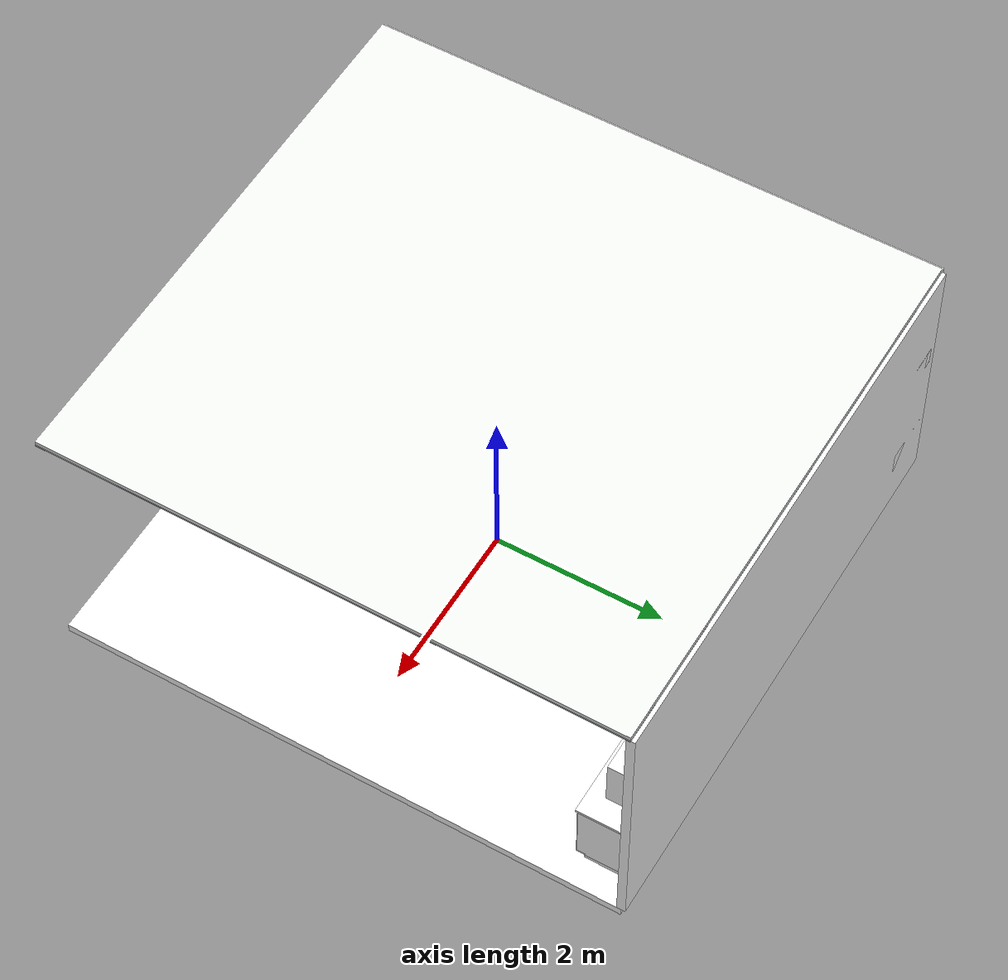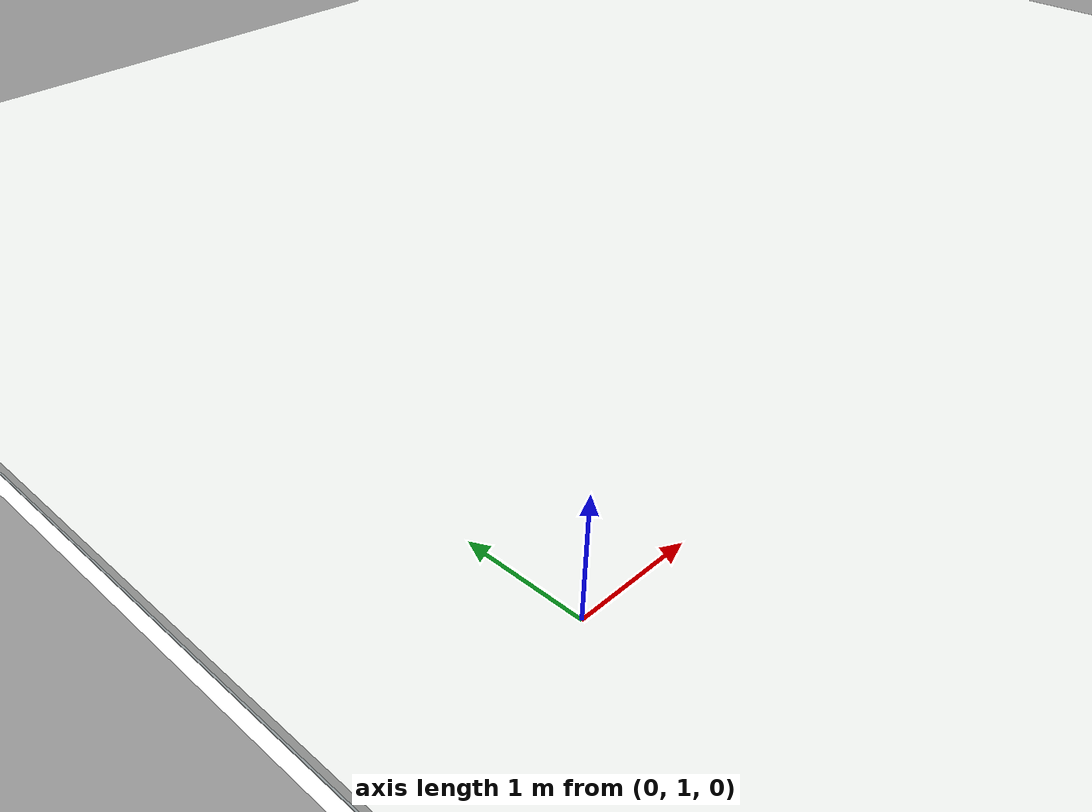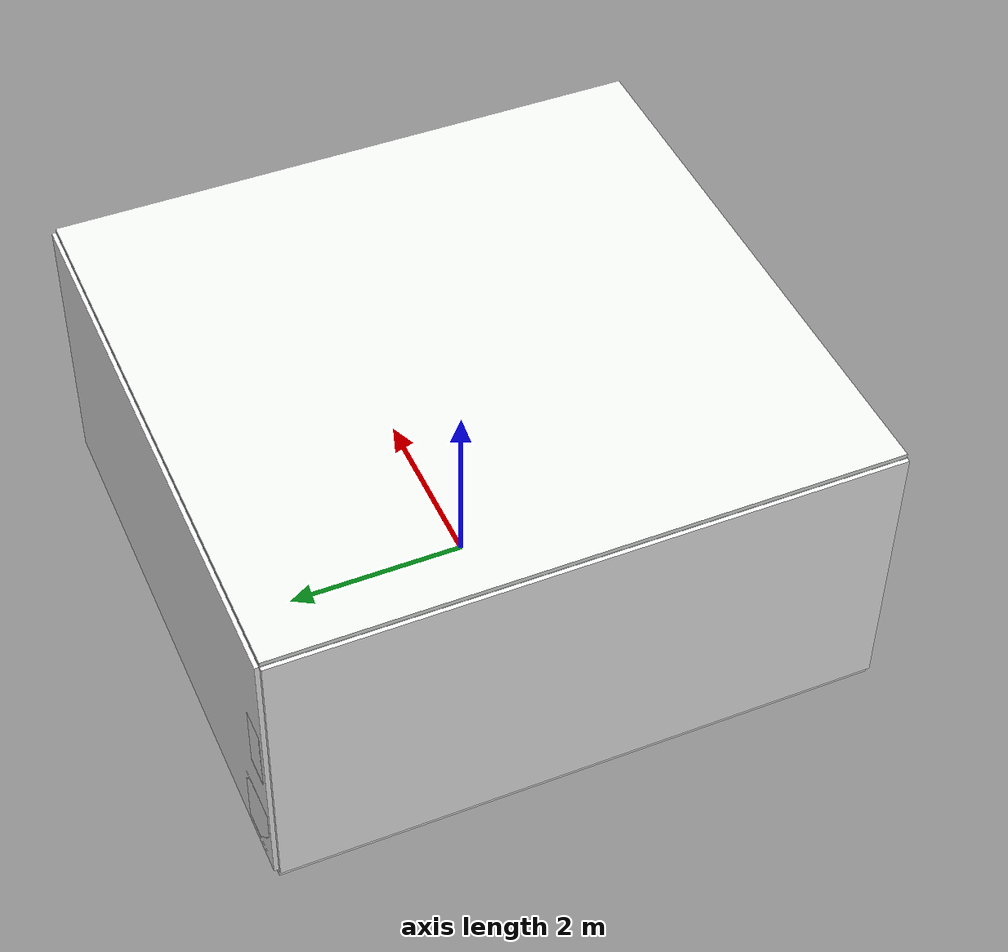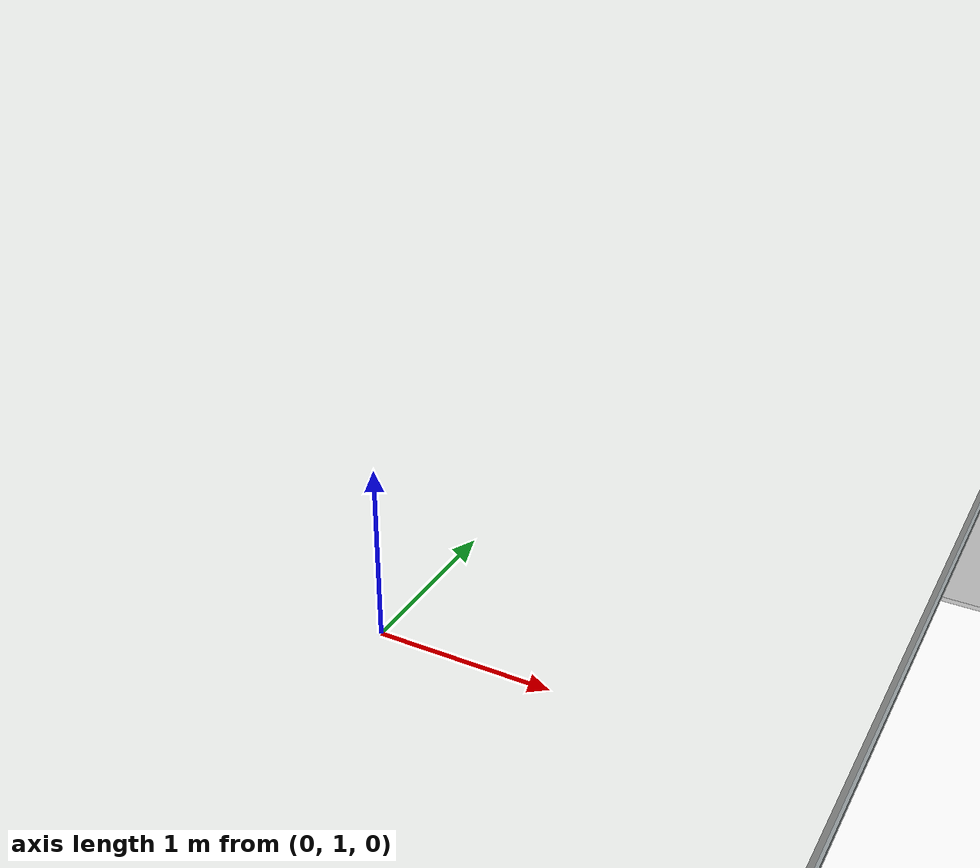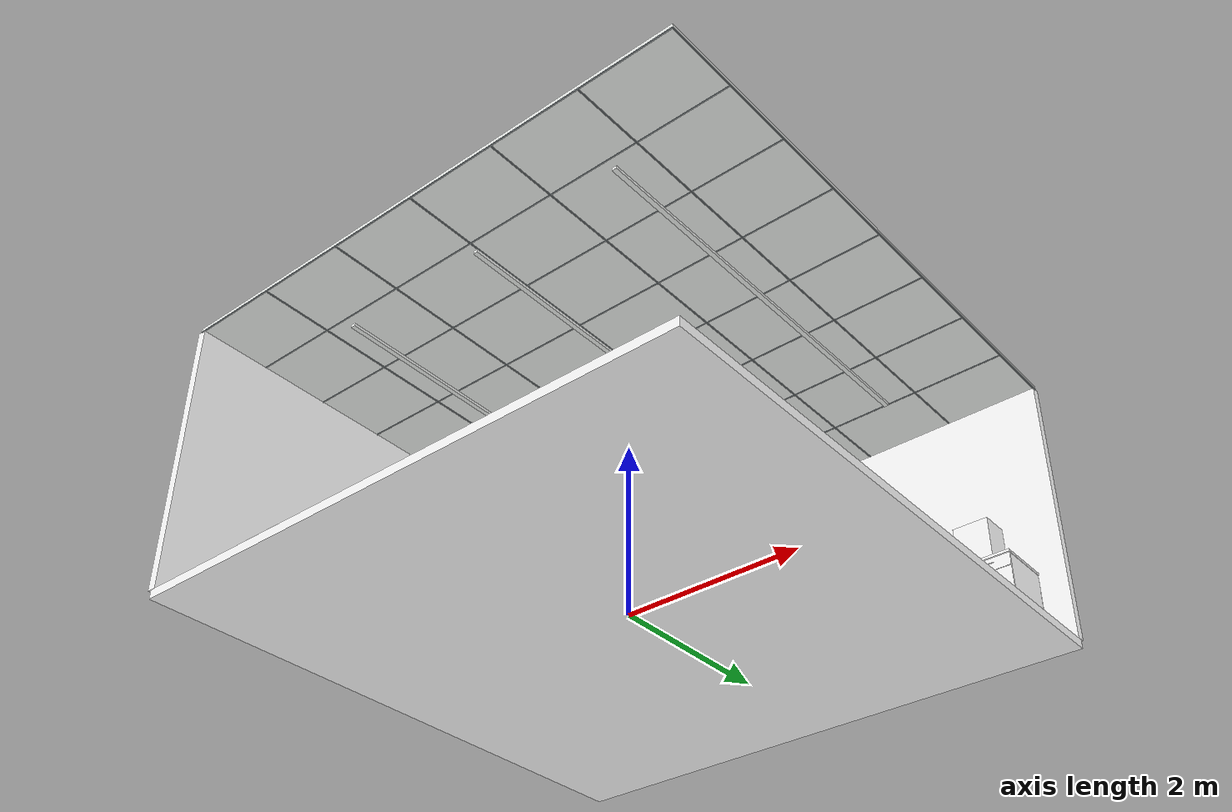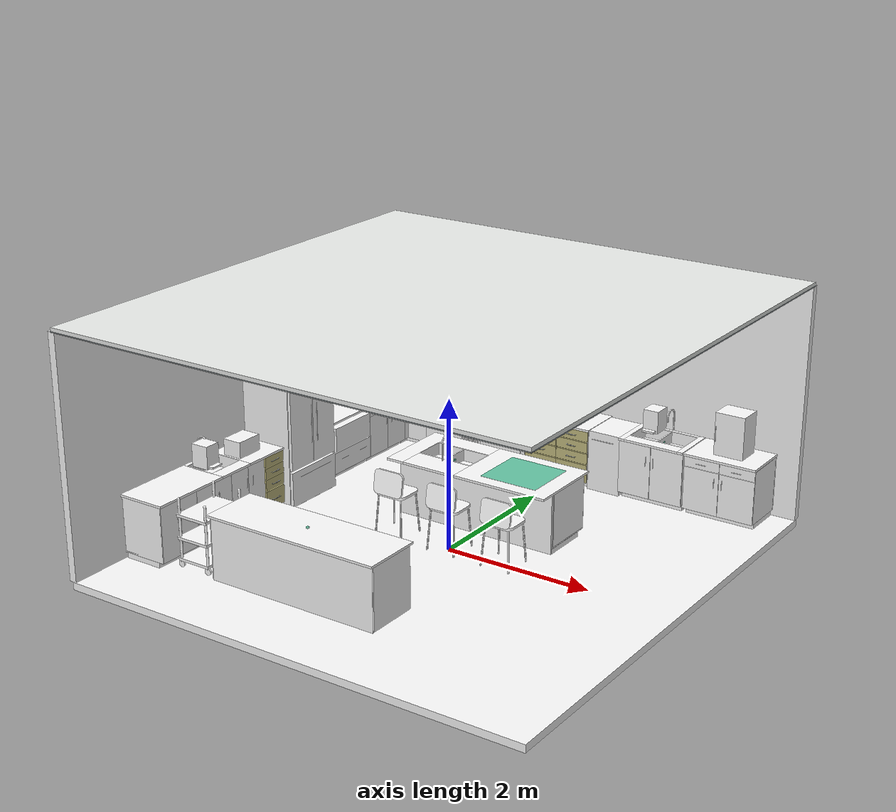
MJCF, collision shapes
<mujoco model="stanford_kitchen_textured">
  <compiler angle="radian" autolimits="true" />
  <option timestep="0.002" integrator="implicitfast" />
  <visual>
    <global offwidth="1920" offheight="1080" />
    <quality shadowsize="4096" offsamples="4" />
    <headlight diffuse="0.10 0.10 0.10" ambient="0.18 0.18 0.18" specular="0.18 0.18 0.18" />
    <rgba haze="0.96 0.97 0.98 1" />
  </visual>
  <default>
    <geom group="1" friction="0.8 0.01 0.001" condim="3" density="500" />
    <joint damping="4" armature="0.02" frictionloss="0.6" />
  </default>
  <asset>
    <material name="cabinet" rgba="0.78 0.75 0.51 1" specular="0.18" shininess="0.12" />
    <material name="cabinet_edge" rgba="0.57 0.53 0.3 1" specular="0.18" shininess="0.12" />
    <material name="interior" rgba="0.45 0.43 0.29 1" specular="0.18" shininess="0.12" />
    <material name="counter" rgba="0.93 0.94 0.93 1" specular="0.18" shininess="0.12" />
    <material name="wall" rgba="0.89 0.91 0.91 1" specular="0.18" shininess="0.12" />
    <material name="steel" rgba="0.57 0.6 0.61 1" specular="0.65" shininess="0.65" />
    <material name="chrome" rgba="0.71 0.74 0.75 1" specular="0.65" shininess="0.65" />
    <material name="dark" rgba="0.045 0.05 0.052 1" specular="0.18" shininess="0.12" />
    <material name="glass" rgba="0.65 0.82 0.84 0.12" specular="0.18" shininess="0.12" />
    <material name="screen" rgba="0.085 0.13 0.16 1" specular="0.18" shininess="0.12" />
    <material name="floor" rgba="0.57 0.59 0.58 1" specular="0.18" shininess="0.12" />
    <material name="border" rgba="0.24 0.26 0.25 1" specular="0.18" shininess="0.12" />
    <material name="red" rgba="0.55 0.045 0.035 1" specular="0.18" shininess="0.12" />
    <material name="blue" rgba="0.08 0.2 0.42 1" specular="0.18" shininess="0.12" />
    <material name="green" rgba="0.12 0.34 0.2 1" specular="0.18" shininess="0.12" />
    <material name="wood" rgba="0.77 0.73 0.55 1" specular="0.18" shininess="0.12" />
    <material name="tracking_led" rgba="0.25 0.2 0.95 1" specular="0.18" shininess="0.12" />
    <texture name="sky" type="skybox" builtin="flat" rgb1="0.88 0.91 0.93" width="64" height="64" />
    <mesh name="hood_taper" vertex="-0.45 -0.39 1.99 0.45 -0.39 1.99 0.45 0.32 1.99 -0.45 0.32 1.99 -0.345 0.02 2.27 0.345 0.02 2.27 0.345 0.32 2.27 -0.345 0.32 2.27" face="0 2 1 0 3 2 4 5 6 4 6 7 0 1 5 0 5 4 1 2 6 1 6 5 2 3 7 2 7 6 3 0 4 3 4 7" />
    <mesh name="stool0_seat_mesh" vertex="0.215 0.11 -0.0175 0.211933 0.133294 -0.0175 0.202942 0.155 -0.0175 0.18864 0.17364 -0.0175 0.17 0.187942 -0.0175 0.148294 0.196933 -0.0175 0.125 0.2 -0.0175 -0.125 0.2 -0.0175 -0.148294 0.196933 -0.0175 -0.17 0.187942 -0.0175 -0.18864 0.17364 -0.0175 -0.202942 0.155 -0.0175 -0.211933 0.133294 -0.0175 -0.215 0.11 -0.0175 -0.215 -0.11 -0.0175 -0.211933 -0.133294 -0.0175 -0.202942 -0.155 -0.0175 -0.18864 -0.17364 -0.0175 -0.17 -0.187942 -0.0175 -0.148294 -0.196933 -0.0175 -0.125 -0.2 -0.0175 0.125 -0.2 -0.0175 0.148294 -0.196933 -0.0175 0.17 -0.187942 -0.0175 0.18864 -0.17364 -0.0175 0.202942 -0.155 -0.0175 0.211933 -0.133294 -0.0175 0.215 -0.11 -0.0175 0.215 0.11 0.0175 0.211933 0.133294 0.0175 0.202942 0.155 0.0175 0.18864 0.17364 0.0175 0.17 0.187942 0.0175 0.148294 0.196933 0.0175 0.125 0.2 0.0175 -0.125 0.2 0.0175 -0.148294 0.196933 0.0175 -0.17 0.187942 0.0175 -0.18864 0.17364 0.0175 -0.202942 0.155 0.0175 -0.211933 0.133294 0.0175 -0.215 0.11 0.0175 -0.215 -0.11 0.0175 -0.211933 -0.133294 0.0175 -0.202942 -0.155 0.0175 -0.18864 -0.17364 0.0175 -0.17 -0.187942 0.0175 -0.148294 -0.196933 0.0175 -0.125 -0.2 0.0175 0.125 -0.2 0.0175 0.148294 -0.196933 0.0175 0.17 -0.187942 0.0175 0.18864 -0.17364 0.0175 0.202942 -0.155 0.0175 0.211933 -0.133294 0.0175 0.215 -0.11 0.0175" face="0 1 29 0 29 28 1 2 30 1 30 29 2 3 31 2 31 30 3 4 32 3 32 31 4 5 33 4 33 32 5 6 34 5 34 33 6 7 35 6 35 34 7 8 36 7 36 35 8 9 37 8 37 36 9 10 38 9 38 37 10 11 39 10 39 38 11 12 40 11 40 39 12 13 41 12 41 40 13 14 42 13 42 41 14 15 43 14 43 42 15 16 44 15 44 43 16 17 45 16 45 44 17 18 46 17 46 45 18 19 47 18 47 46 19 20 48 19 48 47 20 21 49 20 49 48 21 22 50 21 50 49 22 23 51 22 51 50 23 24 52 23 52 51 24 25 53 24 53 52 25 26 54 25 54 53 26 27 55 26 55 54 27 0 28 27 28 55 0 2 1 28 29 30 0 3 2 28 30 31 0 4 3 28 31 32 0 5 4 28 32 33 0 6 5 28 33 34 0 7 6 28 34 35 0 8 7 28 35 36 0 9 8 28 36 37 0 10 9 28 37 38 0 11 10 28 38 39 0 12 11 28 39 40 0 13 12 28 40 41 0 14 13 28 41 42 0 15 14 28 42 43 0 16 15 28 43 44 0 17 16 28 44 45 0 18 17 28 45 46 0 19 18 28 46 47 0 20 19 28 47 48 0 21 20 28 48 49 0 22 21 28 49 50 0 23 22 28 50 51 0 24 23 28 51 52 0 25 24 28 52 53 0 26 25 28 53 54 0 27 26 28 54 55" />
    <mesh name="stool0_back_mesh" vertex="0.215 0.095 -0.016 0.212785 0.111823 -0.016 0.206292 0.1275 -0.016 0.195962 0.140962 -0.016 0.1825 0.151292 -0.016 0.166823 0.157785 -0.016 0.15 0.16 -0.016 -0.15 0.16 -0.016 -0.166823 0.157785 -0.016 -0.1825 0.151292 -0.016 -0.195962 0.140962 -0.016 -0.206292 0.1275 -0.016 -0.212785 0.111823 -0.016 -0.215 0.095 -0.016 -0.215 -0.095 -0.016 -0.212785 -0.111823 -0.016 -0.206292 -0.1275 -0.016 -0.195962 -0.140962 -0.016 -0.1825 -0.151292 -0.016 -0.166823 -0.157785 -0.016 -0.15 -0.16 -0.016 0.15 -0.16 -0.016 0.166823 -0.157785 -0.016 0.1825 -0.151292 -0.016 0.195962 -0.140962 -0.016 0.206292 -0.1275 -0.016 0.212785 -0.111823 -0.016 0.215 -0.095 -0.016 0.215 0.095 0.016 0.212785 0.111823 0.016 0.206292 0.1275 0.016 0.195962 0.140962 0.016 0.1825 0.151292 0.016 0.166823 0.157785 0.016 0.15 0.16 0.016 -0.15 0.16 0.016 -0.166823 0.157785 0.016 -0.1825 0.151292 0.016 -0.195962 0.140962 0.016 -0.206292 0.1275 0.016 -0.212785 0.111823 0.016 -0.215 0.095 0.016 -0.215 -0.095 0.016 -0.212785 -0.111823 0.016 -0.206292 -0.1275 0.016 -0.195962 -0.140962 0.016 -0.1825 -0.151292 0.016 -0.166823 -0.157785 0.016 -0.15 -0.16 0.016 0.15 -0.16 0.016 0.166823 -0.157785 0.016 0.1825 -0.151292 0.016 0.195962 -0.140962 0.016 0.206292 -0.1275 0.016 0.212785 -0.111823 0.016 0.215 -0.095 0.016" face="0 1 29 0 29 28 1 2 30 1 30 29 2 3 31 2 31 30 3 4 32 3 32 31 4 5 33 4 33 32 5 6 34 5 34 33 6 7 35 6 35 34 7 8 36 7 36 35 8 9 37 8 37 36 9 10 38 9 38 37 10 11 39 10 39 38 11 12 40 11 40 39 12 13 41 12 41 40 13 14 42 13 42 41 14 15 43 14 43 42 15 16 44 15 44 43 16 17 45 16 45 44 17 18 46 17 46 45 18 19 47 18 47 46 19 20 48 19 48 47 20 21 49 20 49 48 21 22 50 21 50 49 22 23 51 22 51 50 23 24 52 23 52 51 24 25 53 24 53 52 25 26 54 25 54 53 26 27 55 26 55 54 27 0 28 27 28 55 0 2 1 28 29 30 0 3 2 28 30 31 0 4 3 28 31 32 0 5 4 28 32 33 0 6 5 28 33 34 0 7 6 28 34 35 0 8 7 28 35 36 0 9 8 28 36 37 0 10 9 28 37 38 0 11 10 28 38 39 0 12 11 28 39 40 0 13 12 28 40 41 0 14 13 28 41 42 0 15 14 28 42 43 0 16 15 28 43 44 0 17 16 28 44 45 0 18 17 28 45 46 0 19 18 28 46 47 0 20 19 28 47 48 0 21 20 28 48 49 0 22 21 28 49 50 0 23 22 28 50 51 0 24 23 28 51 52 0 25 24 28 52 53 0 26 25 28 53 54 0 27 26 28 54 55" />
    <mesh name="stool1_seat_mesh" vertex="0.215 0.11 -0.0175 0.211933 0.133294 -0.0175 0.202942 0.155 -0.0175 0.18864 0.17364 -0.0175 0.17 0.187942 -0.0175 0.148294 0.196933 -0.0175 0.125 0.2 -0.0175 -0.125 0.2 -0.0175 -0.148294 0.196933 -0.0175 -0.17 0.187942 -0.0175 -0.18864 0.17364 -0.0175 -0.202942 0.155 -0.0175 -0.211933 0.133294 -0.0175 -0.215 0.11 -0.0175 -0.215 -0.11 -0.0175 -0.211933 -0.133294 -0.0175 -0.202942 -0.155 -0.0175 -0.18864 -0.17364 -0.0175 -0.17 -0.187942 -0.0175 -0.148294 -0.196933 -0.0175 -0.125 -0.2 -0.0175 0.125 -0.2 -0.0175 0.148294 -0.196933 -0.0175 0.17 -0.187942 -0.0175 0.18864 -0.17364 -0.0175 0.202942 -0.155 -0.0175 0.211933 -0.133294 -0.0175 0.215 -0.11 -0.0175 0.215 0.11 0.0175 0.211933 0.133294 0.0175 0.202942 0.155 0.0175 0.18864 0.17364 0.0175 0.17 0.187942 0.0175 0.148294 0.196933 0.0175 0.125 0.2 0.0175 -0.125 0.2 0.0175 -0.148294 0.196933 0.0175 -0.17 0.187942 0.0175 -0.18864 0.17364 0.0175 -0.202942 0.155 0.0175 -0.211933 0.133294 0.0175 -0.215 0.11 0.0175 -0.215 -0.11 0.0175 -0.211933 -0.133294 0.0175 -0.202942 -0.155 0.0175 -0.18864 -0.17364 0.0175 -0.17 -0.187942 0.0175 -0.148294 -0.196933 0.0175 -0.125 -0.2 0.0175 0.125 -0.2 0.0175 0.148294 -0.196933 0.0175 0.17 -0.187942 0.0175 0.18864 -0.17364 0.0175 0.202942 -0.155 0.0175 0.211933 -0.133294 0.0175 0.215 -0.11 0.0175" face="0 1 29 0 29 28 1 2 30 1 30 29 2 3 31 2 31 30 3 4 32 3 32 31 4 5 33 4 33 32 5 6 34 5 34 33 6 7 35 6 35 34 7 8 36 7 36 35 8 9 37 8 37 36 9 10 38 9 38 37 10 11 39 10 39 38 11 12 40 11 40 39 12 13 41 12 41 40 13 14 42 13 42 41 14 15 43 14 43 42 15 16 44 15 44 43 16 17 45 16 45 44 17 18 46 17 46 45 18 19 47 18 47 46 19 20 48 19 48 47 20 21 49 20 49 48 21 22 50 21 50 49 22 23 51 22 51 50 23 24 52 23 52 51 24 25 53 24 53 52 25 26 54 25 54 53 26 27 55 26 55 54 27 0 28 27 28 55 0 2 1 28 29 30 0 3 2 28 30 31 0 4 3 28 31 32 0 5 4 28 32 33 0 6 5 28 33 34 0 7 6 28 34 35 0 8 7 28 35 36 0 9 8 28 36 37 0 10 9 28 37 38 0 11 10 28 38 39 0 12 11 28 39 40 0 13 12 28 40 41 0 14 13 28 41 42 0 15 14 28 42 43 0 16 15 28 43 44 0 17 16 28 44 45 0 18 17 28 45 46 0 19 18 28 46 47 0 20 19 28 47 48 0 21 20 28 48 49 0 22 21 28 49 50 0 23 22 28 50 51 0 24 23 28 51 52 0 25 24 28 52 53 0 26 25 28 53 54 0 27 26 28 54 55" />
    <mesh name="stool1_back_mesh" vertex="0.215 0.095 -0.016 0.212785 0.111823 -0.016 0.206292 0.1275 -0.016 0.195962 0.140962 -0.016 0.1825 0.151292 -0.016 0.166823 0.157785 -0.016 0.15 0.16 -0.016 -0.15 0.16 -0.016 -0.166823 0.157785 -0.016 -0.1825 0.151292 -0.016 -0.195962 0.140962 -0.016 -0.206292 0.1275 -0.016 -0.212785 0.111823 -0.016 -0.215 0.095 -0.016 -0.215 -0.095 -0.016 -0.212785 -0.111823 -0.016 -0.206292 -0.1275 -0.016 -0.195962 -0.140962 -0.016 -0.1825 -0.151292 -0.016 -0.166823 -0.157785 -0.016 -0.15 -0.16 -0.016 0.15 -0.16 -0.016 0.166823 -0.157785 -0.016 0.1825 -0.151292 -0.016 0.195962 -0.140962 -0.016 0.206292 -0.1275 -0.016 0.212785 -0.111823 -0.016 0.215 -0.095 -0.016 0.215 0.095 0.016 0.212785 0.111823 0.016 0.206292 0.1275 0.016 0.195962 0.140962 0.016 0.1825 0.151292 0.016 0.166823 0.157785 0.016 0.15 0.16 0.016 -0.15 0.16 0.016 -0.166823 0.157785 0.016 -0.1825 0.151292 0.016 -0.195962 0.140962 0.016 -0.206292 0.1275 0.016 -0.212785 0.111823 0.016 -0.215 0.095 0.016 -0.215 -0.095 0.016 -0.212785 -0.111823 0.016 -0.206292 -0.1275 0.016 -0.195962 -0.140962 0.016 -0.1825 -0.151292 0.016 -0.166823 -0.157785 0.016 -0.15 -0.16 0.016 0.15 -0.16 0.016 0.166823 -0.157785 0.016 0.1825 -0.151292 0.016 0.195962 -0.140962 0.016 0.206292 -0.1275 0.016 0.212785 -0.111823 0.016 0.215 -0.095 0.016" face="0 1 29 0 29 28 1 2 30 1 30 29 2 3 31 2 31 30 3 4 32 3 32 31 4 5 33 4 33 32 5 6 34 5 34 33 6 7 35 6 35 34 7 8 36 7 36 35 8 9 37 8 37 36 9 10 38 9 38 37 10 11 39 10 39 38 11 12 40 11 40 39 12 13 41 12 41 40 13 14 42 13 42 41 14 15 43 14 43 42 15 16 44 15 44 43 16 17 45 16 45 44 17 18 46 17 46 45 18 19 47 18 47 46 19 20 48 19 48 47 20 21 49 20 49 48 21 22 50 21 50 49 22 23 51 22 51 50 23 24 52 23 52 51 24 25 53 24 53 52 25 26 54 25 54 53 26 27 55 26 55 54 27 0 28 27 28 55 0 2 1 28 29 30 0 3 2 28 30 31 0 4 3 28 31 32 0 5 4 28 32 33 0 6 5 28 33 34 0 7 6 28 34 35 0 8 7 28 35 36 0 9 8 28 36 37 0 10 9 28 37 38 0 11 10 28 38 39 0 12 11 28 39 40 0 13 12 28 40 41 0 14 13 28 41 42 0 15 14 28 42 43 0 16 15 28 43 44 0 17 16 28 44 45 0 18 17 28 45 46 0 19 18 28 46 47 0 20 19 28 47 48 0 21 20 28 48 49 0 22 21 28 49 50 0 23 22 28 50 51 0 24 23 28 51 52 0 25 24 28 52 53 0 26 25 28 53 54 0 27 26 28 54 55" />
    <mesh name="stool2_seat_mesh" vertex="0.215 0.11 -0.0175 0.211933 0.133294 -0.0175 0.202942 0.155 -0.0175 0.18864 0.17364 -0.0175 0.17 0.187942 -0.0175 0.148294 0.196933 -0.0175 0.125 0.2 -0.0175 -0.125 0.2 -0.0175 -0.148294 0.196933 -0.0175 -0.17 0.187942 -0.0175 -0.18864 0.17364 -0.0175 -0.202942 0.155 -0.0175 -0.211933 0.133294 -0.0175 -0.215 0.11 -0.0175 -0.215 -0.11 -0.0175 -0.211933 -0.133294 -0.0175 -0.202942 -0.155 -0.0175 -0.18864 -0.17364 -0.0175 -0.17 -0.187942 -0.0175 -0.148294 -0.196933 -0.0175 -0.125 -0.2 -0.0175 0.125 -0.2 -0.0175 0.148294 -0.196933 -0.0175 0.17 -0.187942 -0.0175 0.18864 -0.17364 -0.0175 0.202942 -0.155 -0.0175 0.211933 -0.133294 -0.0175 0.215 -0.11 -0.0175 0.215 0.11 0.0175 0.211933 0.133294 0.0175 0.202942 0.155 0.0175 0.18864 0.17364 0.0175 0.17 0.187942 0.0175 0.148294 0.196933 0.0175 0.125 0.2 0.0175 -0.125 0.2 0.0175 -0.148294 0.196933 0.0175 -0.17 0.187942 0.0175 -0.18864 0.17364 0.0175 -0.202942 0.155 0.0175 -0.211933 0.133294 0.0175 -0.215 0.11 0.0175 -0.215 -0.11 0.0175 -0.211933 -0.133294 0.0175 -0.202942 -0.155 0.0175 -0.18864 -0.17364 0.0175 -0.17 -0.187942 0.0175 -0.148294 -0.196933 0.0175 -0.125 -0.2 0.0175 0.125 -0.2 0.0175 0.148294 -0.196933 0.0175 0.17 -0.187942 0.0175 0.18864 -0.17364 0.0175 0.202942 -0.155 0.0175 0.211933 -0.133294 0.0175 0.215 -0.11 0.0175" face="0 1 29 0 29 28 1 2 30 1 30 29 2 3 31 2 31 30 3 4 32 3 32 31 4 5 33 4 33 32 5 6 34 5 34 33 6 7 35 6 35 34 7 8 36 7 36 35 8 9 37 8 37 36 9 10 38 9 38 37 10 11 39 10 39 38 11 12 40 11 40 39 12 13 41 12 41 40 13 14 42 13 42 41 14 15 43 14 43 42 15 16 44 15 44 43 16 17 45 16 45 44 17 18 46 17 46 45 18 19 47 18 47 46 19 20 48 19 48 47 20 21 49 20 49 48 21 22 50 21 50 49 22 23 51 22 51 50 23 24 52 23 52 51 24 25 53 24 53 52 25 26 54 25 54 53 26 27 55 26 55 54 27 0 28 27 28 55 0 2 1 28 29 30 0 3 2 28 30 31 0 4 3 28 31 32 0 5 4 28 32 33 0 6 5 28 33 34 0 7 6 28 34 35 0 8 7 28 35 36 0 9 8 28 36 37 0 10 9 28 37 38 0 11 10 28 38 39 0 12 11 28 39 40 0 13 12 28 40 41 0 14 13 28 41 42 0 15 14 28 42 43 0 16 15 28 43 44 0 17 16 28 44 45 0 18 17 28 45 46 0 19 18 28 46 47 0 20 19 28 47 48 0 21 20 28 48 49 0 22 21 28 49 50 0 23 22 28 50 51 0 24 23 28 51 52 0 25 24 28 52 53 0 26 25 28 53 54 0 27 26 28 54 55" />
    <mesh name="stool2_back_mesh" vertex="0.215 0.095 -0.016 0.212785 0.111823 -0.016 0.206292 0.1275 -0.016 0.195962 0.140962 -0.016 0.1825 0.151292 -0.016 0.166823 0.157785 -0.016 0.15 0.16 -0.016 -0.15 0.16 -0.016 -0.166823 0.157785 -0.016 -0.1825 0.151292 -0.016 -0.195962 0.140962 -0.016 -0.206292 0.1275 -0.016 -0.212785 0.111823 -0.016 -0.215 0.095 -0.016 -0.215 -0.095 -0.016 -0.212785 -0.111823 -0.016 -0.206292 -0.1275 -0.016 -0.195962 -0.140962 -0.016 -0.1825 -0.151292 -0.016 -0.166823 -0.157785 -0.016 -0.15 -0.16 -0.016 0.15 -0.16 -0.016 0.166823 -0.157785 -0.016 0.1825 -0.151292 -0.016 0.195962 -0.140962 -0.016 0.206292 -0.1275 -0.016 0.212785 -0.111823 -0.016 0.215 -0.095 -0.016 0.215 0.095 0.016 0.212785 0.111823 0.016 0.206292 0.1275 0.016 0.195962 0.140962 0.016 0.1825 0.151292 0.016 0.166823 0.157785 0.016 0.15 0.16 0.016 -0.15 0.16 0.016 -0.166823 0.157785 0.016 -0.1825 0.151292 0.016 -0.195962 0.140962 0.016 -0.206292 0.1275 0.016 -0.212785 0.111823 0.016 -0.215 0.095 0.016 -0.215 -0.095 0.016 -0.212785 -0.111823 0.016 -0.206292 -0.1275 0.016 -0.195962 -0.140962 0.016 -0.1825 -0.151292 0.016 -0.166823 -0.157785 0.016 -0.15 -0.16 0.016 0.15 -0.16 0.016 0.166823 -0.157785 0.016 0.1825 -0.151292 0.016 0.195962 -0.140962 0.016 0.206292 -0.1275 0.016 0.212785 -0.111823 0.016 0.215 -0.095 0.016" face="0 1 29 0 29 28 1 2 30 1 30 29 2 3 31 2 31 30 3 4 32 3 32 31 4 5 33 4 33 32 5 6 34 5 34 33 6 7 35 6 35 34 7 8 36 7 36 35 8 9 37 8 37 36 9 10 38 9 38 37 10 11 39 10 39 38 11 12 40 11 40 39 12 13 41 12 41 40 13 14 42 13 42 41 14 15 43 14 43 42 15 16 44 15 44 43 16 17 45 16 45 44 17 18 46 17 46 45 18 19 47 18 47 46 19 20 48 19 48 47 20 21 49 20 49 48 21 22 50 21 50 49 22 23 51 22 51 50 23 24 52 23 52 51 24 25 53 24 53 52 25 26 54 25 54 53 26 27 55 26 55 54 27 0 28 27 28 55 0 2 1 28 29 30 0 3 2 28 30 31 0 4 3 28 31 32 0 5 4 28 32 33 0 6 5 28 33 34 0 7 6 28 34 35 0 8 7 28 35 36 0 9 8 28 36 37 0 10 9 28 37 38 0 11 10 28 38 39 0 12 11 28 39 40 0 13 12 28 40 41 0 14 13 28 41 42 0 15 14 28 42 43 0 16 15 28 43 44 0 17 16 28 44 45 0 18 17 28 45 46 0 19 18 28 46 47 0 20 19 28 47 48 0 21 20 28 48 49 0 22 21 28 49 50 0 23 22 28 50 51 0 24 23 28 51 52 0 25 24 28 52 53 0 26 25 28 53 54 0 27 26 28 54 55" />
    <mesh name="pendant_mesh0" vertex="0.135 0 0 0.133338 0.0211187 0 0.128393 0.0417173 0 0.120286 0.0612887 0 0.109217 0.079351 0 0.0954594 0.0954594 0 0.079351 0.109217 0 0.0612887 0.120286 0 0.0417173 0.128393 0 0.0211187 0.133338 0 8.26637e-18 0.135 0 -0.0211187 0.133338 0 -0.0417173 0.128393 0 -0.0612887 0.120286 0 -0.079351 0.109217 0 -0.0954594 0.0954594 0 -0.109217 0.079351 0 -0.120286 0.0612887 0 -0.128393 0.0417173 0 -0.133338 0.0211187 0 -0.135 1.65327e-17 0 -0.133338 -0.0211187 0 -0.128393 -0.0417173 0 -0.120286 -0.0612887 0 -0.109217 -0.079351 0 -0.0954594 -0.0954594 0 -0.079351 -0.109217 0 -0.0612887 -0.120286 0 -0.0417173 -0.128393 0 -0.0211187 -0.133338 0 -2.47991e-17 -0.135 0 0.0211187 -0.133338 0 0.0417173 -0.128393 0 0.0612887 -0.120286 0 0.079351 -0.109217 0 0.0954594 -0.0954594 0 0.109217 -0.079351 0 0.120286 -0.0612887 0 0.128393 -0.0417173 0 0.133338 -0.0211187 0 0.043 0 0.21 0.0424706 0.00672668 0.21 0.0408954 0.0132877 0.21 0.0383133 0.0195216 0.21 0.0347877 0.0252748 0.21 0.0304056 0.0304056 0.21 0.0252748 0.0347877 0.21 0.0195216 0.0383133 0.21 0.0132877 0.0408954 0.21 0.00672668 0.0424706 0.21 2.63299e-18 0.043 0.21 -0.00672668 0.0424706 0.21 -0.0132877 0.0408954 0.21 -0.0195216 0.0383133 0.21 -0.0252748 0.0347877 0.21 -0.0304056 0.0304056 0.21 -0.0347877 0.0252748 0.21 -0.0383133 0.0195216 0.21 -0.0408954 0.0132877 0.21 -0.0424706 0.00672668 0.21 -0.043 5.26598e-18 0.21 -0.0424706 -0.00672668 0.21 -0.0408954 -0.0132877 0.21 -0.0383133 -0.0195216 0.21 -0.0347877 -0.0252748 0.21 -0.0304056 -0.0304056 0.21 -0.0252748 -0.0347877 0.21 -0.0195216 -0.0383133 0.21 -0.0132877 -0.0408954 0.21 -0.00672668 -0.0424706 0.21 -7.89897e-18 -0.043 0.21 0.00672668 -0.0424706 0.21 0.0132877 -0.0408954 0.21 0.0195216 -0.0383133 0.21 0.0252748 -0.0347877 0.21 0.0304056 -0.0304056 0.21 0.0347877 -0.0252748 0.21 0.0383133 -0.0195216 0.21 0.0408954 -0.0132877 0.21 0.0424706 -0.00672668 0.21" face="0 1 41 0 41 40 1 2 42 1 42 41 2 3 43 2 43 42 3 4 44 3 44 43 4 5 45 4 45 44 5 6 46 5 46 45 6 7 47 6 47 46 7 8 48 7 48 47 8 9 49 8 49 48 9 10 50 9 50 49 10 11 51 10 51 50 11 12 52 11 52 51 12 13 53 12 53 52 13 14 54 13 54 53 14 15 55 14 55 54 15 16 56 15 56 55 16 17 57 16 57 56 17 18 58 17 58 57 18 19 59 18 59 58 19 20 60 19 60 59 20 21 61 20 61 60 21 22 62 21 62 61 22 23 63 22 63 62 23 24 64 23 64 63 24 25 65 24 65 64 25 26 66 25 66 65 26 27 67 26 67 66 27 28 68 27 68 67 28 29 69 28 69 68 29 30 70 29 70 69 30 31 71 30 71 70 31 32 72 31 72 71 32 33 73 32 73 72 33 34 74 33 74 73 34 35 75 34 75 74 35 36 76 35 76 75 36 37 77 36 77 76 37 38 78 37 78 77 38 39 79 38 79 78 39 0 40 39 40 79 0 2 1 40 41 42 0 3 2 40 42 43 0 4 3 40 43 44 0 5 4 40 44 45 0 6 5 40 45 46 0 7 6 40 46 47 0 8 7 40 47 48 0 9 8 40 48 49 0 10 9 40 49 50 0 11 10 40 50 51 0 12 11 40 51 52 0 13 12 40 52 53 0 14 13 40 53 54 0 15 14 40 54 55 0 16 15 40 55 56 0 17 16 40 56 57 0 18 17 40 57 58 0 19 18 40 58 59 0 20 19 40 59 60 0 21 20 40 60 61 0 22 21 40 61 62 0 23 22 40 62 63 0 24 23 40 63 64 0 25 24 40 64 65 0 26 25 40 65 66 0 27 26 40 66 67 0 28 27 40 67 68 0 29 28 40 68 69 0 30 29 40 69 70 0 31 30 40 70 71 0 32 31 40 71 72 0 33 32 40 72 73 0 34 33 40 73 74 0 35 34 40 74 75 0 36 35 40 75 76 0 37 36 40 76 77 0 38 37 40 77 78 0 39 38 40 78 79" />
    <mesh name="pendant_mesh1" vertex="0.135 0 0 0.133338 0.0211187 0 0.128393 0.0417173 0 0.120286 0.0612887 0 0.109217 0.079351 0 0.0954594 0.0954594 0 0.079351 0.109217 0 0.0612887 0.120286 0 0.0417173 0.128393 0 0.0211187 0.133338 0 8.26637e-18 0.135 0 -0.0211187 0.133338 0 -0.0417173 0.128393 0 -0.0612887 0.120286 0 -0.079351 0.109217 0 -0.0954594 0.0954594 0 -0.109217 0.079351 0 -0.120286 0.0612887 0 -0.128393 0.0417173 0 -0.133338 0.0211187 0 -0.135 1.65327e-17 0 -0.133338 -0.0211187 0 -0.128393 -0.0417173 0 -0.120286 -0.0612887 0 -0.109217 -0.079351 0 -0.0954594 -0.0954594 0 -0.079351 -0.109217 0 -0.0612887 -0.120286 0 -0.0417173 -0.128393 0 -0.0211187 -0.133338 0 -2.47991e-17 -0.135 0 0.0211187 -0.133338 0 0.0417173 -0.128393 0 0.0612887 -0.120286 0 0.079351 -0.109217 0 0.0954594 -0.0954594 0 0.109217 -0.079351 0 0.120286 -0.0612887 0 0.128393 -0.0417173 0 0.133338 -0.0211187 0 0.043 0 0.21 0.0424706 0.00672668 0.21 0.0408954 0.0132877 0.21 0.0383133 0.0195216 0.21 0.0347877 0.0252748 0.21 0.0304056 0.0304056 0.21 0.0252748 0.0347877 0.21 0.0195216 0.0383133 0.21 0.0132877 0.0408954 0.21 0.00672668 0.0424706 0.21 2.63299e-18 0.043 0.21 -0.00672668 0.0424706 0.21 -0.0132877 0.0408954 0.21 -0.0195216 0.0383133 0.21 -0.0252748 0.0347877 0.21 -0.0304056 0.0304056 0.21 -0.0347877 0.0252748 0.21 -0.0383133 0.0195216 0.21 -0.0408954 0.0132877 0.21 -0.0424706 0.00672668 0.21 -0.043 5.26598e-18 0.21 -0.0424706 -0.00672668 0.21 -0.0408954 -0.0132877 0.21 -0.0383133 -0.0195216 0.21 -0.0347877 -0.0252748 0.21 -0.0304056 -0.0304056 0.21 -0.0252748 -0.0347877 0.21 -0.0195216 -0.0383133 0.21 -0.0132877 -0.0408954 0.21 -0.00672668 -0.0424706 0.21 -7.89897e-18 -0.043 0.21 0.00672668 -0.0424706 0.21 0.0132877 -0.0408954 0.21 0.0195216 -0.0383133 0.21 0.0252748 -0.0347877 0.21 0.0304056 -0.0304056 0.21 0.0347877 -0.0252748 0.21 0.0383133 -0.0195216 0.21 0.0408954 -0.0132877 0.21 0.0424706 -0.00672668 0.21" face="0 1 41 0 41 40 1 2 42 1 42 41 2 3 43 2 43 42 3 4 44 3 44 43 4 5 45 4 45 44 5 6 46 5 46 45 6 7 47 6 47 46 7 8 48 7 48 47 8 9 49 8 49 48 9 10 50 9 50 49 10 11 51 10 51 50 11 12 52 11 52 51 12 13 53 12 53 52 13 14 54 13 54 53 14 15 55 14 55 54 15 16 56 15 56 55 16 17 57 16 57 56 17 18 58 17 58 57 18 19 59 18 59 58 19 20 60 19 60 59 20 21 61 20 61 60 21 22 62 21 62 61 22 23 63 22 63 62 23 24 64 23 64 63 24 25 65 24 65 64 25 26 66 25 66 65 26 27 67 26 67 66 27 28 68 27 68 67 28 29 69 28 69 68 29 30 70 29 70 69 30 31 71 30 71 70 31 32 72 31 72 71 32 33 73 32 73 72 33 34 74 33 74 73 34 35 75 34 75 74 35 36 76 35 76 75 36 37 77 36 77 76 37 38 78 37 78 77 38 39 79 38 79 78 39 0 40 39 40 79 0 2 1 40 41 42 0 3 2 40 42 43 0 4 3 40 43 44 0 5 4 40 44 45 0 6 5 40 45 46 0 7 6 40 46 47 0 8 7 40 47 48 0 9 8 40 48 49 0 10 9 40 49 50 0 11 10 40 50 51 0 12 11 40 51 52 0 13 12 40 52 53 0 14 13 40 53 54 0 15 14 40 54 55 0 16 15 40 55 56 0 17 16 40 56 57 0 18 17 40 57 58 0 19 18 40 58 59 0 20 19 40 59 60 0 21 20 40 60 61 0 22 21 40 61 62 0 23 22 40 62 63 0 24 23 40 63 64 0 25 24 40 64 65 0 26 25 40 65 66 0 27 26 40 66 67 0 28 27 40 67 68 0 29 28 40 68 69 0 30 29 40 69 70 0 31 30 40 70 71 0 32 31 40 71 72 0 33 32 40 72 73 0 34 33 40 73 74 0 35 34 40 74 75 0 36 35 40 75 76 0 37 36 40 76 77 0 38 37 40 77 78 0 39 38 40 78 79" />
    <mesh name="pendant_mesh2" vertex="0.135 0 0 0.133338 0.0211187 0 0.128393 0.0417173 0 0.120286 0.0612887 0 0.109217 0.079351 0 0.0954594 0.0954594 0 0.079351 0.109217 0 0.0612887 0.120286 0 0.0417173 0.128393 0 0.0211187 0.133338 0 8.26637e-18 0.135 0 -0.0211187 0.133338 0 -0.0417173 0.128393 0 -0.0612887 0.120286 0 -0.079351 0.109217 0 -0.0954594 0.0954594 0 -0.109217 0.079351 0 -0.120286 0.0612887 0 -0.128393 0.0417173 0 -0.133338 0.0211187 0 -0.135 1.65327e-17 0 -0.133338 -0.0211187 0 -0.128393 -0.0417173 0 -0.120286 -0.0612887 0 -0.109217 -0.079351 0 -0.0954594 -0.0954594 0 -0.079351 -0.109217 0 -0.0612887 -0.120286 0 -0.0417173 -0.128393 0 -0.0211187 -0.133338 0 -2.47991e-17 -0.135 0 0.0211187 -0.133338 0 0.0417173 -0.128393 0 0.0612887 -0.120286 0 0.079351 -0.109217 0 0.0954594 -0.0954594 0 0.109217 -0.079351 0 0.120286 -0.0612887 0 0.128393 -0.0417173 0 0.133338 -0.0211187 0 0.043 0 0.21 0.0424706 0.00672668 0.21 0.0408954 0.0132877 0.21 0.0383133 0.0195216 0.21 0.0347877 0.0252748 0.21 0.0304056 0.0304056 0.21 0.0252748 0.0347877 0.21 0.0195216 0.0383133 0.21 0.0132877 0.0408954 0.21 0.00672668 0.0424706 0.21 2.63299e-18 0.043 0.21 -0.00672668 0.0424706 0.21 -0.0132877 0.0408954 0.21 -0.0195216 0.0383133 0.21 -0.0252748 0.0347877 0.21 -0.0304056 0.0304056 0.21 -0.0347877 0.0252748 0.21 -0.0383133 0.0195216 0.21 -0.0408954 0.0132877 0.21 -0.0424706 0.00672668 0.21 -0.043 5.26598e-18 0.21 -0.0424706 -0.00672668 0.21 -0.0408954 -0.0132877 0.21 -0.0383133 -0.0195216 0.21 -0.0347877 -0.0252748 0.21 -0.0304056 -0.0304056 0.21 -0.0252748 -0.0347877 0.21 -0.0195216 -0.0383133 0.21 -0.0132877 -0.0408954 0.21 -0.00672668 -0.0424706 0.21 -7.89897e-18 -0.043 0.21 0.00672668 -0.0424706 0.21 0.0132877 -0.0408954 0.21 0.0195216 -0.0383133 0.21 0.0252748 -0.0347877 0.21 0.0304056 -0.0304056 0.21 0.0347877 -0.0252748 0.21 0.0383133 -0.0195216 0.21 0.0408954 -0.0132877 0.21 0.0424706 -0.00672668 0.21" face="0 1 41 0 41 40 1 2 42 1 42 41 2 3 43 2 43 42 3 4 44 3 44 43 4 5 45 4 45 44 5 6 46 5 46 45 6 7 47 6 47 46 7 8 48 7 48 47 8 9 49 8 49 48 9 10 50 9 50 49 10 11 51 10 51 50 11 12 52 11 52 51 12 13 53 12 53 52 13 14 54 13 54 53 14 15 55 14 55 54 15 16 56 15 56 55 16 17 57 16 57 56 17 18 58 17 58 57 18 19 59 18 59 58 19 20 60 19 60 59 20 21 61 20 61 60 21 22 62 21 62 61 22 23 63 22 63 62 23 24 64 23 64 63 24 25 65 24 65 64 25 26 66 25 66 65 26 27 67 26 67 66 27 28 68 27 68 67 28 29 69 28 69 68 29 30 70 29 70 69 30 31 71 30 71 70 31 32 72 31 72 71 32 33 73 32 73 72 33 34 74 33 74 73 34 35 75 34 75 74 35 36 76 35 76 75 36 37 77 36 77 76 37 38 78 37 78 77 38 39 79 38 79 78 39 0 40 39 40 79 0 2 1 40 41 42 0 3 2 40 42 43 0 4 3 40 43 44 0 5 4 40 44 45 0 6 5 40 45 46 0 7 6 40 46 47 0 8 7 40 47 48 0 9 8 40 48 49 0 10 9 40 49 50 0 11 10 40 50 51 0 12 11 40 51 52 0 13 12 40 52 53 0 14 13 40 53 54 0 15 14 40 54 55 0 16 15 40 55 56 0 17 16 40 56 57 0 18 17 40 57 58 0 19 18 40 58 59 0 20 19 40 59 60 0 21 20 40 60 61 0 22 21 40 61 62 0 23 22 40 62 63 0 24 23 40 63 64 0 25 24 40 64 65 0 26 25 40 65 66 0 27 26 40 66 67 0 28 27 40 67 68 0 29 28 40 68 69 0 30 29 40 69 70 0 31 30 40 70 71 0 32 31 40 71 72 0 33 32 40 72 73 0 34 33 40 73 74 0 35 34 40 74 75 0 36 35 40 75 76 0 37 36 40 76 77 0 38 37 40 77 78 0 39 38 40 78 79" />
    <texture name="baked_floor" type="2d" file="simulation-assets/floor.png" />
    <material name="baked_floor" texture="baked_floor" rgba="1 1 1 1" emission="0.65" texuniform="false" metallic="0.0" roughness="0.75" specular="0.06" shininess="0.08" />
    <mesh name="baked_floor" file="simulation-assets/floor.obj" />
    <texture name="baked_walls" type="2d" file="simulation-assets/walls.png" />
    <material name="baked_walls" texture="baked_walls" rgba="1 1 1 1" emission="0.65" texuniform="false" metallic="0.0" roughness="0.85" specular="0.06" shininess="0.08" />
    <mesh name="baked_walls" file="simulation-assets/walls.obj" />
    <texture name="baked_metal" type="2d" file="simulation-assets/metal.png" />
    <material name="baked_metal" texture="baked_metal" rgba="0.82 0.84 0.85 1" emission="0.65" texuniform="false" metallic="0.85" roughness="0.32" specular="0.38" shininess="0.3" />
    <mesh name="baked_metal" file="simulation-assets/metal.obj" />
    <texture name="baked_details" type="2d" file="simulation-assets/details.png" />
    <material name="baked_details" texture="baked_details" rgba="1 1 1 1" emission="0.65" texuniform="false" metallic="0.12" roughness="0.45" specular="0.38" shininess="0.3" />
    <mesh name="baked_details" file="simulation-assets/details.obj" />
    <texture name="baked_cabinetry" type="2d" file="simulation-assets/cabinetry.png" />
    <material name="baked_cabinetry" texture="baked_cabinetry" rgba="1 1 1 1" emission="0.65" texuniform="false" metallic="0.0" roughness="0.5" specular="0.06" shininess="0.08" />
    <mesh name="baked_cabinetry" file="simulation-assets/cabinetry.obj" />
    <mesh name="mobile_aloha_visual_000" file="robots/mobile-aloha-assets/mobile_aloha_visual_000.obj" />
    <material name="mobile_aloha_finish_joint" rgba="0.1176471 0.1294118 0.145098 1" metallic="0.25" roughness="0.42" specular="0.45" shininess="0.35" />
    <mesh name="mobile_aloha_visual_001" file="robots/mobile-aloha-assets/mobile_aloha_visual_001.obj" />
    <mesh name="mobile_aloha_visual_002" file="robots/mobile-aloha-assets/mobile_aloha_visual_002.obj" />
    <material name="mobile_aloha_finish_arm" rgba="0.1882353 0.2078431 0.227451 1" metallic="0.45" roughness="0.36" specular="0.45" shininess="0.35" />
    <mesh name="mobile_aloha_visual_003" file="robots/mobile-aloha-assets/mobile_aloha_visual_003.obj" />
    <mesh name="mobile_aloha_visual_004" file="robots/mobile-aloha-assets/mobile_aloha_visual_004.obj" />
    <mesh name="mobile_aloha_visual_005" file="robots/mobile-aloha-assets/mobile_aloha_visual_005.obj" />
    <mesh name="mobile_aloha_visual_006" file="robots/mobile-aloha-assets/mobile_aloha_visual_006.obj" />
    <mesh name="mobile_aloha_visual_007" file="robots/mobile-aloha-assets/mobile_aloha_visual_007.obj" />
    <material name="mobile_aloha_finish_steel" rgba="0.654902 0.7058824 0.7411765 1" metallic="0.75" roughness="0.28" specular="0.45" shininess="0.35" />
    <mesh name="mobile_aloha_visual_008" file="robots/mobile-aloha-assets/mobile_aloha_visual_008.obj" />
    <mesh name="mobile_aloha_visual_009" file="robots/mobile-aloha-assets/mobile_aloha_visual_009.obj" />
    <mesh name="mobile_aloha_visual_010" file="robots/mobile-aloha-assets/mobile_aloha_visual_010.obj" />
    <mesh name="mobile_aloha_visual_011" file="robots/mobile-aloha-assets/mobile_aloha_visual_011.obj" />
    <mesh name="mobile_aloha_visual_012" file="robots/mobile-aloha-assets/mobile_aloha_visual_012.obj" />
    <mesh name="mobile_aloha_visual_013" file="robots/mobile-aloha-assets/mobile_aloha_visual_013.obj" />
    <mesh name="mobile_aloha_visual_014" file="robots/mobile-aloha-assets/mobile_aloha_visual_014.obj" />
    <mesh name="mobile_aloha_visual_015" file="robots/mobile-aloha-assets/mobile_aloha_visual_015.obj" />
    <mesh name="mobile_aloha_visual_016" file="robots/mobile-aloha-assets/mobile_aloha_visual_016.obj" />
    <mesh name="mobile_aloha_visual_017" file="robots/mobile-aloha-assets/mobile_aloha_visual_017.obj" />
    <mesh name="mobile_aloha_visual_018" file="robots/mobile-aloha-assets/mobile_aloha_visual_018.obj" />
    <mesh name="mobile_aloha_visual_019" file="robots/mobile-aloha-assets/mobile_aloha_visual_019.obj" />
    <mesh name="mobile_aloha_visual_020" file="robots/mobile-aloha-assets/mobile_aloha_visual_020.obj" />
    <mesh name="mobile_aloha_visual_021" file="robots/mobile-aloha-assets/mobile_aloha_visual_021.obj" />
    <mesh name="mobile_aloha_visual_022" file="robots/mobile-aloha-assets/mobile_aloha_visual_022.obj" />
    <mesh name="mobile_aloha_visual_023" file="robots/mobile-aloha-assets/mobile_aloha_visual_023.obj" />
    <mesh name="mobile_aloha_visual_024" file="robots/mobile-aloha-assets/mobile_aloha_visual_024.obj" />
    <mesh name="mobile_aloha_visual_025" file="robots/mobile-aloha-assets/mobile_aloha_visual_025.obj" />
    <mesh name="mobile_aloha_visual_026" file="robots/mobile-aloha-assets/mobile_aloha_visual_026.obj" />
    <mesh name="mobile_aloha_visual_027" file="robots/mobile-aloha-assets/mobile_aloha_visual_027.obj" />
    <mesh name="mobile_aloha_visual_028" file="robots/mobile-aloha-assets/mobile_aloha_visual_028.obj" />
    <mesh name="mobile_aloha_visual_029" file="robots/mobile-aloha-assets/mobile_aloha_visual_029.obj" />
    <mesh name="mobile_aloha_visual_030" file="robots/mobile-aloha-assets/mobile_aloha_visual_030.obj" />
    <mesh name="mobile_aloha_visual_031" file="robots/mobile-aloha-assets/mobile_aloha_visual_031.obj" />
    <mesh name="mobile_aloha_visual_032" file="robots/mobile-aloha-assets/mobile_aloha_visual_032.obj" />
    <mesh name="mobile_aloha_visual_033" file="robots/mobile-aloha-assets/mobile_aloha_visual_033.obj" />
    <mesh name="mobile_aloha_visual_034" file="robots/mobile-aloha-assets/mobile_aloha_visual_034.obj" />
    <mesh name="mobile_aloha_visual_035" file="robots/mobile-aloha-assets/mobile_aloha_visual_035.obj" />
    <mesh name="mobile_aloha_visual_036" file="robots/mobile-aloha-assets/mobile_aloha_visual_036.obj" />
    <material name="mobile_aloha_finish_frame" rgba="0.1686275 0.1843137 0.2 1" metallic="0.3" roughness="0.48" specular="0.45" shininess="0.35" />
    <mesh name="mobile_aloha_visual_037" file="robots/mobile-aloha-assets/mobile_aloha_visual_037.obj" />
    <material name="mobile_aloha_finish_panel" rgba="0.8705882 0.8901961 0.9019608 1" metallic="0.12" roughness="0.4" specular="0.45" shininess="0.35" />
    <mesh name="mobile_aloha_visual_038" file="robots/mobile-aloha-assets/mobile_aloha_visual_038.obj" />
    <mesh name="mobile_aloha_visual_039" file="robots/mobile-aloha-assets/mobile_aloha_visual_039.obj" />
    <mesh name="mobile_aloha_visual_040" file="robots/mobile-aloha-assets/mobile_aloha_visual_040.obj" />
    <mesh name="mobile_aloha_visual_041" file="robots/mobile-aloha-assets/mobile_aloha_visual_041.obj" />
    <mesh name="mobile_aloha_visual_042" file="robots/mobile-aloha-assets/mobile_aloha_visual_042.obj" />
    <mesh name="mobile_aloha_visual_043" file="robots/mobile-aloha-assets/mobile_aloha_visual_043.obj" />
    <mesh name="mobile_aloha_visual_044" file="robots/mobile-aloha-assets/mobile_aloha_visual_044.obj" />
    <mesh name="mobile_aloha_visual_045" file="robots/mobile-aloha-assets/mobile_aloha_visual_045.obj" />
    <mesh name="mobile_aloha_visual_046" file="robots/mobile-aloha-assets/mobile_aloha_visual_046.obj" />
    <mesh name="mobile_aloha_visual_047" file="robots/mobile-aloha-assets/mobile_aloha_visual_047.obj" />
    <mesh name="mobile_aloha_visual_048" file="robots/mobile-aloha-assets/mobile_aloha_visual_048.obj" />
    <mesh name="mobile_aloha_visual_049" file="robots/mobile-aloha-assets/mobile_aloha_visual_049.obj" />
    <mesh name="mobile_aloha_visual_050" file="robots/mobile-aloha-assets/mobile_aloha_visual_050.obj" />
    <mesh name="mobile_aloha_visual_051" file="robots/mobile-aloha-assets/mobile_aloha_visual_051.obj" />
    <mesh name="mobile_aloha_visual_052" file="robots/mobile-aloha-assets/mobile_aloha_visual_052.obj" />
    <mesh name="mobile_aloha_visual_053" file="robots/mobile-aloha-assets/mobile_aloha_visual_053.obj" />
    <mesh name="mobile_aloha_visual_054" file="robots/mobile-aloha-assets/mobile_aloha_visual_054.obj" />
    <mesh name="mobile_aloha_visual_055" file="robots/mobile-aloha-assets/mobile_aloha_visual_055.obj" />
    <mesh name="mobile_aloha_visual_056" file="robots/mobile-aloha-assets/mobile_aloha_visual_056.obj" />
    <mesh name="mobile_aloha_visual_057" file="robots/mobile-aloha-assets/mobile_aloha_visual_057.obj" />
    <mesh name="mobile_aloha_visual_058" file="robots/mobile-aloha-assets/mobile_aloha_visual_058.obj" />
    <mesh name="mobile_aloha_visual_059" file="robots/mobile-aloha-assets/mobile_aloha_visual_059.obj" />
    <mesh name="mobile_aloha_visual_060" file="robots/mobile-aloha-assets/mobile_aloha_visual_060.obj" />
    <mesh name="mobile_aloha_visual_061" file="robots/mobile-aloha-assets/mobile_aloha_visual_061.obj" />
    <mesh name="mobile_aloha_visual_062" file="robots/mobile-aloha-assets/mobile_aloha_visual_062.obj" />
    <mesh name="mobile_aloha_visual_063" file="robots/mobile-aloha-assets/mobile_aloha_visual_063.obj" />
    <mesh name="mobile_aloha_visual_064" file="robots/mobile-aloha-assets/mobile_aloha_visual_064.obj" />
    <mesh name="mobile_aloha_visual_065" file="robots/mobile-aloha-assets/mobile_aloha_visual_065.obj" />
    <mesh name="mobile_aloha_visual_066" file="robots/mobile-aloha-assets/mobile_aloha_visual_066.obj" />
    <mesh name="mobile_aloha_visual_067" file="robots/mobile-aloha-assets/mobile_aloha_visual_067.obj" />
    <mesh name="mobile_aloha_visual_068" file="robots/mobile-aloha-assets/mobile_aloha_visual_068.obj" />
    <mesh name="mobile_aloha_visual_069" file="robots/mobile-aloha-assets/mobile_aloha_visual_069.obj" />
    <mesh name="mobile_aloha_visual_070" file="robots/mobile-aloha-assets/mobile_aloha_visual_070.obj" />
    <mesh name="mobile_aloha_visual_071" file="robots/mobile-aloha-assets/mobile_aloha_visual_071.obj" />
    <mesh name="mobile_aloha_visual_072" file="robots/mobile-aloha-assets/mobile_aloha_visual_072.obj" />
    <mesh name="mobile_aloha_visual_073" file="robots/mobile-aloha-assets/mobile_aloha_visual_073.obj" />
    <material name="mobile_aloha_finish_rubber" rgba="0.06666667 0.0745098 0.08627451 1" metallic="0.0" roughness="0.82" specular="0.45" shininess="0.35" />
    <mesh name="mobile_aloha_visual_074" file="robots/mobile-aloha-assets/mobile_aloha_visual_074.obj" />
    <mesh name="mobile_aloha_visual_075" file="robots/mobile-aloha-assets/mobile_aloha_visual_075.obj" />
    <mesh name="mobile_aloha_visual_076" file="robots/mobile-aloha-assets/mobile_aloha_visual_076.obj" />
    <mesh name="mobile_aloha_visual_077" file="robots/mobile-aloha-assets/mobile_aloha_visual_077.obj" />
    <mesh name="mobile_aloha_visual_078" file="robots/mobile-aloha-assets/mobile_aloha_visual_078.obj" />
    <mesh name="mobile_aloha_visual_079" file="robots/mobile-aloha-assets/mobile_aloha_visual_079.obj" />
    <mesh name="mobile_aloha_visual_080" file="robots/mobile-aloha-assets/mobile_aloha_visual_080.obj" />
    <mesh name="mobile_aloha_visual_081" file="robots/mobile-aloha-assets/mobile_aloha_visual_081.obj" />
    <mesh name="mobile_aloha_visual_082" file="robots/mobile-aloha-assets/mobile_aloha_visual_082.obj" />
    <mesh name="mobile_aloha_visual_083" file="robots/mobile-aloha-assets/mobile_aloha_visual_083.obj" />
    <mesh name="mobile_aloha_visual_084" file="robots/mobile-aloha-assets/mobile_aloha_visual_084.obj" />
    <mesh name="mobile_aloha_visual_085" file="robots/mobile-aloha-assets/mobile_aloha_visual_085.obj" />
    <mesh name="mobile_aloha_visual_086" file="robots/mobile-aloha-assets/mobile_aloha_visual_086.obj" />
    <mesh name="mobile_aloha_visual_087" file="robots/mobile-aloha-assets/mobile_aloha_visual_087.obj" />
    <mesh name="mobile_aloha_visual_088" file="robots/mobile-aloha-assets/mobile_aloha_visual_088.obj" />
    <mesh name="mobile_aloha_visual_089" file="robots/mobile-aloha-assets/mobile_aloha_visual_089.obj" />
    <mesh name="mobile_aloha_visual_090" file="robots/mobile-aloha-assets/mobile_aloha_visual_090.obj" />
    <mesh name="mobile_aloha_visual_091" file="robots/mobile-aloha-assets/mobile_aloha_visual_091.obj" />
    <mesh name="mobile_aloha_visual_092" file="robots/mobile-aloha-assets/mobile_aloha_visual_092.obj" />
    <mesh name="mobile_aloha_visual_093" file="robots/mobile-aloha-assets/mobile_aloha_visual_093.obj" />
    <mesh name="mobile_aloha_visual_094" file="robots/mobile-aloha-assets/mobile_aloha_visual_094.obj" />
    <mesh name="mobile_aloha_visual_095" file="robots/mobile-aloha-assets/mobile_aloha_visual_095.obj" />
    <mesh name="mobile_aloha_visual_096" file="robots/mobile-aloha-assets/mobile_aloha_visual_096.obj" />
    <mesh name="mobile_aloha_visual_097" file="robots/mobile-aloha-assets/mobile_aloha_visual_097.obj" />
    <mesh name="mobile_aloha_visual_098" file="robots/mobile-aloha-assets/mobile_aloha_visual_098.obj" />
    <mesh name="mobile_aloha_visual_099" file="robots/mobile-aloha-assets/mobile_aloha_visual_099.obj" />
    <mesh name="mobile_aloha_visual_100" file="robots/mobile-aloha-assets/mobile_aloha_visual_100.obj" />
    <mesh name="mobile_aloha_visual_101" file="robots/mobile-aloha-assets/mobile_aloha_visual_101.obj" />
    <mesh name="mobile_aloha_visual_102" file="robots/mobile-aloha-assets/mobile_aloha_visual_102.obj" />
    <mesh name="mobile_aloha_visual_103" file="robots/mobile-aloha-assets/mobile_aloha_visual_103.obj" />
    <mesh name="mobile_aloha_visual_104" file="robots/mobile-aloha-assets/mobile_aloha_visual_104.obj" />
    <mesh name="mobile_aloha_visual_105" file="robots/mobile-aloha-assets/mobile_aloha_visual_105.obj" />
    <mesh name="mobile_aloha_visual_106" file="robots/mobile-aloha-assets/mobile_aloha_visual_106.obj" />
    <mesh name="mobile_aloha_visual_107" file="robots/mobile-aloha-assets/mobile_aloha_visual_107.obj" />
    <mesh name="mobile_aloha_visual_108" file="robots/mobile-aloha-assets/mobile_aloha_visual_108.obj" />
    <mesh name="mobile_aloha_visual_109" file="robots/mobile-aloha-assets/mobile_aloha_visual_109.obj" />
    <mesh name="mobile_aloha_visual_110" file="robots/mobile-aloha-assets/mobile_aloha_visual_110.obj" />
    <mesh name="mobile_aloha_visual_111" file="robots/mobile-aloha-assets/mobile_aloha_visual_111.obj" />
    <mesh name="mobile_aloha_visual_112" file="robots/mobile-aloha-assets/mobile_aloha_visual_112.obj" />
    <mesh name="mobile_aloha_visual_113" file="robots/mobile-aloha-assets/mobile_aloha_visual_113.obj" />
    <mesh name="mobile_aloha_visual_114" file="robots/mobile-aloha-assets/mobile_aloha_visual_114.obj" />
    <mesh name="mobile_aloha_visual_115" file="robots/mobile-aloha-assets/mobile_aloha_visual_115.obj" />
    <mesh name="mobile_aloha_visual_116" file="robots/mobile-aloha-assets/mobile_aloha_visual_116.obj" />
    <mesh name="mobile_aloha_visual_117" file="robots/mobile-aloha-assets/mobile_aloha_visual_117.obj" />
    <mesh name="mobile_aloha_visual_118" file="robots/mobile-aloha-assets/mobile_aloha_visual_118.obj" />
    <mesh name="mobile_aloha_visual_119" file="robots/mobile-aloha-assets/mobile_aloha_visual_119.obj" />
    <mesh name="mobile_aloha_visual_120" file="robots/mobile-aloha-assets/mobile_aloha_visual_120.obj" />
    <mesh name="mobile_aloha_visual_121" file="robots/mobile-aloha-assets/mobile_aloha_visual_121.obj" />
    <mesh name="mobile_aloha_visual_122" file="robots/mobile-aloha-assets/mobile_aloha_visual_122.obj" />
    <mesh name="mobile_aloha_visual_123" file="robots/mobile-aloha-assets/mobile_aloha_visual_123.obj" />
    <mesh name="mobile_aloha_visual_124" file="robots/mobile-aloha-assets/mobile_aloha_visual_124.obj" />
    <mesh name="mobile_aloha_visual_125" file="robots/mobile-aloha-assets/mobile_aloha_visual_125.obj" />
    <mesh name="mobile_aloha_visual_126" file="robots/mobile-aloha-assets/mobile_aloha_visual_126.obj" />
    <mesh name="mobile_aloha_visual_127" file="robots/mobile-aloha-assets/mobile_aloha_visual_127.obj" />
    <mesh name="mobile_aloha_visual_128" file="robots/mobile-aloha-assets/mobile_aloha_visual_128.obj" />
    <mesh name="mobile_aloha_visual_129" file="robots/mobile-aloha-assets/mobile_aloha_visual_129.obj" />
    <mesh name="mobile_aloha_visual_130" file="robots/mobile-aloha-assets/mobile_aloha_visual_130.obj" />
    <mesh name="mobile_aloha_visual_131" file="robots/mobile-aloha-assets/mobile_aloha_visual_131.obj" />
    <mesh name="mobile_aloha_visual_132" file="robots/mobile-aloha-assets/mobile_aloha_visual_132.obj" />
    <mesh name="mobile_aloha_visual_133" file="robots/mobile-aloha-assets/mobile_aloha_visual_133.obj" />
    <mesh name="mobile_aloha_visual_134" file="robots/mobile-aloha-assets/mobile_aloha_visual_134.obj" />
    <mesh name="mobile_aloha_visual_135" file="robots/mobile-aloha-assets/mobile_aloha_visual_135.obj" />
    <mesh name="mobile_aloha_visual_136" file="robots/mobile-aloha-assets/mobile_aloha_visual_136.obj" />
    <mesh name="mobile_aloha_visual_137" file="robots/mobile-aloha-assets/mobile_aloha_visual_137.obj" />
    <mesh name="mobile_aloha_visual_138" file="robots/mobile-aloha-assets/mobile_aloha_visual_138.obj" />
    <mesh name="mobile_aloha_visual_139" file="robots/mobile-aloha-assets/mobile_aloha_visual_139.obj" />
    <mesh name="mobile_aloha_visual_140" file="robots/mobile-aloha-assets/mobile_aloha_visual_140.obj" />
    <mesh name="mobile_aloha_visual_141" file="robots/mobile-aloha-assets/mobile_aloha_visual_141.obj" />
    <mesh name="mobile_aloha_visual_142" file="robots/mobile-aloha-assets/mobile_aloha_visual_142.obj" />
    <mesh name="mobile_aloha_visual_143" file="robots/mobile-aloha-assets/mobile_aloha_visual_143.obj" />
    <mesh name="mobile_aloha_visual_144" file="robots/mobile-aloha-assets/mobile_aloha_visual_144.obj" />
    <mesh name="mobile_aloha_visual_145" file="robots/mobile-aloha-assets/mobile_aloha_visual_145.obj" />
    <mesh name="mobile_aloha_visual_146" file="robots/mobile-aloha-assets/mobile_aloha_visual_146.obj" />
    <mesh name="mobile_aloha_visual_147" file="robots/mobile-aloha-assets/mobile_aloha_visual_147.obj" />
    <mesh name="mobile_aloha_visual_148" file="robots/mobile-aloha-assets/mobile_aloha_visual_148.obj" />
    <mesh name="mobile_aloha_visual_149" file="robots/mobile-aloha-assets/mobile_aloha_visual_149.obj" />
    <mesh name="mobile_aloha_visual_150" file="robots/mobile-aloha-assets/mobile_aloha_visual_150.obj" />
    <mesh name="mobile_aloha_visual_151" file="robots/mobile-aloha-assets/mobile_aloha_visual_151.obj" />
    <mesh name="mobile_aloha_visual_152" file="robots/mobile-aloha-assets/mobile_aloha_visual_152.obj" />
    <mesh name="mobile_aloha_visual_153" file="robots/mobile-aloha-assets/mobile_aloha_visual_153.obj" />
    <mesh name="mobile_aloha_visual_154" file="robots/mobile-aloha-assets/mobile_aloha_visual_154.obj" />
    <mesh name="mobile_aloha_visual_155" file="robots/mobile-aloha-assets/mobile_aloha_visual_155.obj" />
    <mesh name="mobile_aloha_visual_156" file="robots/mobile-aloha-assets/mobile_aloha_visual_156.obj" />
    <mesh name="mobile_aloha_visual_157" file="robots/mobile-aloha-assets/mobile_aloha_visual_157.obj" />
    <mesh name="mobile_aloha_visual_158" file="robots/mobile-aloha-assets/mobile_aloha_visual_158.obj" />
    <mesh name="mobile_aloha_visual_159" file="robots/mobile-aloha-assets/mobile_aloha_visual_159.obj" />
    <mesh name="mobile_aloha_visual_160" file="robots/mobile-aloha-assets/mobile_aloha_visual_160.obj" />
    <mesh name="mobile_aloha_visual_161" file="robots/mobile-aloha-assets/mobile_aloha_visual_161.obj" />
    <mesh name="mobile_aloha_visual_162" file="robots/mobile-aloha-assets/mobile_aloha_visual_162.obj" />
    <mesh name="mobile_aloha_visual_163" file="robots/mobile-aloha-assets/mobile_aloha_visual_163.obj" />
    <mesh name="mobile_aloha_visual_164" file="robots/mobile-aloha-assets/mobile_aloha_visual_164.obj" />
    <mesh name="mobile_aloha_visual_165" file="robots/mobile-aloha-assets/mobile_aloha_visual_165.obj" />
    <mesh name="cooking_pan_mesh" file="robots/mobile-aloha-assets/cooking_pan.obj" />
  </asset>
  <worldbody>
    <geom name="floor_collision" type="box" pos="0 0 -0.055" size="3.2 3.3 0.05" material="floor" contype="1" conaffinity="1" group="0" rgba="1 1 1 0" />
    <geom name="floor_tile_0_0" type="box" pos="-2.90909 -3 -0.003" size="0.290609 0.2997 0.003" material="floor" contype="0" conaffinity="0" group="0" rgba="1 1 1 0" />
    <geom name="floor_tile_0_1" type="box" pos="-2.90909 -2.4 -0.003" size="0.290609 0.2997 0.003" material="floor" contype="0" conaffinity="0" group="0" rgba="1 1 1 0" />
    <geom name="floor_tile_0_2" type="box" pos="-2.90909 -1.8 -0.003" size="0.290609 0.2997 0.003" material="floor" contype="0" conaffinity="0" group="0" rgba="1 1 1 0" />
    <geom name="floor_tile_0_3" type="box" pos="-2.90909 -1.2 -0.003" size="0.290609 0.2997 0.003" material="floor" contype="0" conaffinity="0" group="0" rgba="1 1 1 0" />
    <geom name="floor_tile_0_4" type="box" pos="-2.90909 -0.6 -0.003" size="0.290609 0.2997 0.003" material="floor" contype="0" conaffinity="0" group="0" rgba="1 1 1 0" />
    <geom name="floor_tile_0_5" type="box" pos="-2.90909 0 -0.003" size="0.290609 0.2997 0.003" material="floor" contype="0" conaffinity="0" group="0" rgba="1 1 1 0" />
    <geom name="floor_tile_0_6" type="box" pos="-2.90909 0.6 -0.003" size="0.290609 0.2997 0.003" material="floor" contype="0" conaffinity="0" group="0" rgba="1 1 1 0" />
    <geom name="floor_tile_0_7" type="box" pos="-2.90909 1.2 -0.003" size="0.290609 0.2997 0.003" material="floor" contype="0" conaffinity="0" group="0" rgba="1 1 1 0" />
    <geom name="floor_tile_0_8" type="box" pos="-2.90909 1.8 -0.003" size="0.290609 0.2997 0.003" material="floor" contype="0" conaffinity="0" group="0" rgba="1 1 1 0" />
    <geom name="floor_tile_0_9" type="box" pos="-2.90909 2.4 -0.003" size="0.290609 0.2997 0.003" material="floor" contype="0" conaffinity="0" group="0" rgba="1 1 1 0" />
    <geom name="floor_tile_0_10" type="box" pos="-2.90909 3 -0.003" size="0.290609 0.2997 0.003" material="floor" contype="0" conaffinity="0" group="0" rgba="1 1 1 0" />
    <geom name="floor_tile_1_0" type="box" pos="-2.32727 -3 -0.003" size="0.290609 0.2997 0.003" material="floor" contype="0" conaffinity="0" group="0" rgba="1 1 1 0" />
    <geom name="floor_tile_1_1" type="box" pos="-2.32727 -2.4 -0.003" size="0.290609 0.2997 0.003" material="floor" contype="0" conaffinity="0" group="0" rgba="1 1 1 0" />
    <geom name="floor_tile_1_2" type="box" pos="-2.32727 -1.8 -0.003" size="0.290609 0.2997 0.003" material="floor" contype="0" conaffinity="0" group="0" rgba="1 1 1 0" />
    <geom name="floor_tile_1_3" type="box" pos="-2.32727 -1.2 -0.003" size="0.290609 0.2997 0.003" material="floor" contype="0" conaffinity="0" group="0" rgba="1 1 1 0" />
    <geom name="floor_tile_1_4" type="box" pos="-2.32727 -0.6 -0.003" size="0.290609 0.2997 0.003" material="floor" contype="0" conaffinity="0" group="0" rgba="1 1 1 0" />
    <geom name="floor_tile_1_5" type="box" pos="-2.32727 0 -0.003" size="0.290609 0.2997 0.003" material="floor" contype="0" conaffinity="0" group="0" rgba="1 1 1 0" />
    <geom name="floor_tile_1_6" type="box" pos="-2.32727 0.6 -0.003" size="0.290609 0.2997 0.003" material="floor" contype="0" conaffinity="0" group="0" rgba="1 1 1 0" />
    <geom name="floor_tile_1_7" type="box" pos="-2.32727 1.2 -0.003" size="0.290609 0.2997 0.003" material="floor" contype="0" conaffinity="0" group="0" rgba="1 1 1 0" />
    <geom name="floor_tile_1_8" type="box" pos="-2.32727 1.8 -0.003" size="0.290609 0.2997 0.003" material="floor" contype="0" conaffinity="0" group="0" rgba="1 1 1 0" />
    <geom name="floor_tile_1_9" type="box" pos="-2.32727 2.4 -0.003" size="0.290609 0.2997 0.003" material="floor" contype="0" conaffinity="0" group="0" rgba="1 1 1 0" />
    <geom name="floor_tile_1_10" type="box" pos="-2.32727 3 -0.003" size="0.290609 0.2997 0.003" material="floor" contype="0" conaffinity="0" group="0" rgba="1 1 1 0" />
    <geom name="floor_tile_2_0" type="box" pos="-1.74545 -3 -0.003" size="0.290609 0.2997 0.003" material="floor" contype="0" conaffinity="0" group="0" rgba="1 1 1 0" />
    <geom name="floor_tile_2_1" type="box" pos="-1.74545 -2.4 -0.003" size="0.290609 0.2997 0.003" material="floor" contype="0" conaffinity="0" group="0" rgba="1 1 1 0" />
    <geom name="floor_tile_2_2" type="box" pos="-1.74545 -1.8 -0.003" size="0.290609 0.2997 0.003" material="floor" contype="0" conaffinity="0" group="0" rgba="1 1 1 0" />
    <geom name="floor_tile_2_3" type="box" pos="-1.74545 -1.2 -0.003" size="0.290609 0.2997 0.003" material="floor" contype="0" conaffinity="0" group="0" rgba="1 1 1 0" />
    <geom name="floor_tile_2_4" type="box" pos="-1.74545 -0.6 -0.003" size="0.290609 0.2997 0.003" material="floor" contype="0" conaffinity="0" group="0" rgba="1 1 1 0" />
    <geom name="floor_tile_2_5" type="box" pos="-1.74545 0 -0.003" size="0.290609 0.2997 0.003" material="floor" contype="0" conaffinity="0" group="0" rgba="1 1 1 0" />
    <geom name="floor_tile_2_6" type="box" pos="-1.74545 0.6 -0.003" size="0.290609 0.2997 0.003" material="floor" contype="0" conaffinity="0" group="0" rgba="1 1 1 0" />
    <geom name="floor_tile_2_7" type="box" pos="-1.74545 1.2 -0.003" size="0.290609 0.2997 0.003" material="floor" contype="0" conaffinity="0" group="0" rgba="1 1 1 0" />
    <geom name="floor_tile_2_8" type="box" pos="-1.74545 1.8 -0.003" size="0.290609 0.2997 0.003" material="floor" contype="0" conaffinity="0" group="0" rgba="1 1 1 0" />
    <geom name="floor_tile_2_9" type="box" pos="-1.74545 2.4 -0.003" size="0.290609 0.2997 0.003" material="floor" contype="0" conaffinity="0" group="0" rgba="1 1 1 0" />
    <geom name="floor_tile_2_10" type="box" pos="-1.74545 3 -0.003" size="0.290609 0.2997 0.003" material="floor" contype="0" conaffinity="0" group="0" rgba="1 1 1 0" />
    <geom name="floor_tile_3_0" type="box" pos="-1.16364 -3 -0.003" size="0.290609 0.2997 0.003" material="floor" contype="0" conaffinity="0" group="0" rgba="1 1 1 0" />
    <geom name="floor_tile_3_1" type="box" pos="-1.16364 -2.4 -0.003" size="0.290609 0.2997 0.003" material="floor" contype="0" conaffinity="0" group="0" rgba="1 1 1 0" />
    <geom name="floor_tile_3_2" type="box" pos="-1.16364 -1.8 -0.003" size="0.290609 0.2997 0.003" material="floor" contype="0" conaffinity="0" group="0" rgba="1 1 1 0" />
    <geom name="floor_tile_3_3" type="box" pos="-1.16364 -1.2 -0.003" size="0.290609 0.2997 0.003" material="floor" contype="0" conaffinity="0" group="0" rgba="1 1 1 0" />
    <geom name="floor_tile_3_4" type="box" pos="-1.16364 -0.6 -0.003" size="0.290609 0.2997 0.003" material="floor" contype="0" conaffinity="0" group="0" rgba="1 1 1 0" />
    <geom name="floor_tile_3_5" type="box" pos="-1.16364 0 -0.003" size="0.290609 0.2997 0.003" material="floor" contype="0" conaffinity="0" group="0" rgba="1 1 1 0" />
    <geom name="floor_tile_3_6" type="box" pos="-1.16364 0.6 -0.003" size="0.290609 0.2997 0.003" material="floor" contype="0" conaffinity="0" group="0" rgba="1 1 1 0" />
    <geom name="floor_tile_3_7" type="box" pos="-1.16364 1.2 -0.003" size="0.290609 0.2997 0.003" material="floor" contype="0" conaffinity="0" group="0" rgba="1 1 1 0" />
    <geom name="floor_tile_3_8" type="box" pos="-1.16364 1.8 -0.003" size="0.290609 0.2997 0.003" material="floor" contype="0" conaffinity="0" group="0" rgba="1 1 1 0" />
    <geom name="floor_tile_3_9" type="box" pos="-1.16364 2.4 -0.003" size="0.290609 0.2997 0.003" material="floor" contype="0" conaffinity="0" group="0" rgba="1 1 1 0" />
    <geom name="floor_tile_3_10" type="box" pos="-1.16364 3 -0.003" size="0.290609 0.2997 0.003" material="floor" contype="0" conaffinity="0" group="0" rgba="1 1 1 0" />
    <geom name="floor_tile_4_0" type="box" pos="-0.581818 -3 -0.003" size="0.290609 0.2997 0.003" material="floor" contype="0" conaffinity="0" group="0" rgba="1 1 1 0" />
    <geom name="floor_tile_4_1" type="box" pos="-0.581818 -2.4 -0.003" size="0.290609 0.2997 0.003" material="floor" contype="0" conaffinity="0" group="0" rgba="1 1 1 0" />
    <geom name="floor_tile_4_2" type="box" pos="-0.581818 -1.8 -0.003" size="0.290609 0.2997 0.003" material="floor" contype="0" conaffinity="0" group="0" rgba="1 1 1 0" />
    <geom name="floor_tile_4_3" type="box" pos="-0.581818 -1.2 -0.003" size="0.290609 0.2997 0.003" material="floor" contype="0" conaffinity="0" group="0" rgba="1 1 1 0" />
    <geom name="floor_tile_4_4" type="box" pos="-0.581818 -0.6 -0.003" size="0.290609 0.2997 0.003" material="floor" contype="0" conaffinity="0" group="0" rgba="1 1 1 0" />
    <geom name="floor_tile_4_5" type="box" pos="-0.581818 0 -0.003" size="0.290609 0.2997 0.003" material="floor" contype="0" conaffinity="0" group="0" rgba="1 1 1 0" />
    <geom name="floor_tile_4_6" type="box" pos="-0.581818 0.6 -0.003" size="0.290609 0.2997 0.003" material="floor" contype="0" conaffinity="0" group="0" rgba="1 1 1 0" />
    <geom name="floor_tile_4_7" type="box" pos="-0.581818 1.2 -0.003" size="0.290609 0.2997 0.003" material="floor" contype="0" conaffinity="0" group="0" rgba="1 1 1 0" />
    <geom name="floor_tile_4_8" type="box" pos="-0.581818 1.8 -0.003" size="0.290609 0.2997 0.003" material="floor" contype="0" conaffinity="0" group="0" rgba="1 1 1 0" />
    <geom name="floor_tile_4_9" type="box" pos="-0.581818 2.4 -0.003" size="0.290609 0.2997 0.003" material="floor" contype="0" conaffinity="0" group="0" rgba="1 1 1 0" />
    <geom name="floor_tile_4_10" type="box" pos="-0.581818 3 -0.003" size="0.290609 0.2997 0.003" material="floor" contype="0" conaffinity="0" group="0" rgba="1 1 1 0" />
    <geom name="floor_tile_5_0" type="box" pos="0 -3 -0.003" size="0.290609 0.2997 0.003" material="floor" contype="0" conaffinity="0" group="0" rgba="1 1 1 0" />
    <geom name="floor_tile_5_1" type="box" pos="0 -2.4 -0.003" size="0.290609 0.2997 0.003" material="floor" contype="0" conaffinity="0" group="0" rgba="1 1 1 0" />
    <geom name="floor_tile_5_2" type="box" pos="0 -1.8 -0.003" size="0.290609 0.2997 0.003" material="floor" contype="0" conaffinity="0" group="0" rgba="1 1 1 0" />
    <geom name="floor_tile_5_3" type="box" pos="0 -1.2 -0.003" size="0.290609 0.2997 0.003" material="floor" contype="0" conaffinity="0" group="0" rgba="1 1 1 0" />
    <geom name="floor_tile_5_4" type="box" pos="0 -0.6 -0.003" size="0.290609 0.2997 0.003" material="floor" contype="0" conaffinity="0" group="0" rgba="1 1 1 0" />
    <geom name="floor_tile_5_5" type="box" pos="0 0 -0.003" size="0.290609 0.2997 0.003" material="floor" contype="0" conaffinity="0" group="0" rgba="1 1 1 0" />
    <geom name="floor_tile_5_6" type="box" pos="0 0.6 -0.003" size="0.290609 0.2997 0.003" material="floor" contype="0" conaffinity="0" group="0" rgba="1 1 1 0" />
    <geom name="floor_tile_5_7" type="box" pos="0 1.2 -0.003" size="0.290609 0.2997 0.003" material="floor" contype="0" conaffinity="0" group="0" rgba="1 1 1 0" />
    <geom name="floor_tile_5_8" type="box" pos="0 1.8 -0.003" size="0.290609 0.2997 0.003" material="floor" contype="0" conaffinity="0" group="0" rgba="1 1 1 0" />
    <geom name="floor_tile_5_9" type="box" pos="0 2.4 -0.003" size="0.290609 0.2997 0.003" material="floor" contype="0" conaffinity="0" group="0" rgba="1 1 1 0" />
    <geom name="floor_tile_5_10" type="box" pos="0 3 -0.003" size="0.290609 0.2997 0.003" material="floor" contype="0" conaffinity="0" group="0" rgba="1 1 1 0" />
    <geom name="floor_tile_6_0" type="box" pos="0.581818 -3 -0.003" size="0.290609 0.2997 0.003" material="floor" contype="0" conaffinity="0" group="0" rgba="1 1 1 0" />
    <geom name="floor_tile_6_1" type="box" pos="0.581818 -2.4 -0.003" size="0.290609 0.2997 0.003" material="floor" contype="0" conaffinity="0" group="0" rgba="1 1 1 0" />
    <geom name="floor_tile_6_2" type="box" pos="0.581818 -1.8 -0.003" size="0.290609 0.2997 0.003" material="floor" contype="0" conaffinity="0" group="0" rgba="1 1 1 0" />
    <geom name="floor_tile_6_3" type="box" pos="0.581818 -1.2 -0.003" size="0.290609 0.2997 0.003" material="floor" contype="0" conaffinity="0" group="0" rgba="1 1 1 0" />
    <geom name="floor_tile_6_4" type="box" pos="0.581818 -0.6 -0.003" size="0.290609 0.2997 0.003" material="floor" contype="0" conaffinity="0" group="0" rgba="1 1 1 0" />
    <geom name="floor_tile_6_5" type="box" pos="0.581818 0 -0.003" size="0.290609 0.2997 0.003" material="floor" contype="0" conaffinity="0" group="0" rgba="1 1 1 0" />
    <geom name="floor_tile_6_6" type="box" pos="0.581818 0.6 -0.003" size="0.290609 0.2997 0.003" material="floor" contype="0" conaffinity="0" group="0" rgba="1 1 1 0" />
    <geom name="floor_tile_6_7" type="box" pos="0.581818 1.2 -0.003" size="0.290609 0.2997 0.003" material="floor" contype="0" conaffinity="0" group="0" rgba="1 1 1 0" />
    <geom name="floor_tile_6_8" type="box" pos="0.581818 1.8 -0.003" size="0.290609 0.2997 0.003" material="floor" contype="0" conaffinity="0" group="0" rgba="1 1 1 0" />
    <geom name="floor_tile_6_9" type="box" pos="0.581818 2.4 -0.003" size="0.290609 0.2997 0.003" material="floor" contype="0" conaffinity="0" group="0" rgba="1 1 1 0" />
    <geom name="floor_tile_6_10" type="box" pos="0.581818 3 -0.003" size="0.290609 0.2997 0.003" material="floor" contype="0" conaffinity="0" group="0" rgba="1 1 1 0" />
    <geom name="floor_tile_7_0" type="box" pos="1.16364 -3 -0.003" size="0.290609 0.2997 0.003" material="floor" contype="0" conaffinity="0" group="0" rgba="1 1 1 0" />
    <geom name="floor_tile_7_1" type="box" pos="1.16364 -2.4 -0.003" size="0.290609 0.2997 0.003" material="floor" contype="0" conaffinity="0" group="0" rgba="1 1 1 0" />
    <geom name="floor_tile_7_2" type="box" pos="1.16364 -1.8 -0.003" size="0.290609 0.2997 0.003" material="floor" contype="0" conaffinity="0" group="0" rgba="1 1 1 0" />
    <geom name="floor_tile_7_3" type="box" pos="1.16364 -1.2 -0.003" size="0.290609 0.2997 0.003" material="floor" contype="0" conaffinity="0" group="0" rgba="1 1 1 0" />
    <geom name="floor_tile_7_4" type="box" pos="1.16364 -0.6 -0.003" size="0.290609 0.2997 0.003" material="floor" contype="0" conaffinity="0" group="0" rgba="1 1 1 0" />
    <geom name="floor_tile_7_5" type="box" pos="1.16364 0 -0.003" size="0.290609 0.2997 0.003" material="floor" contype="0" conaffinity="0" group="0" rgba="1 1 1 0" />
    <geom name="floor_tile_7_6" type="box" pos="1.16364 0.6 -0.003" size="0.290609 0.2997 0.003" material="floor" contype="0" conaffinity="0" group="0" rgba="1 1 1 0" />
    <geom name="floor_tile_7_7" type="box" pos="1.16364 1.2 -0.003" size="0.290609 0.2997 0.003" material="floor" contype="0" conaffinity="0" group="0" rgba="1 1 1 0" />
    <geom name="floor_tile_7_8" type="box" pos="1.16364 1.8 -0.003" size="0.290609 0.2997 0.003" material="floor" contype="0" conaffinity="0" group="0" rgba="1 1 1 0" />
    <geom name="floor_tile_7_9" type="box" pos="1.16364 2.4 -0.003" size="0.290609 0.2997 0.003" material="floor" contype="0" conaffinity="0" group="0" rgba="1 1 1 0" />
    <geom name="floor_tile_7_10" type="box" pos="1.16364 3 -0.003" size="0.290609 0.2997 0.003" material="floor" contype="0" conaffinity="0" group="0" rgba="1 1 1 0" />
    <geom name="floor_tile_8_0" type="box" pos="1.74545 -3 -0.003" size="0.290609 0.2997 0.003" material="floor" contype="0" conaffinity="0" group="0" rgba="1 1 1 0" />
    <geom name="floor_tile_8_1" type="box" pos="1.74545 -2.4 -0.003" size="0.290609 0.2997 0.003" material="floor" contype="0" conaffinity="0" group="0" rgba="1 1 1 0" />
    <geom name="floor_tile_8_2" type="box" pos="1.74545 -1.8 -0.003" size="0.290609 0.2997 0.003" material="floor" contype="0" conaffinity="0" group="0" rgba="1 1 1 0" />
    <geom name="floor_tile_8_3" type="box" pos="1.74545 -1.2 -0.003" size="0.290609 0.2997 0.003" material="floor" contype="0" conaffinity="0" group="0" rgba="1 1 1 0" />
    <geom name="floor_tile_8_4" type="box" pos="1.74545 -0.6 -0.003" size="0.290609 0.2997 0.003" material="floor" contype="0" conaffinity="0" group="0" rgba="1 1 1 0" />
    <geom name="floor_tile_8_5" type="box" pos="1.74545 0 -0.003" size="0.290609 0.2997 0.003" material="floor" contype="0" conaffinity="0" group="0" rgba="1 1 1 0" />
    <geom name="floor_tile_8_6" type="box" pos="1.74545 0.6 -0.003" size="0.290609 0.2997 0.003" material="floor" contype="0" conaffinity="0" group="0" rgba="1 1 1 0" />
    <geom name="floor_tile_8_7" type="box" pos="1.74545 1.2 -0.003" size="0.290609 0.2997 0.003" material="floor" contype="0" conaffinity="0" group="0" rgba="1 1 1 0" />
    <geom name="floor_tile_8_8" type="box" pos="1.74545 1.8 -0.003" size="0.290609 0.2997 0.003" material="floor" contype="0" conaffinity="0" group="0" rgba="1 1 1 0" />
    <geom name="floor_tile_8_9" type="box" pos="1.74545 2.4 -0.003" size="0.290609 0.2997 0.003" material="floor" contype="0" conaffinity="0" group="0" rgba="1 1 1 0" />
    <geom name="floor_tile_8_10" type="box" pos="1.74545 3 -0.003" size="0.290609 0.2997 0.003" material="floor" contype="0" conaffinity="0" group="0" rgba="1 1 1 0" />
    <geom name="floor_tile_9_0" type="box" pos="2.32727 -3 -0.003" size="0.290609 0.2997 0.003" material="floor" contype="0" conaffinity="0" group="0" rgba="1 1 1 0" />
    <geom name="floor_tile_9_1" type="box" pos="2.32727 -2.4 -0.003" size="0.290609 0.2997 0.003" material="floor" contype="0" conaffinity="0" group="0" rgba="1 1 1 0" />
    <geom name="floor_tile_9_2" type="box" pos="2.32727 -1.8 -0.003" size="0.290609 0.2997 0.003" material="floor" contype="0" conaffinity="0" group="0" rgba="1 1 1 0" />
    <geom name="floor_tile_9_3" type="box" pos="2.32727 -1.2 -0.003" size="0.290609 0.2997 0.003" material="floor" contype="0" conaffinity="0" group="0" rgba="1 1 1 0" />
    <geom name="floor_tile_9_4" type="box" pos="2.32727 -0.6 -0.003" size="0.290609 0.2997 0.003" material="floor" contype="0" conaffinity="0" group="0" rgba="1 1 1 0" />
    <geom name="floor_tile_9_5" type="box" pos="2.32727 0 -0.003" size="0.290609 0.2997 0.003" material="floor" contype="0" conaffinity="0" group="0" rgba="1 1 1 0" />
    <geom name="floor_tile_9_6" type="box" pos="2.32727 0.6 -0.003" size="0.290609 0.2997 0.003" material="floor" contype="0" conaffinity="0" group="0" rgba="1 1 1 0" />
    <geom name="floor_tile_9_7" type="box" pos="2.32727 1.2 -0.003" size="0.290609 0.2997 0.003" material="floor" contype="0" conaffinity="0" group="0" rgba="1 1 1 0" />
    <geom name="floor_tile_9_8" type="box" pos="2.32727 1.8 -0.003" size="0.290609 0.2997 0.003" material="floor" contype="0" conaffinity="0" group="0" rgba="1 1 1 0" />
    <geom name="floor_tile_9_9" type="box" pos="2.32727 2.4 -0.003" size="0.290609 0.2997 0.003" material="floor" contype="0" conaffinity="0" group="0" rgba="1 1 1 0" />
    <geom name="floor_tile_9_10" type="box" pos="2.32727 3 -0.003" size="0.290609 0.2997 0.003" material="floor" contype="0" conaffinity="0" group="0" rgba="1 1 1 0" />
    <geom name="floor_tile_10_0" type="box" pos="2.90909 -3 -0.003" size="0.290609 0.2997 0.003" material="floor" contype="0" conaffinity="0" group="0" rgba="1 1 1 0" />
    <geom name="floor_tile_10_1" type="box" pos="2.90909 -2.4 -0.003" size="0.290609 0.2997 0.003" material="floor" contype="0" conaffinity="0" group="0" rgba="1 1 1 0" />
    <geom name="floor_tile_10_2" type="box" pos="2.90909 -1.8 -0.003" size="0.290609 0.2997 0.003" material="floor" contype="0" conaffinity="0" group="0" rgba="1 1 1 0" />
    <geom name="floor_tile_10_3" type="box" pos="2.90909 -1.2 -0.003" size="0.290609 0.2997 0.003" material="floor" contype="0" conaffinity="0" group="0" rgba="1 1 1 0" />
    <geom name="floor_tile_10_4" type="box" pos="2.90909 -0.6 -0.003" size="0.290609 0.2997 0.003" material="floor" contype="0" conaffinity="0" group="0" rgba="1 1 1 0" />
    <geom name="floor_tile_10_5" type="box" pos="2.90909 0 -0.003" size="0.290609 0.2997 0.003" material="floor" contype="0" conaffinity="0" group="0" rgba="1 1 1 0" />
    <geom name="floor_tile_10_6" type="box" pos="2.90909 0.6 -0.003" size="0.290609 0.2997 0.003" material="floor" contype="0" conaffinity="0" group="0" rgba="1 1 1 0" />
    <geom name="floor_tile_10_7" type="box" pos="2.90909 1.2 -0.003" size="0.290609 0.2997 0.003" material="floor" contype="0" conaffinity="0" group="0" rgba="1 1 1 0" />
    <geom name="floor_tile_10_8" type="box" pos="2.90909 1.8 -0.003" size="0.290609 0.2997 0.003" material="floor" contype="0" conaffinity="0" group="0" rgba="1 1 1 0" />
    <geom name="floor_tile_10_9" type="box" pos="2.90909 2.4 -0.003" size="0.290609 0.2997 0.003" material="floor" contype="0" conaffinity="0" group="0" rgba="1 1 1 0" />
    <geom name="floor_tile_10_10" type="box" pos="2.90909 3 -0.003" size="0.290609 0.2997 0.003" material="floor" contype="0" conaffinity="0" group="0" rgba="1 1 1 0" />
    <geom name="back_wall" type="box" pos="0 3.3 1.575" size="3.2 0.05 1.575" material="wall" contype="1" conaffinity="1" group="0" rgba="1 1 1 0" />
    <geom name="left_wall" type="box" pos="-3.2 0 1.575" size="0.05 3.3 1.575" material="wall" contype="1" conaffinity="1" group="0" rgba="1 1 1 0" />
    <geom name="back_floor_border" type="box" pos="0 2.56 0.002" size="3.2 0.135 0.0025" material="border" contype="0" conaffinity="0" group="0" rgba="1 1 1 0" />
    <geom name="left_floor_border" type="box" pos="-2.48 -0.4375 0.002" size="0.13 2.8625 0.0025" material="border" contype="0" conaffinity="0" group="0" rgba="1 1 1 0" />
    <geom name="left_floor_border_rear" type="box" pos="-2.48 2.9975 0.002" size="0.13 0.3025 0.0025" material="border" contype="0" conaffinity="0" group="0" rgba="1 1 1 0" />
    <geom name="ceiling" type="box" pos="0 0 3.175" size="3.2 3.3 0.025" material="counter" contype="0" conaffinity="0" group="5" />
    <geom name="ceiling_grid_x0" type="box" pos="-3.2 0 3.147" size="0.006 3.3 0.006" material="steel" contype="0" conaffinity="0" group="5" />
    <geom name="ceiling_grid_x1" type="box" pos="-2.13333 0 3.147" size="0.006 3.3 0.006" material="steel" contype="0" conaffinity="0" group="5" />
    <geom name="ceiling_grid_x2" type="box" pos="-1.06667 0 3.147" size="0.006 3.3 0.006" material="steel" contype="0" conaffinity="0" group="5" />
    <geom name="ceiling_grid_x3" type="box" pos="4.44089e-16 0 3.147" size="0.006 3.3 0.006" material="steel" contype="0" conaffinity="0" group="5" />
    <geom name="ceiling_grid_x4" type="box" pos="1.06667 0 3.147" size="0.006 3.3 0.006" material="steel" contype="0" conaffinity="0" group="5" />
    <geom name="ceiling_grid_x5" type="box" pos="2.13333 0 3.147" size="0.006 3.3 0.006" material="steel" contype="0" conaffinity="0" group="5" />
    <geom name="ceiling_grid_x6" type="box" pos="3.2 0 3.147" size="0.006 3.3 0.006" material="steel" contype="0" conaffinity="0" group="5" />
    <geom name="ceiling_grid_y0" type="box" pos="0 -3.3 3.147" size="3.2 0.006 0.006" material="steel" contype="0" conaffinity="0" group="5" />
    <geom name="ceiling_grid_y1" type="box" pos="0 -2.475 3.147" size="3.2 0.006 0.006" material="steel" contype="0" conaffinity="0" group="5" />
    <geom name="ceiling_grid_y2" type="box" pos="0 -1.65 3.147" size="3.2 0.006 0.006" material="steel" contype="0" conaffinity="0" group="5" />
    <geom name="ceiling_grid_y3" type="box" pos="0 -0.825 3.147" size="3.2 0.006 0.006" material="steel" contype="0" conaffinity="0" group="5" />
    <geom name="ceiling_grid_y4" type="box" pos="0 0 3.147" size="3.2 0.006 0.006" material="steel" contype="0" conaffinity="0" group="5" />
    <geom name="ceiling_grid_y5" type="box" pos="0 0.825 3.147" size="3.2 0.006 0.006" material="steel" contype="0" conaffinity="0" group="5" />
    <geom name="ceiling_grid_y6" type="box" pos="0 1.65 3.147" size="3.2 0.006 0.006" material="steel" contype="0" conaffinity="0" group="5" />
    <geom name="ceiling_grid_y7" type="box" pos="0 2.475 3.147" size="3.2 0.006 0.006" material="steel" contype="0" conaffinity="0" group="5" />
    <geom name="ceiling_grid_y8" type="box" pos="0 3.3 3.147" size="3.2 0.006 0.006" material="steel" contype="0" conaffinity="0" group="5" />
    <light name="fill0" pos="-1.8 0.4 3.05" dir="0 0 -1" diffuse="0.055 0.055 0.055" castshadow="true" ambient="0 0 0" specular="0.12 0.12 0.12" />
    <geom name="ceiling_strip0" type="box" pos="-1.8 0 3.09" size="0.0275 2.4 0.0175" material="counter" contype="0" conaffinity="0" group="5" />
    <light name="fill1" pos="0 0.4 3.05" dir="0 0 -1" diffuse="0.055 0.055 0.055" castshadow="true" ambient="0 0 0" specular="0.12 0.12 0.12" />
    <geom name="ceiling_strip1" type="box" pos="0 0 3.09" size="0.0275 2.4 0.0175" material="counter" contype="0" conaffinity="0" group="5" />
    <light name="fill2" pos="1.8 0.4 3.05" dir="0 0 -1" diffuse="0.055 0.055 0.055" castshadow="true" ambient="0 0 0" specular="0.12 0.12 0.12" />
    <geom name="ceiling_strip2" type="box" pos="1.8 0 3.09" size="0.0275 2.4 0.0175" material="counter" contype="0" conaffinity="0" group="5" />
    <body name="back_corner" pos="-2.195 2.93 0" euler="0 0 0">
      <geom name="back_corner_left" type="box" pos="-0.616 0 0.46" size="0.009 0.31 0.375" material="cabinet" contype="1" conaffinity="1" group="0" rgba="1 1 1 0" />
      <geom name="back_corner_right" type="box" pos="0.616 0 0.46" size="0.009 0.31 0.375" material="cabinet" contype="1" conaffinity="1" group="0" rgba="1 1 1 0" />
      <geom name="back_corner_base" type="box" pos="0 0 0.094" size="0.625 0.31 0.009" material="cabinet" contype="1" conaffinity="1" group="0" rgba="1 1 1 0" />
      <geom name="back_corner_top" type="box" pos="0 0 0.826" size="0.625 0.31 0.009" material="cabinet" contype="1" conaffinity="1" group="0" rgba="1 1 1 0" />
      <geom name="back_corner_back" type="box" pos="0 0.301 0.46" size="0.625 0.009 0.375" material="interior" contype="1" conaffinity="1" group="0" rgba="1 1 1 0" />
      <geom name="back_corner_shelf" type="box" pos="0 0.02 0.46" size="0.605 0.275 0.009" material="interior" contype="1" conaffinity="1" group="0" rgba="1 1 1 0" />
      <geom name="back_corner_toe" type="box" pos="0 0.035 0.043" size="0.605 0.265 0.043" material="dark" contype="1" conaffinity="1" group="0" rgba="1 1 1 0" />
      <body name="back_corner_door0" pos="-0.625 -0.31 0.385" euler="0 0 0">
        <geom name="back_corner_panel0" type="box" pos="0.3125 0 0" size="0.3095 0.009 0.297" material="cabinet" contype="1" conaffinity="1" group="0" rgba="1 1 1 0" />
        <geom name="back_corner_handle0" type="capsule" fromto="0.57 -0.038 0.095 0.57 -0.038 0.225" size="0.005" material="chrome" contype="1" conaffinity="1" group="0" rgba="1 1 1 0" />
        <geom name="back_corner_handle0_mount0" type="capsule" fromto="0.57 -0.038 0.095 0.57 -0.013 0.095" size="0.004" material="chrome" contype="0" conaffinity="0" group="0" rgba="1 1 1 0" />
        <geom name="back_corner_handle0_mount1" type="capsule" fromto="0.57 -0.038 0.225 0.57 -0.013 0.225" size="0.004" material="chrome" contype="0" conaffinity="0" group="0" rgba="1 1 1 0" />
      </body>
      <body name="back_corner_topdrawer0" pos="-0.3125 -0.31 0.76" euler="0 0 0">
        <geom name="back_corner_topdrawer0_front" type="box" pos="0 0 0" size="0.3095 0.0105 0.072" material="cabinet" contype="1" conaffinity="1" group="0" rgba="1 1 1 0" />
        <geom name="back_corner_topdrawer0_pull" type="capsule" fromto="-0.065 -0.035 0 0.065 -0.035 0" size="0.005" material="chrome" contype="1" conaffinity="1" group="0" rgba="1 1 1 0" />
        <geom name="back_corner_topdrawer0_pull_mount0" type="capsule" fromto="-0.065 -0.035 0 -0.065 -0.01 0" size="0.004" material="chrome" contype="0" conaffinity="0" group="0" rgba="1 1 1 0" />
        <geom name="back_corner_topdrawer0_pull_mount1" type="capsule" fromto="0.065 -0.035 0 0.065 -0.01 0" size="0.004" material="chrome" contype="0" conaffinity="0" group="0" rgba="1 1 1 0" />
      </body>
      <body name="back_corner_door1" pos="0.625 -0.31 0.385" euler="0 0 0">
        <geom name="back_corner_panel1" type="box" pos="-0.3125 0 0" size="0.3095 0.009 0.297" material="cabinet" contype="1" conaffinity="1" group="0" rgba="1 1 1 0" />
        <geom name="back_corner_handle1" type="capsule" fromto="-0.57 -0.038 0.095 -0.57 -0.038 0.225" size="0.005" material="chrome" contype="1" conaffinity="1" group="0" rgba="1 1 1 0" />
        <geom name="back_corner_handle1_mount0" type="capsule" fromto="-0.57 -0.038 0.095 -0.57 -0.013 0.095" size="0.004" material="chrome" contype="0" conaffinity="0" group="0" rgba="1 1 1 0" />
        <geom name="back_corner_handle1_mount1" type="capsule" fromto="-0.57 -0.038 0.225 -0.57 -0.013 0.225" size="0.004" material="chrome" contype="0" conaffinity="0" group="0" rgba="1 1 1 0" />
      </body>
      <body name="back_corner_topdrawer1" pos="0.3125 -0.31 0.76" euler="0 0 0">
        <geom name="back_corner_topdrawer1_front" type="box" pos="0 0 0" size="0.3095 0.0105 0.072" material="cabinet" contype="1" conaffinity="1" group="0" rgba="1 1 1 0" />
        <geom name="back_corner_topdrawer1_pull" type="capsule" fromto="-0.065 -0.035 0 0.065 -0.035 0" size="0.005" material="chrome" contype="1" conaffinity="1" group="0" rgba="1 1 1 0" />
        <geom name="back_corner_topdrawer1_pull_mount0" type="capsule" fromto="-0.065 -0.035 0 -0.065 -0.01 0" size="0.004" material="chrome" contype="0" conaffinity="0" group="0" rgba="1 1 1 0" />
        <geom name="back_corner_topdrawer1_pull_mount1" type="capsule" fromto="0.065 -0.035 0 0.065 -0.01 0" size="0.004" material="chrome" contype="0" conaffinity="0" group="0" rgba="1 1 1 0" />
      </body>
    </body>
    <body name="range_drawers" pos="-0.0275 2.93 0" euler="0 0 0">
      <geom name="range_drawers_left" type="box" pos="-0.4785 0 0.46" size="0.009 0.31 0.375" material="cabinet" contype="1" conaffinity="1" group="0" rgba="1 1 1 0" />
      <geom name="range_drawers_right" type="box" pos="0.4785 0 0.46" size="0.009 0.31 0.375" material="cabinet" contype="1" conaffinity="1" group="0" rgba="1 1 1 0" />
      <geom name="range_drawers_base" type="box" pos="0 0 0.094" size="0.4875 0.31 0.009" material="cabinet" contype="1" conaffinity="1" group="0" rgba="1 1 1 0" />
      <geom name="range_drawers_top" type="box" pos="0 0 0.826" size="0.4875 0.31 0.009" material="cabinet" contype="1" conaffinity="1" group="0" rgba="1 1 1 0" />
      <geom name="range_drawers_back" type="box" pos="0 0.301 0.46" size="0.4875 0.009 0.375" material="interior" contype="1" conaffinity="1" group="0" rgba="1 1 1 0" />
      <geom name="range_drawers_toe" type="box" pos="0 0.035 0.043" size="0.4675 0.265 0.043" material="dark" contype="1" conaffinity="1" group="0" rgba="1 1 1 0" />
      <body name="range_drawers_drawer0_0" pos="-0.24375 -0.324 0.22" euler="0 0 0">
        <joint name="range_drawers_drawer0_0_slide" type="slide" axis="0 -1 0" range="0 0.38" damping="4" frictionloss="0.3" armature="0.02" />
        <geom name="range_drawers_drawer0_0_front" type="box" pos="0 0 0" size="0.24075 0.0105 0.129" material="cabinet" contype="1" conaffinity="1" group="1" />
        <geom name="range_drawers_drawer0_0_bottom" type="box" pos="0 0.27 -0.1" size="0.21125 0.27 0.009" material="interior" contype="1" conaffinity="1" group="1" />
        <geom name="range_drawers_drawer0_0_left" type="box" pos="-0.21125 0.27 0.006" size="0.006 0.27 0.1025" material="interior" contype="1" conaffinity="1" group="1" />
        <geom name="range_drawers_drawer0_0_right" type="box" pos="0.21125 0.27 0.006" size="0.006 0.27 0.1025" material="interior" contype="1" conaffinity="1" group="1" />
        <geom name="range_drawers_drawer0_0_back" type="box" pos="0 0.535 0.006" size="0.21125 0.006 0.1025" material="interior" contype="1" conaffinity="1" group="1" />
        <geom name="range_drawers_drawer0_0_pull" type="capsule" fromto="-0.065 -0.035 0 0.065 -0.035 0" size="0.005" material="chrome" contype="1" conaffinity="1" group="1" />
        <geom name="range_drawers_drawer0_0_pull_mount0" type="capsule" fromto="-0.065 -0.035 0 -0.065 -0.01 0" size="0.004" material="chrome" contype="0" conaffinity="0" group="1" />
        <geom name="range_drawers_drawer0_0_pull_mount1" type="capsule" fromto="0.065 -0.035 0 0.065 -0.01 0" size="0.004" material="chrome" contype="0" conaffinity="0" group="1" />
        <site name="range_drawers_drawer0_0_handle" pos="0 -0.035 0" size="0.008" group="2" />
        <site name="range_drawers_drawer0_0_interior" pos="0 0.27 -0.081" size="0.008" group="2" />
      </body>
      <body name="range_drawers_drawer0_1" pos="-0.24375 -0.324 0.4375" euler="0 0 0">
        <joint name="range_drawers_drawer0_1_slide" type="slide" axis="0 -1 0" range="0 0.38" damping="4" frictionloss="0.3" armature="0.02" />
        <geom name="range_drawers_drawer0_1_front" type="box" pos="0 0 0" size="0.24075 0.0105 0.0765" material="cabinet" contype="1" conaffinity="1" group="1" />
        <geom name="range_drawers_drawer0_1_bottom" type="box" pos="0 0.27 -0.0475" size="0.21125 0.27 0.009" material="interior" contype="1" conaffinity="1" group="1" />
        <geom name="range_drawers_drawer0_1_left" type="box" pos="-0.21125 0.27 0.006" size="0.006 0.27 0.05" material="interior" contype="1" conaffinity="1" group="1" />
        <geom name="range_drawers_drawer0_1_right" type="box" pos="0.21125 0.27 0.006" size="0.006 0.27 0.05" material="interior" contype="1" conaffinity="1" group="1" />
        <geom name="range_drawers_drawer0_1_back" type="box" pos="0 0.535 0.006" size="0.21125 0.006 0.05" material="interior" contype="1" conaffinity="1" group="1" />
        <geom name="range_drawers_drawer0_1_pull" type="capsule" fromto="-0.065 -0.035 0 0.065 -0.035 0" size="0.005" material="chrome" contype="1" conaffinity="1" group="1" />
        <geom name="range_drawers_drawer0_1_pull_mount0" type="capsule" fromto="-0.065 -0.035 0 -0.065 -0.01 0" size="0.004" material="chrome" contype="0" conaffinity="0" group="1" />
        <geom name="range_drawers_drawer0_1_pull_mount1" type="capsule" fromto="0.065 -0.035 0 0.065 -0.01 0" size="0.004" material="chrome" contype="0" conaffinity="0" group="1" />
        <site name="range_drawers_drawer0_1_handle" pos="0 -0.035 0" size="0.008" group="2" />
        <site name="range_drawers_drawer0_1_interior" pos="0 0.27 -0.0285" size="0.008" group="2" />
      </body>
      <body name="range_drawers_drawer0_2" pos="-0.24375 -0.324 0.59875" euler="0 0 0">
        <joint name="range_drawers_drawer0_2_slide" type="slide" axis="0 -1 0" range="0 0.38" damping="4" frictionloss="0.3" armature="0.02" />
        <geom name="range_drawers_drawer0_2_front" type="box" pos="0 0 0" size="0.24075 0.0105 0.07275" material="cabinet" contype="1" conaffinity="1" group="1" />
        <geom name="range_drawers_drawer0_2_bottom" type="box" pos="0 0.27 -0.04375" size="0.21125 0.27 0.009" material="interior" contype="1" conaffinity="1" group="1" />
        <geom name="range_drawers_drawer0_2_left" type="box" pos="-0.21125 0.27 0.006" size="0.006 0.27 0.04625" material="interior" contype="1" conaffinity="1" group="1" />
        <geom name="range_drawers_drawer0_2_right" type="box" pos="0.21125 0.27 0.006" size="0.006 0.27 0.04625" material="interior" contype="1" conaffinity="1" group="1" />
        <geom name="range_drawers_drawer0_2_back" type="box" pos="0 0.535 0.006" size="0.21125 0.006 0.04625" material="interior" contype="1" conaffinity="1" group="1" />
        <geom name="range_drawers_drawer0_2_pull" type="capsule" fromto="-0.065 -0.035 0 0.065 -0.035 0" size="0.005" material="chrome" contype="1" conaffinity="1" group="1" />
        <geom name="range_drawers_drawer0_2_pull_mount0" type="capsule" fromto="-0.065 -0.035 0 -0.065 -0.01 0" size="0.004" material="chrome" contype="0" conaffinity="0" group="1" />
        <geom name="range_drawers_drawer0_2_pull_mount1" type="capsule" fromto="0.065 -0.035 0 0.065 -0.01 0" size="0.004" material="chrome" contype="0" conaffinity="0" group="1" />
        <site name="range_drawers_drawer0_2_handle" pos="0 -0.035 0" size="0.008" group="2" />
        <site name="range_drawers_drawer0_2_interior" pos="0 0.27 -0.02475" size="0.008" group="2" />
      </body>
      <body name="range_drawers_drawer0_3" pos="-0.24375 -0.324 0.75625" euler="0 0 0">
        <joint name="range_drawers_drawer0_3_slide" type="slide" axis="0 -1 0" range="0 0.38" damping="4" frictionloss="0.3" armature="0.02" />
        <geom name="range_drawers_drawer0_3_front" type="box" pos="0 0 0" size="0.24075 0.0105 0.07275" material="cabinet" contype="1" conaffinity="1" group="1" />
        <geom name="range_drawers_drawer0_3_bottom" type="box" pos="0 0.27 -0.04375" size="0.21125 0.27 0.009" material="interior" contype="1" conaffinity="1" group="1" />
        <geom name="range_drawers_drawer0_3_left" type="box" pos="-0.21125 0.27 0.006" size="0.006 0.27 0.04625" material="interior" contype="1" conaffinity="1" group="1" />
        <geom name="range_drawers_drawer0_3_right" type="box" pos="0.21125 0.27 0.006" size="0.006 0.27 0.04625" material="interior" contype="1" conaffinity="1" group="1" />
        <geom name="range_drawers_drawer0_3_back" type="box" pos="0 0.535 0.006" size="0.21125 0.006 0.04625" material="interior" contype="1" conaffinity="1" group="1" />
        <geom name="range_drawers_drawer0_3_pull" type="capsule" fromto="-0.065 -0.035 0 0.065 -0.035 0" size="0.005" material="chrome" contype="1" conaffinity="1" group="1" />
        <geom name="range_drawers_drawer0_3_pull_mount0" type="capsule" fromto="-0.065 -0.035 0 -0.065 -0.01 0" size="0.004" material="chrome" contype="0" conaffinity="0" group="1" />
        <geom name="range_drawers_drawer0_3_pull_mount1" type="capsule" fromto="0.065 -0.035 0 0.065 -0.01 0" size="0.004" material="chrome" contype="0" conaffinity="0" group="1" />
        <site name="range_drawers_drawer0_3_handle" pos="0 -0.035 0" size="0.008" group="2" />
        <site name="range_drawers_drawer0_3_interior" pos="0 0.27 -0.02475" size="0.008" group="2" />
      </body>
      <body name="range_drawers_drawer1_0" pos="0.24375 -0.324 0.22" euler="0 0 0">
        <joint name="range_drawers_drawer1_0_slide" type="slide" axis="0 -1 0" range="0 0.38" damping="4" frictionloss="0.3" armature="0.02" />
        <geom name="range_drawers_drawer1_0_front" type="box" pos="0 0 0" size="0.24075 0.0105 0.129" material="cabinet" contype="1" conaffinity="1" group="1" />
        <geom name="range_drawers_drawer1_0_bottom" type="box" pos="0 0.27 -0.1" size="0.21125 0.27 0.009" material="interior" contype="1" conaffinity="1" group="1" />
        <geom name="range_drawers_drawer1_0_left" type="box" pos="-0.21125 0.27 0.006" size="0.006 0.27 0.1025" material="interior" contype="1" conaffinity="1" group="1" />
        <geom name="range_drawers_drawer1_0_right" type="box" pos="0.21125 0.27 0.006" size="0.006 0.27 0.1025" material="interior" contype="1" conaffinity="1" group="1" />
        <geom name="range_drawers_drawer1_0_back" type="box" pos="0 0.535 0.006" size="0.21125 0.006 0.1025" material="interior" contype="1" conaffinity="1" group="1" />
        <geom name="range_drawers_drawer1_0_pull" type="capsule" fromto="-0.065 -0.035 0 0.065 -0.035 0" size="0.005" material="chrome" contype="1" conaffinity="1" group="1" />
        <geom name="range_drawers_drawer1_0_pull_mount0" type="capsule" fromto="-0.065 -0.035 0 -0.065 -0.01 0" size="0.004" material="chrome" contype="0" conaffinity="0" group="1" />
        <geom name="range_drawers_drawer1_0_pull_mount1" type="capsule" fromto="0.065 -0.035 0 0.065 -0.01 0" size="0.004" material="chrome" contype="0" conaffinity="0" group="1" />
        <site name="range_drawers_drawer1_0_handle" pos="0 -0.035 0" size="0.008" group="2" />
        <site name="range_drawers_drawer1_0_interior" pos="0 0.27 -0.081" size="0.008" group="2" />
      </body>
      <body name="range_drawers_drawer1_1" pos="0.24375 -0.324 0.4375" euler="0 0 0">
        <joint name="range_drawers_drawer1_1_slide" type="slide" axis="0 -1 0" range="0 0.38" damping="4" frictionloss="0.3" armature="0.02" />
        <geom name="range_drawers_drawer1_1_front" type="box" pos="0 0 0" size="0.24075 0.0105 0.0765" material="cabinet" contype="1" conaffinity="1" group="1" />
        <geom name="range_drawers_drawer1_1_bottom" type="box" pos="0 0.27 -0.0475" size="0.21125 0.27 0.009" material="interior" contype="1" conaffinity="1" group="1" />
        <geom name="range_drawers_drawer1_1_left" type="box" pos="-0.21125 0.27 0.006" size="0.006 0.27 0.05" material="interior" contype="1" conaffinity="1" group="1" />
        <geom name="range_drawers_drawer1_1_right" type="box" pos="0.21125 0.27 0.006" size="0.006 0.27 0.05" material="interior" contype="1" conaffinity="1" group="1" />
        <geom name="range_drawers_drawer1_1_back" type="box" pos="0 0.535 0.006" size="0.21125 0.006 0.05" material="interior" contype="1" conaffinity="1" group="1" />
        <geom name="range_drawers_drawer1_1_pull" type="capsule" fromto="-0.065 -0.035 0 0.065 -0.035 0" size="0.005" material="chrome" contype="1" conaffinity="1" group="1" />
        <geom name="range_drawers_drawer1_1_pull_mount0" type="capsule" fromto="-0.065 -0.035 0 -0.065 -0.01 0" size="0.004" material="chrome" contype="0" conaffinity="0" group="1" />
        <geom name="range_drawers_drawer1_1_pull_mount1" type="capsule" fromto="0.065 -0.035 0 0.065 -0.01 0" size="0.004" material="chrome" contype="0" conaffinity="0" group="1" />
        <site name="range_drawers_drawer1_1_handle" pos="0 -0.035 0" size="0.008" group="2" />
        <site name="range_drawers_drawer1_1_interior" pos="0 0.27 -0.0285" size="0.008" group="2" />
      </body>
      <body name="range_drawers_drawer1_2" pos="0.24375 -0.324 0.59875" euler="0 0 0">
        <joint name="range_drawers_drawer1_2_slide" type="slide" axis="0 -1 0" range="0 0.38" damping="4" frictionloss="0.3" armature="0.02" />
        <geom name="range_drawers_drawer1_2_front" type="box" pos="0 0 0" size="0.24075 0.0105 0.07275" material="cabinet" contype="1" conaffinity="1" group="1" />
        <geom name="range_drawers_drawer1_2_bottom" type="box" pos="0 0.27 -0.04375" size="0.21125 0.27 0.009" material="interior" contype="1" conaffinity="1" group="1" />
        <geom name="range_drawers_drawer1_2_left" type="box" pos="-0.21125 0.27 0.006" size="0.006 0.27 0.04625" material="interior" contype="1" conaffinity="1" group="1" />
        <geom name="range_drawers_drawer1_2_right" type="box" pos="0.21125 0.27 0.006" size="0.006 0.27 0.04625" material="interior" contype="1" conaffinity="1" group="1" />
        <geom name="range_drawers_drawer1_2_back" type="box" pos="0 0.535 0.006" size="0.21125 0.006 0.04625" material="interior" contype="1" conaffinity="1" group="1" />
        <geom name="range_drawers_drawer1_2_pull" type="capsule" fromto="-0.065 -0.035 0 0.065 -0.035 0" size="0.005" material="chrome" contype="1" conaffinity="1" group="1" />
        <geom name="range_drawers_drawer1_2_pull_mount0" type="capsule" fromto="-0.065 -0.035 0 -0.065 -0.01 0" size="0.004" material="chrome" contype="0" conaffinity="0" group="1" />
        <geom name="range_drawers_drawer1_2_pull_mount1" type="capsule" fromto="0.065 -0.035 0 0.065 -0.01 0" size="0.004" material="chrome" contype="0" conaffinity="0" group="1" />
        <site name="range_drawers_drawer1_2_handle" pos="0 -0.035 0" size="0.008" group="2" />
        <site name="range_drawers_drawer1_2_interior" pos="0 0.27 -0.02475" size="0.008" group="2" />
      </body>
      <body name="range_drawers_drawer1_3" pos="0.24375 -0.324 0.75625" euler="0 0 0">
        <joint name="range_drawers_drawer1_3_slide" type="slide" axis="0 -1 0" range="0 0.38" damping="4" frictionloss="0.3" armature="0.02" />
        <geom name="range_drawers_drawer1_3_front" type="box" pos="0 0 0" size="0.24075 0.0105 0.07275" material="cabinet" contype="1" conaffinity="1" group="1" />
        <geom name="range_drawers_drawer1_3_bottom" type="box" pos="0 0.27 -0.04375" size="0.21125 0.27 0.009" material="interior" contype="1" conaffinity="1" group="1" />
        <geom name="range_drawers_drawer1_3_left" type="box" pos="-0.21125 0.27 0.006" size="0.006 0.27 0.04625" material="interior" contype="1" conaffinity="1" group="1" />
        <geom name="range_drawers_drawer1_3_right" type="box" pos="0.21125 0.27 0.006" size="0.006 0.27 0.04625" material="interior" contype="1" conaffinity="1" group="1" />
        <geom name="range_drawers_drawer1_3_back" type="box" pos="0 0.535 0.006" size="0.21125 0.006 0.04625" material="interior" contype="1" conaffinity="1" group="1" />
        <geom name="range_drawers_drawer1_3_pull" type="capsule" fromto="-0.065 -0.035 0 0.065 -0.035 0" size="0.005" material="chrome" contype="1" conaffinity="1" group="1" />
        <geom name="range_drawers_drawer1_3_pull_mount0" type="capsule" fromto="-0.065 -0.035 0 -0.065 -0.01 0" size="0.004" material="chrome" contype="0" conaffinity="0" group="1" />
        <geom name="range_drawers_drawer1_3_pull_mount1" type="capsule" fromto="0.065 -0.035 0 0.065 -0.01 0" size="0.004" material="chrome" contype="0" conaffinity="0" group="1" />
        <site name="range_drawers_drawer1_3_handle" pos="0 -0.035 0" size="0.008" group="2" />
        <site name="range_drawers_drawer1_3_interior" pos="0 0.27 -0.02475" size="0.008" group="2" />
      </body>
    </body>
    <body name="sink_base" pos="1.4 2.93 0" euler="0 0 0">
      <geom name="sink_base_left" type="box" pos="-0.461 0 0.46" size="0.009 0.31 0.375" material="cabinet" contype="1" conaffinity="1" group="0" rgba="1 1 1 0" />
      <geom name="sink_base_right" type="box" pos="0.461 0 0.46" size="0.009 0.31 0.375" material="cabinet" contype="1" conaffinity="1" group="0" rgba="1 1 1 0" />
      <geom name="sink_base_base" type="box" pos="0 0 0.094" size="0.47 0.31 0.009" material="cabinet" contype="1" conaffinity="1" group="0" rgba="1 1 1 0" />
      <geom name="sink_base_back" type="box" pos="0 0.301 0.46" size="0.47 0.009 0.375" material="interior" contype="1" conaffinity="1" group="0" rgba="1 1 1 0" />
      <geom name="sink_base_shelf" type="box" pos="0 0.02 0.46" size="0.45 0.275 0.009" material="interior" contype="1" conaffinity="1" group="0" rgba="1 1 1 0" />
      <geom name="sink_base_toe" type="box" pos="0 0.035 0.043" size="0.45 0.265 0.043" material="dark" contype="1" conaffinity="1" group="0" rgba="1 1 1 0" />
      <body name="sink_base_door0" pos="-0.47 -0.31 0.46" euler="0 0 0">
        <geom name="sink_base_panel0" type="box" pos="0.235 0 0" size="0.232 0.009 0.372" material="cabinet" contype="1" conaffinity="1" group="0" rgba="1 1 1 0" />
        <geom name="sink_base_handle0" type="capsule" fromto="0.415 -0.038 0.095 0.415 -0.038 0.225" size="0.005" material="chrome" contype="1" conaffinity="1" group="0" rgba="1 1 1 0" />
        <geom name="sink_base_handle0_mount0" type="capsule" fromto="0.415 -0.038 0.095 0.415 -0.013 0.095" size="0.004" material="chrome" contype="0" conaffinity="0" group="0" rgba="1 1 1 0" />
        <geom name="sink_base_handle0_mount1" type="capsule" fromto="0.415 -0.038 0.225 0.415 -0.013 0.225" size="0.004" material="chrome" contype="0" conaffinity="0" group="0" rgba="1 1 1 0" />
      </body>
      <body name="sink_base_door1" pos="0.47 -0.31 0.46" euler="0 0 0">
        <geom name="sink_base_panel1" type="box" pos="-0.235 0 0" size="0.232 0.009 0.372" material="cabinet" contype="1" conaffinity="1" group="0" rgba="1 1 1 0" />
        <geom name="sink_base_handle1" type="capsule" fromto="-0.415 -0.038 0.095 -0.415 -0.038 0.225" size="0.005" material="chrome" contype="1" conaffinity="1" group="0" rgba="1 1 1 0" />
        <geom name="sink_base_handle1_mount0" type="capsule" fromto="-0.415 -0.038 0.095 -0.415 -0.013 0.095" size="0.004" material="chrome" contype="0" conaffinity="0" group="0" rgba="1 1 1 0" />
        <geom name="sink_base_handle1_mount1" type="capsule" fromto="-0.415 -0.038 0.225 -0.415 -0.013 0.225" size="0.004" material="chrome" contype="0" conaffinity="0" group="0" rgba="1 1 1 0" />
      </body>
    </body>
    <body name="coffee_base" pos="2.39 2.93 0" euler="0 0 0">
      <geom name="coffee_base_left" type="box" pos="-0.491 0 0.46" size="0.009 0.31 0.375" material="cabinet" contype="1" conaffinity="1" group="0" rgba="1 1 1 0" />
      <geom name="coffee_base_right" type="box" pos="0.491 0 0.46" size="0.009 0.31 0.375" material="cabinet" contype="1" conaffinity="1" group="0" rgba="1 1 1 0" />
      <geom name="coffee_base_base" type="box" pos="0 0 0.094" size="0.5 0.31 0.009" material="cabinet" contype="1" conaffinity="1" group="0" rgba="1 1 1 0" />
      <geom name="coffee_base_top" type="box" pos="0 0 0.826" size="0.5 0.31 0.009" material="cabinet" contype="1" conaffinity="1" group="0" rgba="1 1 1 0" />
      <geom name="coffee_base_back" type="box" pos="0 0.301 0.46" size="0.5 0.009 0.375" material="interior" contype="1" conaffinity="1" group="0" rgba="1 1 1 0" />
      <geom name="coffee_base_shelf" type="box" pos="0 0.02 0.46" size="0.48 0.275 0.009" material="interior" contype="1" conaffinity="1" group="0" rgba="1 1 1 0" />
      <geom name="coffee_base_toe" type="box" pos="0 0.035 0.043" size="0.48 0.265 0.043" material="dark" contype="1" conaffinity="1" group="0" rgba="1 1 1 0" />
      <body name="coffee_base_door0" pos="-0.5 -0.31 0.385" euler="0 0 0">
        <geom name="coffee_base_panel0" type="box" pos="0.25 0 0" size="0.247 0.009 0.297" material="cabinet" contype="1" conaffinity="1" group="0" rgba="1 1 1 0" />
        <geom name="coffee_base_handle0" type="capsule" fromto="0.445 -0.038 0.095 0.445 -0.038 0.225" size="0.005" material="chrome" contype="1" conaffinity="1" group="0" rgba="1 1 1 0" />
        <geom name="coffee_base_handle0_mount0" type="capsule" fromto="0.445 -0.038 0.095 0.445 -0.013 0.095" size="0.004" material="chrome" contype="0" conaffinity="0" group="0" rgba="1 1 1 0" />
        <geom name="coffee_base_handle0_mount1" type="capsule" fromto="0.445 -0.038 0.225 0.445 -0.013 0.225" size="0.004" material="chrome" contype="0" conaffinity="0" group="0" rgba="1 1 1 0" />
      </body>
      <body name="coffee_base_topdrawer0" pos="-0.25 -0.31 0.76" euler="0 0 0">
        <geom name="coffee_base_topdrawer0_front" type="box" pos="0 0 0" size="0.247 0.0105 0.072" material="cabinet" contype="1" conaffinity="1" group="0" rgba="1 1 1 0" />
        <geom name="coffee_base_topdrawer0_pull" type="capsule" fromto="-0.065 -0.035 0 0.065 -0.035 0" size="0.005" material="chrome" contype="1" conaffinity="1" group="0" rgba="1 1 1 0" />
        <geom name="coffee_base_topdrawer0_pull_mount0" type="capsule" fromto="-0.065 -0.035 0 -0.065 -0.01 0" size="0.004" material="chrome" contype="0" conaffinity="0" group="0" rgba="1 1 1 0" />
        <geom name="coffee_base_topdrawer0_pull_mount1" type="capsule" fromto="0.065 -0.035 0 0.065 -0.01 0" size="0.004" material="chrome" contype="0" conaffinity="0" group="0" rgba="1 1 1 0" />
      </body>
      <body name="coffee_base_door1" pos="0.5 -0.31 0.385" euler="0 0 0">
        <geom name="coffee_base_panel1" type="box" pos="-0.25 0 0" size="0.247 0.009 0.297" material="cabinet" contype="1" conaffinity="1" group="0" rgba="1 1 1 0" />
        <geom name="coffee_base_handle1" type="capsule" fromto="-0.445 -0.038 0.095 -0.445 -0.038 0.225" size="0.005" material="chrome" contype="1" conaffinity="1" group="0" rgba="1 1 1 0" />
        <geom name="coffee_base_handle1_mount0" type="capsule" fromto="-0.445 -0.038 0.095 -0.445 -0.013 0.095" size="0.004" material="chrome" contype="0" conaffinity="0" group="0" rgba="1 1 1 0" />
        <geom name="coffee_base_handle1_mount1" type="capsule" fromto="-0.445 -0.038 0.225 -0.445 -0.013 0.225" size="0.004" material="chrome" contype="0" conaffinity="0" group="0" rgba="1 1 1 0" />
      </body>
      <body name="coffee_base_topdrawer1" pos="0.25 -0.31 0.76" euler="0 0 0">
        <geom name="coffee_base_topdrawer1_front" type="box" pos="0 0 0" size="0.247 0.0105 0.072" material="cabinet" contype="1" conaffinity="1" group="0" rgba="1 1 1 0" />
        <geom name="coffee_base_topdrawer1_pull" type="capsule" fromto="-0.065 -0.035 0 0.065 -0.035 0" size="0.005" material="chrome" contype="1" conaffinity="1" group="0" rgba="1 1 1 0" />
        <geom name="coffee_base_topdrawer1_pull_mount0" type="capsule" fromto="-0.065 -0.035 0 -0.065 -0.01 0" size="0.004" material="chrome" contype="0" conaffinity="0" group="0" rgba="1 1 1 0" />
        <geom name="coffee_base_topdrawer1_pull_mount1" type="capsule" fromto="0.065 -0.035 0 0.065 -0.01 0" size="0.004" material="chrome" contype="0" conaffinity="0" group="0" rgba="1 1 1 0" />
      </body>
    </body>
    <body name="prep_base" pos="-1.445 2.93 0" euler="0 0 0">
      <geom name="prep_base_left" type="box" pos="-0.116 0 0.46" size="0.009 0.31 0.375" material="cabinet" contype="1" conaffinity="1" group="0" rgba="1 1 1 0" />
      <geom name="prep_base_right" type="box" pos="0.116 0 0.46" size="0.009 0.31 0.375" material="cabinet" contype="1" conaffinity="1" group="0" rgba="1 1 1 0" />
      <geom name="prep_base_base" type="box" pos="0 0 0.094" size="0.125 0.31 0.009" material="cabinet" contype="1" conaffinity="1" group="0" rgba="1 1 1 0" />
      <geom name="prep_base_top" type="box" pos="0 0 0.826" size="0.125 0.31 0.009" material="cabinet" contype="1" conaffinity="1" group="0" rgba="1 1 1 0" />
      <geom name="prep_base_back" type="box" pos="0 0.301 0.46" size="0.125 0.009 0.375" material="interior" contype="1" conaffinity="1" group="0" rgba="1 1 1 0" />
      <geom name="prep_base_toe" type="box" pos="0 0.035 0.043" size="0.105 0.265 0.043" material="dark" contype="1" conaffinity="1" group="0" rgba="1 1 1 0" />
      <geom name="prep_tray_divider0" type="box" pos="-0.042 0 0.46" size="0.007 0.3 0.365" material="cabinet" contype="1" conaffinity="1" group="0" rgba="1 1 1 0" />
      <geom name="prep_tray_divider1" type="box" pos="0.042 0 0.46" size="0.007 0.3 0.365" material="cabinet" contype="1" conaffinity="1" group="0" rgba="1 1 1 0" />
    </body>
    <body name="back_left_worktop" pos="-1.9 2.93 0.86" euler="0 0 0">
      <geom name="back_left_worktop_slab" type="box" pos="0 0 -0.015" size="0.59 0.34 0.015" material="counter" contype="1" conaffinity="1" group="0" rgba="1 1 1 0" />
    </body>
    <body name="back_prep_worktop" pos="-0.0275 2.93 0.86" euler="0 0 0">
      <geom name="back_prep_worktop_slab" type="box" pos="0 0 -0.015" size="0.4975 0.34 0.015" material="counter" contype="1" conaffinity="1" group="0" rgba="1 1 1 0" />
    </body>
    <body name="back_sink_worktop" pos="1.4 2.93 0.86" euler="0 0 0">
      <geom name="back_sink_worktop_left" type="box" pos="-0.43 0 -0.015" size="0.04 0.34 0.015" material="counter" contype="1" conaffinity="1" group="0" rgba="1 1 1 0" />
      <geom name="back_sink_worktop_right" type="box" pos="0.43 0 -0.015" size="0.04 0.34 0.015" material="counter" contype="1" conaffinity="1" group="0" rgba="1 1 1 0" />
      <geom name="back_sink_worktop_front" type="box" pos="0 -0.2525 -0.015" size="0.39 0.0875 0.015" material="counter" contype="1" conaffinity="1" group="0" rgba="1 1 1 0" />
      <geom name="back_sink_worktop_rear" type="box" pos="0 0.3025 -0.015" size="0.39 0.0375 0.015" material="counter" contype="1" conaffinity="1" group="0" rgba="1 1 1 0" />
      <geom name="back_sink_worktop_basin" type="box" pos="0 0.05 -0.17" size="0.39 0.215 0.0075" material="steel" contype="1" conaffinity="1" group="0" rgba="1 1 1 0" />
      <geom name="back_sink_worktop_sink_x-1" type="box" pos="-0.39 0.05 -0.085" size="0.006 0.215 0.085" material="steel" contype="1" conaffinity="1" group="0" rgba="1 1 1 0" />
      <geom name="back_sink_worktop_sink_y-1" type="box" pos="0 -0.165 -0.085" size="0.39 0.006 0.085" material="steel" contype="1" conaffinity="1" group="0" rgba="1 1 1 0" />
      <geom name="back_sink_worktop_rim_x-1" type="box" pos="-0.39 0.05 0.001" size="0.009 0.225 0.003" material="chrome" contype="0" conaffinity="0" group="0" rgba="1 1 1 0" />
      <geom name="back_sink_worktop_rim_y-1" type="box" pos="0 -0.165 0.001" size="0.39 0.009 0.003" material="chrome" contype="0" conaffinity="0" group="0" rgba="1 1 1 0" />
      <geom name="back_sink_worktop_sink_x1" type="box" pos="0.39 0.05 -0.085" size="0.006 0.215 0.085" material="steel" contype="1" conaffinity="1" group="0" rgba="1 1 1 0" />
      <geom name="back_sink_worktop_sink_y1" type="box" pos="0 0.265 -0.085" size="0.39 0.006 0.085" material="steel" contype="1" conaffinity="1" group="0" rgba="1 1 1 0" />
      <geom name="back_sink_worktop_rim_x1" type="box" pos="0.39 0.05 0.001" size="0.009 0.225 0.003" material="chrome" contype="0" conaffinity="0" group="0" rgba="1 1 1 0" />
      <geom name="back_sink_worktop_rim_y1" type="box" pos="0 0.265 0.001" size="0.39 0.009 0.003" material="chrome" contype="0" conaffinity="0" group="0" rgba="1 1 1 0" />
      <geom name="back_sink_worktop_divider" type="box" pos="0 0.05 -0.09" size="0.009 0.215 0.08" material="steel" contype="1" conaffinity="1" group="0" rgba="1 1 1 0" />
      <geom name="back_sink_worktop_drain" type="cylinder" pos="-0.17 0.05 -0.16" size="0.026 0.002" material="dark" contype="0" conaffinity="0" group="0" rgba="1 1 1 0" />
      <geom name="back_sink_worktop_faucet0" type="capsule" fromto="0 0.315 0 0 0.315 0.23" size="0.011" material="chrome" contype="1" conaffinity="1" group="0" rgba="1 1 1 0" />
      <geom name="back_sink_worktop_faucet2" type="capsule" fromto="0 0.315 0.23 0 0.311933 0.253294" size="0.011" material="chrome" contype="1" conaffinity="1" group="0" rgba="1 1 1 0" />
      <geom name="back_sink_worktop_faucet3" type="capsule" fromto="0 0.311933 0.253294 0 0.302942 0.275" size="0.011" material="chrome" contype="1" conaffinity="1" group="0" rgba="1 1 1 0" />
      <geom name="back_sink_worktop_faucet4" type="capsule" fromto="0 0.302942 0.275 0 0.28864 0.29364" size="0.011" material="chrome" contype="1" conaffinity="1" group="0" rgba="1 1 1 0" />
      <geom name="back_sink_worktop_faucet5" type="capsule" fromto="0 0.28864 0.29364 0 0.27 0.307942" size="0.011" material="chrome" contype="1" conaffinity="1" group="0" rgba="1 1 1 0" />
      <geom name="back_sink_worktop_faucet6" type="capsule" fromto="0 0.27 0.307942 0 0.248294 0.316933" size="0.011" material="chrome" contype="1" conaffinity="1" group="0" rgba="1 1 1 0" />
      <geom name="back_sink_worktop_faucet7" type="capsule" fromto="0 0.248294 0.316933 0 0.225 0.32" size="0.011" material="chrome" contype="1" conaffinity="1" group="0" rgba="1 1 1 0" />
      <geom name="back_sink_worktop_faucet8" type="capsule" fromto="0 0.225 0.32 0 0.201706 0.316933" size="0.011" material="chrome" contype="1" conaffinity="1" group="0" rgba="1 1 1 0" />
      <geom name="back_sink_worktop_faucet9" type="capsule" fromto="0 0.201706 0.316933 0 0.18 0.307942" size="0.011" material="chrome" contype="1" conaffinity="1" group="0" rgba="1 1 1 0" />
      <geom name="back_sink_worktop_faucet10" type="capsule" fromto="0 0.18 0.307942 0 0.16136 0.29364" size="0.011" material="chrome" contype="1" conaffinity="1" group="0" rgba="1 1 1 0" />
      <geom name="back_sink_worktop_faucet11" type="capsule" fromto="0 0.16136 0.29364 0 0.147058 0.275" size="0.011" material="chrome" contype="1" conaffinity="1" group="0" rgba="1 1 1 0" />
      <geom name="back_sink_worktop_faucet12" type="capsule" fromto="0 0.147058 0.275 0 0.138067 0.253294" size="0.011" material="chrome" contype="1" conaffinity="1" group="0" rgba="1 1 1 0" />
      <geom name="back_sink_worktop_faucet13" type="capsule" fromto="0 0.138067 0.253294 0 0.135 0.23" size="0.011" material="chrome" contype="1" conaffinity="1" group="0" rgba="1 1 1 0" />
      <geom name="back_sink_worktop_faucet14" type="capsule" fromto="0 0.135 0.23 0 0.135 0.18" size="0.011" material="chrome" contype="1" conaffinity="1" group="0" rgba="1 1 1 0" />
      <geom name="back_sink_worktop_lever" type="capsule" fromto="0.035 0.315 0.03 0.065 0.315 0.12" size="0.007" material="chrome" contype="0" conaffinity="0" group="0" rgba="1 1 1 0" />
    </body>
    <body name="coffee_worktop" pos="2.39 2.93 0.86" euler="0 0 0">
      <geom name="coffee_worktop_slab" type="box" pos="0 0 -0.015" size="0.505 0.34 0.015" material="counter" contype="1" conaffinity="1" group="0" rgba="1 1 1 0" />
    </body>
    <body name="range" pos="-0.92 2.93 0" euler="0 0 0">
      <geom name="range_body" type="box" pos="0 0 0.43" size="0.38 0.32 0.43" material="steel" contype="1" conaffinity="1" group="0" rgba="1 1 1 0" />
      <geom name="oven_door" type="box" pos="0 -0.333 0.39" size="0.325 0.0125 0.24" material="dark" contype="1" conaffinity="1" group="0" rgba="1 1 1 0" />
      <geom name="oven_window" type="box" pos="0 -0.35 0.39" size="0.27 0.005 0.16" material="screen" contype="0" conaffinity="0" group="0" rgba="1 1 1 0" />
      <geom name="oven_handle" type="capsule" fromto="-0.295 -0.389 0.65 0.295 -0.389 0.65" size="0.005" material="chrome" contype="1" conaffinity="1" group="0" rgba="1 1 1 0" />
      <geom name="oven_handle_mount0" type="capsule" fromto="-0.295 -0.389 0.65 -0.295 -0.364 0.65" size="0.004" material="chrome" contype="0" conaffinity="0" group="0" rgba="1 1 1 0" />
      <geom name="oven_handle_mount1" type="capsule" fromto="0.295 -0.389 0.65 0.295 -0.364 0.65" size="0.004" material="chrome" contype="0" conaffinity="0" group="0" rgba="1 1 1 0" />
      <geom name="stovetop" type="box" pos="0 0 0.868" size="0.39 0.33 0.009" material="steel" contype="1" conaffinity="1" group="0" rgba="1 1 1 0" />
      <geom name="range_knob0" type="cylinder" pos="-0.29 -0.35 0.795" size="0.024 0.0125" material="chrome" contype="0" conaffinity="0" euler="1.5708 0 0" group="0" rgba="1 1 1 0" />
      <geom name="range_knob1" type="cylinder" pos="-0.145 -0.35 0.795" size="0.024 0.0125" material="chrome" contype="0" conaffinity="0" euler="1.5708 0 0" group="0" rgba="1 1 1 0" />
      <geom name="range_knob2" type="cylinder" pos="0 -0.35 0.795" size="0.024 0.0125" material="chrome" contype="0" conaffinity="0" euler="1.5708 0 0" group="0" rgba="1 1 1 0" />
      <geom name="range_knob3" type="cylinder" pos="0.145 -0.35 0.795" size="0.024 0.0125" material="chrome" contype="0" conaffinity="0" euler="1.5708 0 0" group="0" rgba="1 1 1 0" />
      <geom name="range_knob4" type="cylinder" pos="0.29 -0.35 0.795" size="0.024 0.0125" material="chrome" contype="0" conaffinity="0" euler="1.5708 0 0" group="0" rgba="1 1 1 0" />
    </body>
    <body name="range_hood" pos="-0.92 2.93 0" euler="0 0 0">
      <geom name="hood_lip" type="box" pos="0 -0.035 1.97" size="0.45 0.355 0.045" material="steel" contype="1" conaffinity="1" group="0" rgba="1 1 1 0" />
      <geom name="hood_slope" type="mesh" mesh="hood_taper" material="steel" group="0" rgba="1 1 1 0" />
      <geom name="hood_chimney" type="box" pos="0 0.17 2.62" size="0.345 0.15 0.46" material="steel" contype="1" conaffinity="1" group="0" rgba="1 1 1 0" />
    </body>
    <geom name="dishwasher" type="box" pos="0.7 2.93 0.43" size="0.24 0.305 0.421" material="steel" contype="1" conaffinity="1" group="0" rgba="1 1 1 0" />
    <geom name="dishwasher_controls" type="box" pos="0.7 2.615 0.795" size="0.205 0.01 0.026" material="dark" contype="0" conaffinity="0" group="0" rgba="1 1 1 0" />
    <geom name="dishwasher_handle" type="capsule" fromto="0.54 2.58 0.76 0.86 2.58 0.76" size="0.005" material="chrome" contype="1" conaffinity="1" group="0" rgba="1 1 1 0" />
    <geom name="dishwasher_handle_mount0" type="capsule" fromto="0.54 2.58 0.76 0.54 2.605 0.76" size="0.004" material="chrome" contype="0" conaffinity="0" group="0" rgba="1 1 1 0" />
    <geom name="dishwasher_handle_mount1" type="capsule" fromto="0.86 2.58 0.76 0.86 2.605 0.76" size="0.004" material="chrome" contype="0" conaffinity="0" group="0" rgba="1 1 1 0" />
    <body name="left_base0" pos="-2.83 1.3 0" euler="0 0 1.570796326794897">
      <geom name="left_base0_left" type="box" pos="-0.401 0 0.46" size="0.009 0.31 0.375" material="cabinet" contype="1" conaffinity="1" group="0" rgba="1 1 1 0" />
      <geom name="left_base0_right" type="box" pos="0.401 0 0.46" size="0.009 0.31 0.375" material="cabinet" contype="1" conaffinity="1" group="0" rgba="1 1 1 0" />
      <geom name="left_base0_base" type="box" pos="0 0 0.094" size="0.41 0.31 0.009" material="cabinet" contype="1" conaffinity="1" group="0" rgba="1 1 1 0" />
      <geom name="left_base0_top" type="box" pos="0 0 0.826" size="0.41 0.31 0.009" material="cabinet" contype="1" conaffinity="1" group="0" rgba="1 1 1 0" />
      <geom name="left_base0_back" type="box" pos="0 0.301 0.46" size="0.41 0.009 0.375" material="interior" contype="1" conaffinity="1" group="0" rgba="1 1 1 0" />
      <geom name="left_base0_shelf" type="box" pos="0 0.02 0.46" size="0.39 0.275 0.009" material="interior" contype="1" conaffinity="1" group="0" rgba="1 1 1 0" />
      <geom name="left_base0_toe" type="box" pos="0 0.035 0.043" size="0.39 0.265 0.043" material="dark" contype="1" conaffinity="1" group="0" rgba="1 1 1 0" />
      <geom name="microwave_drawer" type="box" pos="0 -0.31 0.245" size="0.4 0.01 0.15" material="cabinet" contype="1" conaffinity="1" group="0" rgba="1 1 1 0" />
      <geom name="microwave_drawer_pull0" type="capsule" fromto="-0.265 -0.35 0.3 -0.135 -0.35 0.3" size="0.005" material="chrome" contype="1" conaffinity="1" group="0" rgba="1 1 1 0" />
      <geom name="microwave_drawer_pull0_mount0" type="capsule" fromto="-0.265 -0.35 0.3 -0.265 -0.325 0.3" size="0.004" material="chrome" contype="0" conaffinity="0" group="0" rgba="1 1 1 0" />
      <geom name="microwave_drawer_pull0_mount1" type="capsule" fromto="-0.135 -0.35 0.3 -0.135 -0.325 0.3" size="0.004" material="chrome" contype="0" conaffinity="0" group="0" rgba="1 1 1 0" />
      <geom name="microwave_drawer_pull1" type="capsule" fromto="0.135 -0.35 0.3 0.265 -0.35 0.3" size="0.005" material="chrome" contype="1" conaffinity="1" group="0" rgba="1 1 1 0" />
      <geom name="microwave_drawer_pull1_mount0" type="capsule" fromto="0.135 -0.35 0.3 0.135 -0.325 0.3" size="0.004" material="chrome" contype="0" conaffinity="0" group="0" rgba="1 1 1 0" />
      <geom name="microwave_drawer_pull1_mount1" type="capsule" fromto="0.265 -0.35 0.3 0.265 -0.325 0.3" size="0.004" material="chrome" contype="0" conaffinity="0" group="0" rgba="1 1 1 0" />
      <geom name="microwave_housing" type="box" pos="0 -0.15 0.59" size="0.375 0.19 0.17" material="steel" contype="1" conaffinity="1" group="0" rgba="1 1 1 0" />
      <geom name="microwave_door" type="box" pos="-0.055 -0.35 0.59" size="0.28 0.008 0.125" material="screen" contype="0" conaffinity="0" group="0" rgba="1 1 1 0" />
      <geom name="microwave_controls" type="box" pos="0.29 -0.35 0.59" size="0.05 0.01 0.125" material="dark" contype="0" conaffinity="0" group="0" rgba="1 1 1 0" />
    </body>
    <body name="upper_left0" pos="-2.95 1.3 0" euler="0 0 1.570796326794897">
      <geom name="upper_left0_left" type="box" pos="-0.401 0 1.665" size="0.009 0.17 0.365" material="cabinet" contype="1" conaffinity="1" group="0" rgba="1 1 1 0" />
      <geom name="upper_left0_right" type="box" pos="0.401 0 1.665" size="0.009 0.17 0.365" material="cabinet" contype="1" conaffinity="1" group="0" rgba="1 1 1 0" />
      <geom name="upper_left0_base" type="box" pos="0 0 1.309" size="0.41 0.17 0.009" material="cabinet" contype="1" conaffinity="1" group="0" rgba="1 1 1 0" />
      <geom name="upper_left0_top" type="box" pos="0 0 2.021" size="0.41 0.17 0.009" material="cabinet" contype="1" conaffinity="1" group="0" rgba="1 1 1 0" />
      <geom name="upper_left0_back" type="box" pos="0 0.161 1.665" size="0.41 0.009 0.365" material="interior" contype="1" conaffinity="1" group="0" rgba="1 1 1 0" />
      <geom name="upper_left0_shelf" type="box" pos="0 0.02 1.665" size="0.39 0.135 0.009" material="interior" contype="1" conaffinity="1" group="0" rgba="1 1 1 0" />
      <body name="upper_left0_door0" pos="-0.41 -0.17 1.665" euler="0 0 0">
        <geom name="upper_left0_panel0" type="box" pos="0.205 0 0" size="0.202 0.009 0.362" material="cabinet" contype="1" conaffinity="1" group="0" rgba="1 1 1 0" />
        <geom name="upper_left0_handle0" type="capsule" fromto="0.355 -0.038 -0.255 0.355 -0.038 -0.125" size="0.005" material="chrome" contype="1" conaffinity="1" group="0" rgba="1 1 1 0" />
        <geom name="upper_left0_handle0_mount0" type="capsule" fromto="0.355 -0.038 -0.255 0.355 -0.013 -0.255" size="0.004" material="chrome" contype="0" conaffinity="0" group="0" rgba="1 1 1 0" />
        <geom name="upper_left0_handle0_mount1" type="capsule" fromto="0.355 -0.038 -0.125 0.355 -0.013 -0.125" size="0.004" material="chrome" contype="0" conaffinity="0" group="0" rgba="1 1 1 0" />
      </body>
      <body name="upper_left0_door1" pos="0.41 -0.17 1.665" euler="0 0 0">
        <geom name="upper_left0_panel1" type="box" pos="-0.205 0 0" size="0.202 0.009 0.362" material="cabinet" contype="1" conaffinity="1" group="0" rgba="1 1 1 0" />
        <geom name="upper_left0_handle1" type="capsule" fromto="-0.355 -0.038 -0.255 -0.355 -0.038 -0.125" size="0.005" material="chrome" contype="1" conaffinity="1" group="0" rgba="1 1 1 0" />
        <geom name="upper_left0_handle1_mount0" type="capsule" fromto="-0.355 -0.038 -0.255 -0.355 -0.013 -0.255" size="0.004" material="chrome" contype="0" conaffinity="0" group="0" rgba="1 1 1 0" />
        <geom name="upper_left0_handle1_mount1" type="capsule" fromto="-0.355 -0.038 -0.125 -0.355 -0.013 -0.125" size="0.004" material="chrome" contype="0" conaffinity="0" group="0" rgba="1 1 1 0" />
      </body>
    </body>
    <body name="left_base1" pos="-2.83 2.12 0" euler="0 0 1.570796326794897">
      <geom name="left_base1_left" type="box" pos="-0.401 0 0.46" size="0.009 0.31 0.375" material="cabinet" contype="1" conaffinity="1" group="0" rgba="1 1 1 0" />
      <geom name="left_base1_right" type="box" pos="0.401 0 0.46" size="0.009 0.31 0.375" material="cabinet" contype="1" conaffinity="1" group="0" rgba="1 1 1 0" />
      <geom name="left_base1_base" type="box" pos="0 0 0.094" size="0.41 0.31 0.009" material="cabinet" contype="1" conaffinity="1" group="0" rgba="1 1 1 0" />
      <geom name="left_base1_top" type="box" pos="0 0 0.826" size="0.41 0.31 0.009" material="cabinet" contype="1" conaffinity="1" group="0" rgba="1 1 1 0" />
      <geom name="left_base1_back" type="box" pos="0 0.301 0.46" size="0.41 0.009 0.375" material="interior" contype="1" conaffinity="1" group="0" rgba="1 1 1 0" />
      <geom name="left_base1_shelf" type="box" pos="0 0.02 0.46" size="0.39 0.275 0.009" material="interior" contype="1" conaffinity="1" group="0" rgba="1 1 1 0" />
      <geom name="left_base1_toe" type="box" pos="0 0.035 0.043" size="0.39 0.265 0.043" material="dark" contype="1" conaffinity="1" group="0" rgba="1 1 1 0" />
      <body name="left_base1_door0" pos="-0.41 -0.31 0.385" euler="0 0 0">
        <geom name="left_base1_panel0" type="box" pos="0.205 0 0" size="0.202 0.009 0.297" material="cabinet" contype="1" conaffinity="1" group="0" rgba="1 1 1 0" />
        <geom name="left_base1_handle0" type="capsule" fromto="0.355 -0.038 0.095 0.355 -0.038 0.225" size="0.005" material="chrome" contype="1" conaffinity="1" group="0" rgba="1 1 1 0" />
        <geom name="left_base1_handle0_mount0" type="capsule" fromto="0.355 -0.038 0.095 0.355 -0.013 0.095" size="0.004" material="chrome" contype="0" conaffinity="0" group="0" rgba="1 1 1 0" />
        <geom name="left_base1_handle0_mount1" type="capsule" fromto="0.355 -0.038 0.225 0.355 -0.013 0.225" size="0.004" material="chrome" contype="0" conaffinity="0" group="0" rgba="1 1 1 0" />
      </body>
      <body name="left_base1_topdrawer0" pos="-0.205 -0.31 0.76" euler="0 0 0">
        <geom name="left_base1_topdrawer0_front" type="box" pos="0 0 0" size="0.202 0.0105 0.072" material="cabinet" contype="1" conaffinity="1" group="0" rgba="1 1 1 0" />
        <geom name="left_base1_topdrawer0_pull" type="capsule" fromto="-0.065 -0.035 0 0.065 -0.035 0" size="0.005" material="chrome" contype="1" conaffinity="1" group="0" rgba="1 1 1 0" />
        <geom name="left_base1_topdrawer0_pull_mount0" type="capsule" fromto="-0.065 -0.035 0 -0.065 -0.01 0" size="0.004" material="chrome" contype="0" conaffinity="0" group="0" rgba="1 1 1 0" />
        <geom name="left_base1_topdrawer0_pull_mount1" type="capsule" fromto="0.065 -0.035 0 0.065 -0.01 0" size="0.004" material="chrome" contype="0" conaffinity="0" group="0" rgba="1 1 1 0" />
      </body>
      <body name="left_base1_door1" pos="0.41 -0.31 0.385" euler="0 0 0">
        <geom name="left_base1_panel1" type="box" pos="-0.205 0 0" size="0.202 0.009 0.297" material="cabinet" contype="1" conaffinity="1" group="0" rgba="1 1 1 0" />
        <geom name="left_base1_handle1" type="capsule" fromto="-0.355 -0.038 0.095 -0.355 -0.038 0.225" size="0.005" material="chrome" contype="1" conaffinity="1" group="0" rgba="1 1 1 0" />
        <geom name="left_base1_handle1_mount0" type="capsule" fromto="-0.355 -0.038 0.095 -0.355 -0.013 0.095" size="0.004" material="chrome" contype="0" conaffinity="0" group="0" rgba="1 1 1 0" />
        <geom name="left_base1_handle1_mount1" type="capsule" fromto="-0.355 -0.038 0.225 -0.355 -0.013 0.225" size="0.004" material="chrome" contype="0" conaffinity="0" group="0" rgba="1 1 1 0" />
      </body>
      <body name="left_base1_topdrawer1" pos="0.205 -0.31 0.76" euler="0 0 0">
        <geom name="left_base1_topdrawer1_front" type="box" pos="0 0 0" size="0.202 0.0105 0.072" material="cabinet" contype="1" conaffinity="1" group="0" rgba="1 1 1 0" />
        <geom name="left_base1_topdrawer1_pull" type="capsule" fromto="-0.065 -0.035 0 0.065 -0.035 0" size="0.005" material="chrome" contype="1" conaffinity="1" group="0" rgba="1 1 1 0" />
        <geom name="left_base1_topdrawer1_pull_mount0" type="capsule" fromto="-0.065 -0.035 0 -0.065 -0.01 0" size="0.004" material="chrome" contype="0" conaffinity="0" group="0" rgba="1 1 1 0" />
        <geom name="left_base1_topdrawer1_pull_mount1" type="capsule" fromto="0.065 -0.035 0 0.065 -0.01 0" size="0.004" material="chrome" contype="0" conaffinity="0" group="0" rgba="1 1 1 0" />
      </body>
    </body>
    <body name="upper_left1" pos="-2.95 2.12 0" euler="0 0 1.570796326794897">
      <geom name="upper_left1_left" type="box" pos="-0.401 0 1.665" size="0.009 0.17 0.365" material="cabinet" contype="1" conaffinity="1" group="0" rgba="1 1 1 0" />
      <geom name="upper_left1_right" type="box" pos="0.401 0 1.665" size="0.009 0.17 0.365" material="cabinet" contype="1" conaffinity="1" group="0" rgba="1 1 1 0" />
      <geom name="upper_left1_base" type="box" pos="0 0 1.309" size="0.41 0.17 0.009" material="cabinet" contype="1" conaffinity="1" group="0" rgba="1 1 1 0" />
      <geom name="upper_left1_top" type="box" pos="0 0 2.021" size="0.41 0.17 0.009" material="cabinet" contype="1" conaffinity="1" group="0" rgba="1 1 1 0" />
      <geom name="upper_left1_back" type="box" pos="0 0.161 1.665" size="0.41 0.009 0.365" material="interior" contype="1" conaffinity="1" group="0" rgba="1 1 1 0" />
      <geom name="upper_left1_shelf" type="box" pos="0 0.02 1.665" size="0.39 0.135 0.009" material="interior" contype="1" conaffinity="1" group="0" rgba="1 1 1 0" />
      <body name="upper_left1_door0" pos="-0.41 -0.17 1.665" euler="0 0 0">
        <geom name="upper_left1_panel0" type="box" pos="0.205 0 0" size="0.202 0.009 0.362" material="cabinet" contype="1" conaffinity="1" group="0" rgba="1 1 1 0" />
        <geom name="upper_left1_handle0" type="capsule" fromto="0.355 -0.038 -0.255 0.355 -0.038 -0.125" size="0.005" material="chrome" contype="1" conaffinity="1" group="0" rgba="1 1 1 0" />
        <geom name="upper_left1_handle0_mount0" type="capsule" fromto="0.355 -0.038 -0.255 0.355 -0.013 -0.255" size="0.004" material="chrome" contype="0" conaffinity="0" group="0" rgba="1 1 1 0" />
        <geom name="upper_left1_handle0_mount1" type="capsule" fromto="0.355 -0.038 -0.125 0.355 -0.013 -0.125" size="0.004" material="chrome" contype="0" conaffinity="0" group="0" rgba="1 1 1 0" />
      </body>
      <body name="upper_left1_door1" pos="0.41 -0.17 1.665" euler="0 0 0">
        <geom name="upper_left1_panel1" type="box" pos="-0.205 0 0" size="0.202 0.009 0.362" material="cabinet" contype="1" conaffinity="1" group="0" rgba="1 1 1 0" />
        <geom name="upper_left1_handle1" type="capsule" fromto="-0.355 -0.038 -0.255 -0.355 -0.038 -0.125" size="0.005" material="chrome" contype="1" conaffinity="1" group="0" rgba="1 1 1 0" />
        <geom name="upper_left1_handle1_mount0" type="capsule" fromto="-0.355 -0.038 -0.255 -0.355 -0.013 -0.255" size="0.004" material="chrome" contype="0" conaffinity="0" group="0" rgba="1 1 1 0" />
        <geom name="upper_left1_handle1_mount1" type="capsule" fromto="-0.355 -0.038 -0.125 -0.355 -0.013 -0.125" size="0.004" material="chrome" contype="0" conaffinity="0" group="0" rgba="1 1 1 0" />
      </body>
    </body>
    <body name="left_base2" pos="-2.83 2.94 0" euler="0 0 1.570796326794897">
      <geom name="left_base2_left" type="box" pos="-0.401 0 0.46" size="0.009 0.31 0.375" material="cabinet" contype="1" conaffinity="1" group="0" rgba="1 1 1 0" />
      <geom name="left_base2_right" type="box" pos="0.401 0 0.46" size="0.009 0.31 0.375" material="cabinet" contype="1" conaffinity="1" group="0" rgba="1 1 1 0" />
      <geom name="left_base2_base" type="box" pos="0 0 0.094" size="0.41 0.31 0.009" material="cabinet" contype="1" conaffinity="1" group="0" rgba="1 1 1 0" />
      <geom name="left_base2_top" type="box" pos="0 0 0.826" size="0.41 0.31 0.009" material="cabinet" contype="1" conaffinity="1" group="0" rgba="1 1 1 0" />
      <geom name="left_base2_back" type="box" pos="0 0.301 0.46" size="0.41 0.009 0.375" material="interior" contype="1" conaffinity="1" group="0" rgba="1 1 1 0" />
      <geom name="left_base2_shelf" type="box" pos="0 0.02 0.46" size="0.39 0.275 0.009" material="interior" contype="1" conaffinity="1" group="0" rgba="1 1 1 0" />
      <geom name="left_base2_toe" type="box" pos="0 0.035 0.043" size="0.39 0.265 0.043" material="dark" contype="1" conaffinity="1" group="0" rgba="1 1 1 0" />
      <body name="left_base2_door0" pos="-0.41 -0.31 0.385" euler="0 0 0">
        <geom name="left_base2_panel0" type="box" pos="0.205 0 0" size="0.202 0.009 0.297" material="cabinet" contype="1" conaffinity="1" group="0" rgba="1 1 1 0" />
        <geom name="left_base2_handle0" type="capsule" fromto="0.355 -0.038 0.095 0.355 -0.038 0.225" size="0.005" material="chrome" contype="1" conaffinity="1" group="0" rgba="1 1 1 0" />
        <geom name="left_base2_handle0_mount0" type="capsule" fromto="0.355 -0.038 0.095 0.355 -0.013 0.095" size="0.004" material="chrome" contype="0" conaffinity="0" group="0" rgba="1 1 1 0" />
        <geom name="left_base2_handle0_mount1" type="capsule" fromto="0.355 -0.038 0.225 0.355 -0.013 0.225" size="0.004" material="chrome" contype="0" conaffinity="0" group="0" rgba="1 1 1 0" />
      </body>
      <body name="left_base2_topdrawer0" pos="-0.205 -0.31 0.76" euler="0 0 0">
        <geom name="left_base2_topdrawer0_front" type="box" pos="0 0 0" size="0.202 0.0105 0.072" material="cabinet" contype="1" conaffinity="1" group="0" rgba="1 1 1 0" />
        <geom name="left_base2_topdrawer0_pull" type="capsule" fromto="-0.065 -0.035 0 0.065 -0.035 0" size="0.005" material="chrome" contype="1" conaffinity="1" group="0" rgba="1 1 1 0" />
        <geom name="left_base2_topdrawer0_pull_mount0" type="capsule" fromto="-0.065 -0.035 0 -0.065 -0.01 0" size="0.004" material="chrome" contype="0" conaffinity="0" group="0" rgba="1 1 1 0" />
        <geom name="left_base2_topdrawer0_pull_mount1" type="capsule" fromto="0.065 -0.035 0 0.065 -0.01 0" size="0.004" material="chrome" contype="0" conaffinity="0" group="0" rgba="1 1 1 0" />
      </body>
      <body name="left_base2_door1" pos="0.41 -0.31 0.385" euler="0 0 0">
        <geom name="left_base2_panel1" type="box" pos="-0.205 0 0" size="0.202 0.009 0.297" material="cabinet" contype="1" conaffinity="1" group="0" rgba="1 1 1 0" />
        <geom name="left_base2_handle1" type="capsule" fromto="-0.355 -0.038 0.095 -0.355 -0.038 0.225" size="0.005" material="chrome" contype="1" conaffinity="1" group="0" rgba="1 1 1 0" />
        <geom name="left_base2_handle1_mount0" type="capsule" fromto="-0.355 -0.038 0.095 -0.355 -0.013 0.095" size="0.004" material="chrome" contype="0" conaffinity="0" group="0" rgba="1 1 1 0" />
        <geom name="left_base2_handle1_mount1" type="capsule" fromto="-0.355 -0.038 0.225 -0.355 -0.013 0.225" size="0.004" material="chrome" contype="0" conaffinity="0" group="0" rgba="1 1 1 0" />
      </body>
      <body name="left_base2_topdrawer1" pos="0.205 -0.31 0.76" euler="0 0 0">
        <geom name="left_base2_topdrawer1_front" type="box" pos="0 0 0" size="0.202 0.0105 0.072" material="cabinet" contype="1" conaffinity="1" group="0" rgba="1 1 1 0" />
        <geom name="left_base2_topdrawer1_pull" type="capsule" fromto="-0.065 -0.035 0 0.065 -0.035 0" size="0.005" material="chrome" contype="1" conaffinity="1" group="0" rgba="1 1 1 0" />
        <geom name="left_base2_topdrawer1_pull_mount0" type="capsule" fromto="-0.065 -0.035 0 -0.065 -0.01 0" size="0.004" material="chrome" contype="0" conaffinity="0" group="0" rgba="1 1 1 0" />
        <geom name="left_base2_topdrawer1_pull_mount1" type="capsule" fromto="0.065 -0.035 0 0.065 -0.01 0" size="0.004" material="chrome" contype="0" conaffinity="0" group="0" rgba="1 1 1 0" />
      </body>
    </body>
    <body name="upper_left2" pos="-2.95 2.94 0" euler="0 0 1.570796326794897">
      <geom name="upper_left2_left" type="box" pos="-0.401 0 1.665" size="0.009 0.17 0.365" material="cabinet" contype="1" conaffinity="1" group="0" rgba="1 1 1 0" />
      <geom name="upper_left2_right" type="box" pos="0.401 0 1.665" size="0.009 0.17 0.365" material="cabinet" contype="1" conaffinity="1" group="0" rgba="1 1 1 0" />
      <geom name="upper_left2_base" type="box" pos="0 0 1.309" size="0.41 0.17 0.009" material="cabinet" contype="1" conaffinity="1" group="0" rgba="1 1 1 0" />
      <geom name="upper_left2_top" type="box" pos="0 0 2.021" size="0.41 0.17 0.009" material="cabinet" contype="1" conaffinity="1" group="0" rgba="1 1 1 0" />
      <geom name="upper_left2_back" type="box" pos="0 0.161 1.665" size="0.41 0.009 0.365" material="interior" contype="1" conaffinity="1" group="0" rgba="1 1 1 0" />
      <geom name="upper_left2_shelf" type="box" pos="0 0.02 1.665" size="0.39 0.135 0.009" material="interior" contype="1" conaffinity="1" group="0" rgba="1 1 1 0" />
      <body name="upper_left2_door0" pos="-0.41 -0.17 1.665" euler="0 0 0">
        <geom name="upper_left2_panel0" type="box" pos="0.205 0 0" size="0.202 0.009 0.362" material="cabinet" contype="1" conaffinity="1" group="0" rgba="1 1 1 0" />
        <geom name="upper_left2_handle0" type="capsule" fromto="0.355 -0.038 -0.255 0.355 -0.038 -0.125" size="0.005" material="chrome" contype="1" conaffinity="1" group="0" rgba="1 1 1 0" />
        <geom name="upper_left2_handle0_mount0" type="capsule" fromto="0.355 -0.038 -0.255 0.355 -0.013 -0.255" size="0.004" material="chrome" contype="0" conaffinity="0" group="0" rgba="1 1 1 0" />
        <geom name="upper_left2_handle0_mount1" type="capsule" fromto="0.355 -0.038 -0.125 0.355 -0.013 -0.125" size="0.004" material="chrome" contype="0" conaffinity="0" group="0" rgba="1 1 1 0" />
      </body>
      <body name="upper_left2_door1" pos="0.41 -0.17 1.665" euler="0 0 0">
        <geom name="upper_left2_panel1" type="box" pos="-0.205 0 0" size="0.202 0.009 0.362" material="cabinet" contype="1" conaffinity="1" group="0" rgba="1 1 1 0" />
        <geom name="upper_left2_handle1" type="capsule" fromto="-0.355 -0.038 -0.255 -0.355 -0.038 -0.125" size="0.005" material="chrome" contype="1" conaffinity="1" group="0" rgba="1 1 1 0" />
        <geom name="upper_left2_handle1_mount0" type="capsule" fromto="-0.355 -0.038 -0.255 -0.355 -0.013 -0.255" size="0.004" material="chrome" contype="0" conaffinity="0" group="0" rgba="1 1 1 0" />
        <geom name="upper_left2_handle1_mount1" type="capsule" fromto="-0.355 -0.038 -0.125 -0.355 -0.013 -0.125" size="0.004" material="chrome" contype="0" conaffinity="0" group="0" rgba="1 1 1 0" />
      </body>
    </body>
    <body name="left_worktop" pos="-2.83 2.08 0.86" euler="0 0 1.570796326794897">
      <geom name="left_worktop_slab" type="box" pos="0 0 -0.015" size="1.265 0.34 0.015" material="counter" contype="1" conaffinity="1" group="0" rgba="1 1 1 0" />
    </body>
    <body name="upper_corner" pos="-2.1 3.05 0" euler="0 0 0">
      <geom name="upper_corner_left" type="box" pos="-0.676 0 1.665" size="0.009 0.17 0.365" material="cabinet" contype="1" conaffinity="1" group="0" rgba="1 1 1 0" />
      <geom name="upper_corner_right" type="box" pos="0.676 0 1.665" size="0.009 0.17 0.365" material="cabinet" contype="1" conaffinity="1" group="0" rgba="1 1 1 0" />
      <geom name="upper_corner_base" type="box" pos="0 0 1.309" size="0.685 0.17 0.009" material="cabinet" contype="1" conaffinity="1" group="0" rgba="1 1 1 0" />
      <geom name="upper_corner_top" type="box" pos="0 0 2.021" size="0.685 0.17 0.009" material="cabinet" contype="1" conaffinity="1" group="0" rgba="1 1 1 0" />
      <geom name="upper_corner_back" type="box" pos="0 0.161 1.665" size="0.685 0.009 0.365" material="interior" contype="1" conaffinity="1" group="0" rgba="1 1 1 0" />
      <geom name="upper_corner_shelf" type="box" pos="0 0.02 1.665" size="0.665 0.135 0.009" material="interior" contype="1" conaffinity="1" group="0" rgba="1 1 1 0" />
      <body name="upper_corner_door0" pos="-0.685 -0.17 1.665" euler="0 0 0">
        <geom name="upper_corner_panel0" type="box" pos="0.3425 0 0" size="0.3395 0.009 0.362" material="cabinet" contype="1" conaffinity="1" group="0" rgba="1 1 1 0" />
        <geom name="upper_corner_handle0" type="capsule" fromto="0.63 -0.038 -0.255 0.63 -0.038 -0.125" size="0.005" material="chrome" contype="1" conaffinity="1" group="0" rgba="1 1 1 0" />
        <geom name="upper_corner_handle0_mount0" type="capsule" fromto="0.63 -0.038 -0.255 0.63 -0.013 -0.255" size="0.004" material="chrome" contype="0" conaffinity="0" group="0" rgba="1 1 1 0" />
        <geom name="upper_corner_handle0_mount1" type="capsule" fromto="0.63 -0.038 -0.125 0.63 -0.013 -0.125" size="0.004" material="chrome" contype="0" conaffinity="0" group="0" rgba="1 1 1 0" />
      </body>
      <body name="upper_corner_door1" pos="0.685 -0.17 1.665" euler="0 0 0">
        <geom name="upper_corner_panel1" type="box" pos="-0.3425 0 0" size="0.3395 0.009 0.362" material="cabinet" contype="1" conaffinity="1" group="0" rgba="1 1 1 0" />
        <geom name="upper_corner_handle1" type="capsule" fromto="-0.63 -0.038 -0.255 -0.63 -0.038 -0.125" size="0.005" material="chrome" contype="1" conaffinity="1" group="0" rgba="1 1 1 0" />
        <geom name="upper_corner_handle1_mount0" type="capsule" fromto="-0.63 -0.038 -0.255 -0.63 -0.013 -0.255" size="0.004" material="chrome" contype="0" conaffinity="0" group="0" rgba="1 1 1 0" />
        <geom name="upper_corner_handle1_mount1" type="capsule" fromto="-0.63 -0.038 -0.125 -0.63 -0.013 -0.125" size="0.004" material="chrome" contype="0" conaffinity="0" group="0" rgba="1 1 1 0" />
      </body>
    </body>
    <body name="fridge" pos="-2.8 0.28 0" euler="0 0 1.570796326794897">
      <geom name="fridge_case" type="box" pos="0 0 0.89" size="0.45 0.39 0.89" material="steel" contype="1" conaffinity="1" group="0" rgba="1 1 1 0" />
      <geom name="fridge_seal" type="box" pos="0 -0.397 0.89" size="0.4375 0.0075 0.8775" material="dark" contype="0" conaffinity="0" group="0" rgba="1 1 1 0" />
      <geom name="fridge_door0" type="box" pos="-0.225 -0.416 1.155" size="0.219 0.02 0.615" material="steel" contype="1" conaffinity="1" group="0" rgba="1 1 1 0" />
      <geom name="fridge_handle0" type="capsule" fromto="-0.055 -0.465 0.835 -0.055 -0.465 1.365" size="0.005" material="chrome" contype="1" conaffinity="1" group="0" rgba="1 1 1 0" />
      <geom name="fridge_handle0_mount0" type="capsule" fromto="-0.055 -0.465 0.835 -0.055 -0.44 0.835" size="0.004" material="chrome" contype="0" conaffinity="0" group="0" rgba="1 1 1 0" />
      <geom name="fridge_handle0_mount1" type="capsule" fromto="-0.055 -0.465 1.365 -0.055 -0.44 1.365" size="0.004" material="chrome" contype="0" conaffinity="0" group="0" rgba="1 1 1 0" />
      <geom name="fridge_door1" type="box" pos="0.225 -0.416 1.155" size="0.219 0.02 0.615" material="steel" contype="1" conaffinity="1" group="0" rgba="1 1 1 0" />
      <geom name="fridge_handle1" type="capsule" fromto="0.055 -0.465 0.835 0.055 -0.465 1.365" size="0.005" material="chrome" contype="1" conaffinity="1" group="0" rgba="1 1 1 0" />
      <geom name="fridge_handle1_mount0" type="capsule" fromto="0.055 -0.465 0.835 0.055 -0.44 0.835" size="0.004" material="chrome" contype="0" conaffinity="0" group="0" rgba="1 1 1 0" />
      <geom name="fridge_handle1_mount1" type="capsule" fromto="0.055 -0.465 1.365 0.055 -0.44 1.365" size="0.004" material="chrome" contype="0" conaffinity="0" group="0" rgba="1 1 1 0" />
      <geom name="fridge_freezer" type="box" pos="0 -0.417 0.275" size="0.445 0.021 0.24" material="steel" contype="1" conaffinity="1" group="0" rgba="1 1 1 0" />
      <geom name="freezer_handle" type="capsule" fromto="-0.31 -0.467 0.44 0.31 -0.467 0.44" size="0.005" material="chrome" contype="1" conaffinity="1" group="0" rgba="1 1 1 0" />
      <geom name="freezer_handle_mount0" type="capsule" fromto="-0.31 -0.467 0.44 -0.31 -0.442 0.44" size="0.004" material="chrome" contype="0" conaffinity="0" group="0" rgba="1 1 1 0" />
      <geom name="freezer_handle_mount1" type="capsule" fromto="0.31 -0.467 0.44 0.31 -0.442 0.44" size="0.004" material="chrome" contype="0" conaffinity="0" group="0" rgba="1 1 1 0" />
    </body>
    <body name="beverage_base" pos="-2.83 -1.5 0" euler="0 0 1.570796326794897">
      <geom name="beverage_base_left" type="box" pos="-0.951 0 0.46" size="0.009 0.31 0.375" material="cabinet" contype="1" conaffinity="1" group="0" rgba="1 1 1 0" />
      <geom name="beverage_base_right" type="box" pos="0.951 0 0.46" size="0.009 0.31 0.375" material="cabinet" contype="1" conaffinity="1" group="0" rgba="1 1 1 0" />
      <geom name="beverage_base_base" type="box" pos="0 0 0.094" size="0.96 0.31 0.009" material="cabinet" contype="1" conaffinity="1" group="0" rgba="1 1 1 0" />
      <geom name="beverage_base_back" type="box" pos="0 0.301 0.46" size="0.96 0.009 0.375" material="interior" contype="1" conaffinity="1" group="0" rgba="1 1 1 0" />
      <geom name="beverage_base_shelf" type="box" pos="0 0.02 0.46" size="0.94 0.275 0.009" material="interior" contype="1" conaffinity="1" group="0" rgba="1 1 1 0" />
      <geom name="beverage_base_toe" type="box" pos="0 0.035 0.043" size="0.94 0.265 0.043" material="dark" contype="1" conaffinity="1" group="0" rgba="1 1 1 0" />
      <body name="beverage_base_door0" pos="-0.96 -0.31 0.46" euler="0 0 0">
        <geom name="beverage_base_panel0" type="box" pos="0.16 0 0" size="0.157 0.009 0.372" material="cabinet" contype="1" conaffinity="1" group="0" rgba="1 1 1 0" />
        <geom name="beverage_base_handle0" type="capsule" fromto="0.265 -0.038 0.095 0.265 -0.038 0.225" size="0.005" material="chrome" contype="1" conaffinity="1" group="0" rgba="1 1 1 0" />
        <geom name="beverage_base_handle0_mount0" type="capsule" fromto="0.265 -0.038 0.095 0.265 -0.013 0.095" size="0.004" material="chrome" contype="0" conaffinity="0" group="0" rgba="1 1 1 0" />
        <geom name="beverage_base_handle0_mount1" type="capsule" fromto="0.265 -0.038 0.225 0.265 -0.013 0.225" size="0.004" material="chrome" contype="0" conaffinity="0" group="0" rgba="1 1 1 0" />
      </body>
      <body name="beverage_base_door1" pos="-0.32 -0.31 0.46" euler="0 0 0">
        <geom name="beverage_base_panel1" type="box" pos="-0.16 0 0" size="0.157 0.009 0.372" material="cabinet" contype="1" conaffinity="1" group="0" rgba="1 1 1 0" />
        <geom name="beverage_base_handle1" type="capsule" fromto="-0.265 -0.038 0.095 -0.265 -0.038 0.225" size="0.005" material="chrome" contype="1" conaffinity="1" group="0" rgba="1 1 1 0" />
        <geom name="beverage_base_handle1_mount0" type="capsule" fromto="-0.265 -0.038 0.095 -0.265 -0.013 0.095" size="0.004" material="chrome" contype="0" conaffinity="0" group="0" rgba="1 1 1 0" />
        <geom name="beverage_base_handle1_mount1" type="capsule" fromto="-0.265 -0.038 0.225 -0.265 -0.013 0.225" size="0.004" material="chrome" contype="0" conaffinity="0" group="0" rgba="1 1 1 0" />
      </body>
      <body name="beverage_base_door2" pos="-0.32 -0.31 0.46" euler="0 0 0">
        <geom name="beverage_base_panel2" type="box" pos="0.16 0 0" size="0.157 0.009 0.372" material="cabinet" contype="1" conaffinity="1" group="0" rgba="1 1 1 0" />
        <geom name="beverage_base_handle2" type="capsule" fromto="0.265 -0.038 0.095 0.265 -0.038 0.225" size="0.005" material="chrome" contype="1" conaffinity="1" group="0" rgba="1 1 1 0" />
        <geom name="beverage_base_handle2_mount0" type="capsule" fromto="0.265 -0.038 0.095 0.265 -0.013 0.095" size="0.004" material="chrome" contype="0" conaffinity="0" group="0" rgba="1 1 1 0" />
        <geom name="beverage_base_handle2_mount1" type="capsule" fromto="0.265 -0.038 0.225 0.265 -0.013 0.225" size="0.004" material="chrome" contype="0" conaffinity="0" group="0" rgba="1 1 1 0" />
      </body>
      <body name="beverage_base_door3" pos="0.32 -0.31 0.46" euler="0 0 0">
        <geom name="beverage_base_panel3" type="box" pos="-0.16 0 0" size="0.157 0.009 0.372" material="cabinet" contype="1" conaffinity="1" group="0" rgba="1 1 1 0" />
        <geom name="beverage_base_handle3" type="capsule" fromto="-0.265 -0.038 0.095 -0.265 -0.038 0.225" size="0.005" material="chrome" contype="1" conaffinity="1" group="0" rgba="1 1 1 0" />
        <geom name="beverage_base_handle3_mount0" type="capsule" fromto="-0.265 -0.038 0.095 -0.265 -0.013 0.095" size="0.004" material="chrome" contype="0" conaffinity="0" group="0" rgba="1 1 1 0" />
        <geom name="beverage_base_handle3_mount1" type="capsule" fromto="-0.265 -0.038 0.225 -0.265 -0.013 0.225" size="0.004" material="chrome" contype="0" conaffinity="0" group="0" rgba="1 1 1 0" />
      </body>
      <body name="beverage_base_door4" pos="0.32 -0.31 0.46" euler="0 0 0">
        <geom name="beverage_base_panel4" type="box" pos="0.16 0 0" size="0.157 0.009 0.372" material="cabinet" contype="1" conaffinity="1" group="0" rgba="1 1 1 0" />
        <geom name="beverage_base_handle4" type="capsule" fromto="0.265 -0.038 0.095 0.265 -0.038 0.225" size="0.005" material="chrome" contype="1" conaffinity="1" group="0" rgba="1 1 1 0" />
        <geom name="beverage_base_handle4_mount0" type="capsule" fromto="0.265 -0.038 0.095 0.265 -0.013 0.095" size="0.004" material="chrome" contype="0" conaffinity="0" group="0" rgba="1 1 1 0" />
        <geom name="beverage_base_handle4_mount1" type="capsule" fromto="0.265 -0.038 0.225 0.265 -0.013 0.225" size="0.004" material="chrome" contype="0" conaffinity="0" group="0" rgba="1 1 1 0" />
      </body>
      <body name="beverage_base_door5" pos="0.96 -0.31 0.46" euler="0 0 0">
        <geom name="beverage_base_panel5" type="box" pos="-0.16 0 0" size="0.157 0.009 0.372" material="cabinet" contype="1" conaffinity="1" group="0" rgba="1 1 1 0" />
        <geom name="beverage_base_handle5" type="capsule" fromto="-0.265 -0.038 0.095 -0.265 -0.038 0.225" size="0.005" material="chrome" contype="1" conaffinity="1" group="0" rgba="1 1 1 0" />
        <geom name="beverage_base_handle5_mount0" type="capsule" fromto="-0.265 -0.038 0.095 -0.265 -0.013 0.095" size="0.004" material="chrome" contype="0" conaffinity="0" group="0" rgba="1 1 1 0" />
        <geom name="beverage_base_handle5_mount1" type="capsule" fromto="-0.265 -0.038 0.225 -0.265 -0.013 0.225" size="0.004" material="chrome" contype="0" conaffinity="0" group="0" rgba="1 1 1 0" />
      </body>
    </body>
    <body name="beverage_drawers" pos="-2.83 -0.36 0" euler="0 0 1.570796326794897">
      <geom name="beverage_drawers_left" type="box" pos="-0.171 0 0.46" size="0.009 0.31 0.375" material="cabinet" contype="1" conaffinity="1" group="0" rgba="1 1 1 0" />
      <geom name="beverage_drawers_right" type="box" pos="0.171 0 0.46" size="0.009 0.31 0.375" material="cabinet" contype="1" conaffinity="1" group="0" rgba="1 1 1 0" />
      <geom name="beverage_drawers_base" type="box" pos="0 0 0.094" size="0.18 0.31 0.009" material="cabinet" contype="1" conaffinity="1" group="0" rgba="1 1 1 0" />
      <geom name="beverage_drawers_back" type="box" pos="0 0.301 0.46" size="0.18 0.009 0.375" material="interior" contype="1" conaffinity="1" group="0" rgba="1 1 1 0" />
      <geom name="beverage_drawers_toe" type="box" pos="0 0.035 0.043" size="0.16 0.265 0.043" material="dark" contype="1" conaffinity="1" group="0" rgba="1 1 1 0" />
      <body name="beverage_drawers_drawer0_0" pos="0 -0.324 0.22" euler="0 0 0">
        <joint name="beverage_drawers_drawer0_0_slide" type="slide" axis="0 -1 0" range="0 0.38" damping="4" frictionloss="0.3" armature="0.02" />
        <geom name="beverage_drawers_drawer0_0_front" type="box" pos="0 0 0" size="0.177 0.0105 0.129" material="cabinet" contype="1" conaffinity="1" group="1" />
        <geom name="beverage_drawers_drawer0_0_bottom" type="box" pos="0 0.27 -0.1" size="0.1475 0.27 0.009" material="interior" contype="1" conaffinity="1" group="1" />
        <geom name="beverage_drawers_drawer0_0_left" type="box" pos="-0.1475 0.27 0.006" size="0.006 0.27 0.1025" material="interior" contype="1" conaffinity="1" group="1" />
        <geom name="beverage_drawers_drawer0_0_right" type="box" pos="0.1475 0.27 0.006" size="0.006 0.27 0.1025" material="interior" contype="1" conaffinity="1" group="1" />
        <geom name="beverage_drawers_drawer0_0_back" type="box" pos="0 0.535 0.006" size="0.1475 0.006 0.1025" material="interior" contype="1" conaffinity="1" group="1" />
        <geom name="beverage_drawers_drawer0_0_pull" type="capsule" fromto="-0.065 -0.035 0 0.065 -0.035 0" size="0.005" material="chrome" contype="1" conaffinity="1" group="1" />
        <geom name="beverage_drawers_drawer0_0_pull_mount0" type="capsule" fromto="-0.065 -0.035 0 -0.065 -0.01 0" size="0.004" material="chrome" contype="0" conaffinity="0" group="1" />
        <geom name="beverage_drawers_drawer0_0_pull_mount1" type="capsule" fromto="0.065 -0.035 0 0.065 -0.01 0" size="0.004" material="chrome" contype="0" conaffinity="0" group="1" />
        <site name="beverage_drawers_drawer0_0_handle" pos="0 -0.035 0" size="0.008" group="2" />
        <site name="beverage_drawers_drawer0_0_interior" pos="0 0.27 -0.081" size="0.008" group="2" />
      </body>
      <body name="beverage_drawers_drawer0_1" pos="0 -0.324 0.4375" euler="0 0 0">
        <joint name="beverage_drawers_drawer0_1_slide" type="slide" axis="0 -1 0" range="0 0.38" damping="4" frictionloss="0.3" armature="0.02" />
        <geom name="beverage_drawers_drawer0_1_front" type="box" pos="0 0 0" size="0.177 0.0105 0.0765" material="cabinet" contype="1" conaffinity="1" group="1" />
        <geom name="beverage_drawers_drawer0_1_bottom" type="box" pos="0 0.27 -0.0475" size="0.1475 0.27 0.009" material="interior" contype="1" conaffinity="1" group="1" />
        <geom name="beverage_drawers_drawer0_1_left" type="box" pos="-0.1475 0.27 0.006" size="0.006 0.27 0.05" material="interior" contype="1" conaffinity="1" group="1" />
        <geom name="beverage_drawers_drawer0_1_right" type="box" pos="0.1475 0.27 0.006" size="0.006 0.27 0.05" material="interior" contype="1" conaffinity="1" group="1" />
        <geom name="beverage_drawers_drawer0_1_back" type="box" pos="0 0.535 0.006" size="0.1475 0.006 0.05" material="interior" contype="1" conaffinity="1" group="1" />
        <geom name="beverage_drawers_drawer0_1_pull" type="capsule" fromto="-0.065 -0.035 0 0.065 -0.035 0" size="0.005" material="chrome" contype="1" conaffinity="1" group="1" />
        <geom name="beverage_drawers_drawer0_1_pull_mount0" type="capsule" fromto="-0.065 -0.035 0 -0.065 -0.01 0" size="0.004" material="chrome" contype="0" conaffinity="0" group="1" />
        <geom name="beverage_drawers_drawer0_1_pull_mount1" type="capsule" fromto="0.065 -0.035 0 0.065 -0.01 0" size="0.004" material="chrome" contype="0" conaffinity="0" group="1" />
        <site name="beverage_drawers_drawer0_1_handle" pos="0 -0.035 0" size="0.008" group="2" />
        <site name="beverage_drawers_drawer0_1_interior" pos="0 0.27 -0.0285" size="0.008" group="2" />
      </body>
      <body name="beverage_drawers_drawer0_2" pos="0 -0.324 0.59875" euler="0 0 0">
        <joint name="beverage_drawers_drawer0_2_slide" type="slide" axis="0 -1 0" range="0 0.38" damping="4" frictionloss="0.3" armature="0.02" />
        <geom name="beverage_drawers_drawer0_2_front" type="box" pos="0 0 0" size="0.177 0.0105 0.07275" material="cabinet" contype="1" conaffinity="1" group="1" />
        <geom name="beverage_drawers_drawer0_2_bottom" type="box" pos="0 0.27 -0.04375" size="0.1475 0.27 0.009" material="interior" contype="1" conaffinity="1" group="1" />
        <geom name="beverage_drawers_drawer0_2_left" type="box" pos="-0.1475 0.27 0.006" size="0.006 0.27 0.04625" material="interior" contype="1" conaffinity="1" group="1" />
        <geom name="beverage_drawers_drawer0_2_right" type="box" pos="0.1475 0.27 0.006" size="0.006 0.27 0.04625" material="interior" contype="1" conaffinity="1" group="1" />
        <geom name="beverage_drawers_drawer0_2_back" type="box" pos="0 0.535 0.006" size="0.1475 0.006 0.04625" material="interior" contype="1" conaffinity="1" group="1" />
        <geom name="beverage_drawers_drawer0_2_pull" type="capsule" fromto="-0.065 -0.035 0 0.065 -0.035 0" size="0.005" material="chrome" contype="1" conaffinity="1" group="1" />
        <geom name="beverage_drawers_drawer0_2_pull_mount0" type="capsule" fromto="-0.065 -0.035 0 -0.065 -0.01 0" size="0.004" material="chrome" contype="0" conaffinity="0" group="1" />
        <geom name="beverage_drawers_drawer0_2_pull_mount1" type="capsule" fromto="0.065 -0.035 0 0.065 -0.01 0" size="0.004" material="chrome" contype="0" conaffinity="0" group="1" />
        <site name="beverage_drawers_drawer0_2_handle" pos="0 -0.035 0" size="0.008" group="2" />
        <site name="beverage_drawers_drawer0_2_interior" pos="0 0.27 -0.02475" size="0.008" group="2" />
      </body>
      <body name="beverage_drawers_drawer0_3" pos="0 -0.324 0.75625" euler="0 0 0">
        <joint name="beverage_drawers_drawer0_3_slide" type="slide" axis="0 -1 0" range="0 0.38" damping="4" frictionloss="0.3" armature="0.02" />
        <geom name="beverage_drawers_drawer0_3_front" type="box" pos="0 0 0" size="0.177 0.0105 0.07275" material="cabinet" contype="1" conaffinity="1" group="1" />
        <geom name="beverage_drawers_drawer0_3_bottom" type="box" pos="0 0.27 -0.04375" size="0.1475 0.27 0.009" material="interior" contype="1" conaffinity="1" group="1" />
        <geom name="beverage_drawers_drawer0_3_left" type="box" pos="-0.1475 0.27 0.006" size="0.006 0.27 0.04625" material="interior" contype="1" conaffinity="1" group="1" />
        <geom name="beverage_drawers_drawer0_3_right" type="box" pos="0.1475 0.27 0.006" size="0.006 0.27 0.04625" material="interior" contype="1" conaffinity="1" group="1" />
        <geom name="beverage_drawers_drawer0_3_back" type="box" pos="0 0.535 0.006" size="0.1475 0.006 0.04625" material="interior" contype="1" conaffinity="1" group="1" />
        <geom name="beverage_drawers_drawer0_3_pull" type="capsule" fromto="-0.065 -0.035 0 0.065 -0.035 0" size="0.005" material="chrome" contype="1" conaffinity="1" group="1" />
        <geom name="beverage_drawers_drawer0_3_pull_mount0" type="capsule" fromto="-0.065 -0.035 0 -0.065 -0.01 0" size="0.004" material="chrome" contype="0" conaffinity="0" group="1" />
        <geom name="beverage_drawers_drawer0_3_pull_mount1" type="capsule" fromto="0.065 -0.035 0 0.065 -0.01 0" size="0.004" material="chrome" contype="0" conaffinity="0" group="1" />
        <site name="beverage_drawers_drawer0_3_handle" pos="0 -0.035 0" size="0.008" group="2" />
        <site name="beverage_drawers_drawer0_3_interior" pos="0 0.27 -0.02475" size="0.008" group="2" />
      </body>
    </body>
    <body name="beverage_worktop" pos="-2.83 -1.32 0.86" euler="0 0 1.570796326794897">
      <geom name="beverage_worktop_left" type="box" pos="-0.595 0 -0.015" size="0.56 0.34 0.015" material="counter" contype="1" conaffinity="1" group="0" rgba="1 1 1 0" />
      <geom name="beverage_worktop_right" type="box" pos="0.825 0 -0.015" size="0.33 0.34 0.015" material="counter" contype="1" conaffinity="1" group="0" rgba="1 1 1 0" />
      <geom name="beverage_worktop_front" type="box" pos="0.23 -0.25 -0.015" size="0.265 0.09 0.015" material="counter" contype="1" conaffinity="1" group="0" rgba="1 1 1 0" />
      <geom name="beverage_worktop_rear" type="box" pos="0.23 0.3 -0.015" size="0.265 0.04 0.015" material="counter" contype="1" conaffinity="1" group="0" rgba="1 1 1 0" />
      <geom name="beverage_worktop_basin" type="box" pos="0.23 0.05 -0.17" size="0.265 0.21 0.0075" material="steel" contype="1" conaffinity="1" group="0" rgba="1 1 1 0" />
      <geom name="beverage_worktop_sink_x-1" type="box" pos="-0.035 0.05 -0.085" size="0.006 0.21 0.085" material="steel" contype="1" conaffinity="1" group="0" rgba="1 1 1 0" />
      <geom name="beverage_worktop_sink_y-1" type="box" pos="0.23 -0.16 -0.085" size="0.265 0.006 0.085" material="steel" contype="1" conaffinity="1" group="0" rgba="1 1 1 0" />
      <geom name="beverage_worktop_rim_x-1" type="box" pos="-0.035 0.05 0.001" size="0.009 0.22 0.003" material="chrome" contype="0" conaffinity="0" group="0" rgba="1 1 1 0" />
      <geom name="beverage_worktop_rim_y-1" type="box" pos="0.23 -0.16 0.001" size="0.265 0.009 0.003" material="chrome" contype="0" conaffinity="0" group="0" rgba="1 1 1 0" />
      <geom name="beverage_worktop_sink_x1" type="box" pos="0.495 0.05 -0.085" size="0.006 0.21 0.085" material="steel" contype="1" conaffinity="1" group="0" rgba="1 1 1 0" />
      <geom name="beverage_worktop_sink_y1" type="box" pos="0.23 0.26 -0.085" size="0.265 0.006 0.085" material="steel" contype="1" conaffinity="1" group="0" rgba="1 1 1 0" />
      <geom name="beverage_worktop_rim_x1" type="box" pos="0.495 0.05 0.001" size="0.009 0.22 0.003" material="chrome" contype="0" conaffinity="0" group="0" rgba="1 1 1 0" />
      <geom name="beverage_worktop_rim_y1" type="box" pos="0.23 0.26 0.001" size="0.265 0.009 0.003" material="chrome" contype="0" conaffinity="0" group="0" rgba="1 1 1 0" />
      <geom name="beverage_worktop_drain" type="cylinder" pos="0.23 0.05 -0.16" size="0.026 0.002" material="dark" contype="0" conaffinity="0" group="0" rgba="1 1 1 0" />
      <geom name="beverage_worktop_faucet0" type="capsule" fromto="0.23 0.31 0 0.23 0.31 0.23" size="0.011" material="chrome" contype="1" conaffinity="1" group="0" rgba="1 1 1 0" />
      <geom name="beverage_worktop_faucet2" type="capsule" fromto="0.23 0.31 0.23 0.23 0.306933 0.253294" size="0.011" material="chrome" contype="1" conaffinity="1" group="0" rgba="1 1 1 0" />
      <geom name="beverage_worktop_faucet3" type="capsule" fromto="0.23 0.306933 0.253294 0.23 0.297942 0.275" size="0.011" material="chrome" contype="1" conaffinity="1" group="0" rgba="1 1 1 0" />
      <geom name="beverage_worktop_faucet4" type="capsule" fromto="0.23 0.297942 0.275 0.23 0.28364 0.29364" size="0.011" material="chrome" contype="1" conaffinity="1" group="0" rgba="1 1 1 0" />
      <geom name="beverage_worktop_faucet5" type="capsule" fromto="0.23 0.28364 0.29364 0.23 0.265 0.307942" size="0.011" material="chrome" contype="1" conaffinity="1" group="0" rgba="1 1 1 0" />
      <geom name="beverage_worktop_faucet6" type="capsule" fromto="0.23 0.265 0.307942 0.23 0.243294 0.316933" size="0.011" material="chrome" contype="1" conaffinity="1" group="0" rgba="1 1 1 0" />
      <geom name="beverage_worktop_faucet7" type="capsule" fromto="0.23 0.243294 0.316933 0.23 0.22 0.32" size="0.011" material="chrome" contype="1" conaffinity="1" group="0" rgba="1 1 1 0" />
      <geom name="beverage_worktop_faucet8" type="capsule" fromto="0.23 0.22 0.32 0.23 0.196706 0.316933" size="0.011" material="chrome" contype="1" conaffinity="1" group="0" rgba="1 1 1 0" />
      <geom name="beverage_worktop_faucet9" type="capsule" fromto="0.23 0.196706 0.316933 0.23 0.175 0.307942" size="0.011" material="chrome" contype="1" conaffinity="1" group="0" rgba="1 1 1 0" />
      <geom name="beverage_worktop_faucet10" type="capsule" fromto="0.23 0.175 0.307942 0.23 0.15636 0.29364" size="0.011" material="chrome" contype="1" conaffinity="1" group="0" rgba="1 1 1 0" />
      <geom name="beverage_worktop_faucet11" type="capsule" fromto="0.23 0.15636 0.29364 0.23 0.142058 0.275" size="0.011" material="chrome" contype="1" conaffinity="1" group="0" rgba="1 1 1 0" />
      <geom name="beverage_worktop_faucet12" type="capsule" fromto="0.23 0.142058 0.275 0.23 0.133067 0.253294" size="0.011" material="chrome" contype="1" conaffinity="1" group="0" rgba="1 1 1 0" />
      <geom name="beverage_worktop_faucet13" type="capsule" fromto="0.23 0.133067 0.253294 0.23 0.13 0.23" size="0.011" material="chrome" contype="1" conaffinity="1" group="0" rgba="1 1 1 0" />
      <geom name="beverage_worktop_faucet14" type="capsule" fromto="0.23 0.13 0.23 0.23 0.13 0.18" size="0.011" material="chrome" contype="1" conaffinity="1" group="0" rgba="1 1 1 0" />
      <geom name="beverage_worktop_lever" type="capsule" fromto="0.265 0.31 0.03 0.295 0.31 0.12" size="0.007" material="chrome" contype="0" conaffinity="0" group="0" rgba="1 1 1 0" />
    </body>
    <body name="beverage_dispenser" pos="-2.91 -1.2 0.86" euler="0 0 1.570796326794897">
      <geom name="beverage_dispenser_body" type="box" pos="0 0 0.155" size="0.11 0.125 0.155" material="dark" contype="1" conaffinity="1" group="0" rgba="1 1 1 0" />
      <geom name="beverage_dispenser_panel" type="box" pos="0 -0.129 0.2108" size="0.0792 0.006 0.06665" material="screen" contype="0" conaffinity="0" group="0" rgba="1 1 1 0" />
      <geom name="beverage_dispenser_tray" type="box" pos="0 -0.05 0.03" size="0.088 0.145 0.0125" material="steel" contype="1" conaffinity="1" group="0" rgba="1 1 1 0" />
      <geom name="beverage_dispenser_spout" type="capsule" fromto="0 -0.15 0.1333 0 -0.15 0.1023" size="0.014" material="chrome" contype="0" conaffinity="0" group="0" rgba="1 1 1 0" />
    </body>
    <body name="toaster" pos="-2.83 -0.6 0.86" euler="0 0 1.570796326794897">
      <geom name="toaster_body" type="box" pos="0 0 0.11" size="0.19 0.135 0.11" material="steel" contype="1" conaffinity="1" group="0" rgba="1 1 1 0" />
      <geom name="toaster_window" type="box" pos="0 -0.14 0.11" size="0.14 0.0075 0.07" material="dark" contype="0" conaffinity="0" group="0" rgba="1 1 1 0" />
    </body>
    <body name="glass_appliance" pos="2.42 2.93 0.86" euler="0 0 0">
      <geom name="glass_appliance_body" type="box" pos="0 0.02 0.29" size="0.205 0.17 0.29" material="dark" contype="1" conaffinity="1" group="0" rgba="1 1 1 0" />
      <geom name="glass_appliance_window" type="box" pos="0 -0.155 0.3" size="0.1775 0.006 0.24" material="screen" contype="0" conaffinity="0" group="0" rgba="1 1 1 0" />
      <geom name="glass_appliance_rack0" type="box" pos="0 -0.164 0.14" size="0.16 0.002 0.004" material="steel" contype="0" conaffinity="0" group="0" rgba="1 1 1 0" />
      <geom name="glass_appliance_item0_0" type="box" pos="-0.105 -0.166 0.185" size="0.0275 0.002 0.0325" material="interior" contype="0" conaffinity="0" group="0" rgba="1 1 1 0" />
      <geom name="glass_appliance_item0_1" type="box" pos="0 -0.166 0.185" size="0.0275 0.002 0.0325" material="interior" contype="0" conaffinity="0" group="0" rgba="1 1 1 0" />
      <geom name="glass_appliance_item0_2" type="box" pos="0.105 -0.166 0.185" size="0.0275 0.002 0.0325" material="interior" contype="0" conaffinity="0" group="0" rgba="1 1 1 0" />
      <geom name="glass_appliance_rack1" type="box" pos="0 -0.164 0.29" size="0.16 0.002 0.004" material="steel" contype="0" conaffinity="0" group="0" rgba="1 1 1 0" />
      <geom name="glass_appliance_item1_0" type="box" pos="-0.105 -0.166 0.335" size="0.0275 0.002 0.0325" material="interior" contype="0" conaffinity="0" group="0" rgba="1 1 1 0" />
      <geom name="glass_appliance_item1_1" type="box" pos="0 -0.166 0.335" size="0.0275 0.002 0.0325" material="interior" contype="0" conaffinity="0" group="0" rgba="1 1 1 0" />
      <geom name="glass_appliance_item1_2" type="box" pos="0.105 -0.166 0.335" size="0.0275 0.002 0.0325" material="interior" contype="0" conaffinity="0" group="0" rgba="1 1 1 0" />
      <geom name="glass_appliance_rack2" type="box" pos="0 -0.164 0.43" size="0.16 0.002 0.004" material="steel" contype="0" conaffinity="0" group="0" rgba="1 1 1 0" />
      <geom name="glass_appliance_item2_0" type="box" pos="-0.105 -0.166 0.475" size="0.0275 0.002 0.0325" material="interior" contype="0" conaffinity="0" group="0" rgba="1 1 1 0" />
      <geom name="glass_appliance_item2_1" type="box" pos="0 -0.166 0.475" size="0.0275 0.002 0.0325" material="interior" contype="0" conaffinity="0" group="0" rgba="1 1 1 0" />
      <geom name="glass_appliance_item2_2" type="box" pos="0.105 -0.166 0.475" size="0.0275 0.002 0.0325" material="interior" contype="0" conaffinity="0" group="0" rgba="1 1 1 0" />
      <geom name="glass_appliance_handle" type="capsule" fromto="-0.175 -0.19 0.2 -0.175 -0.19 0.4" size="0.005" material="chrome" contype="1" conaffinity="1" group="0" rgba="1 1 1 0" />
      <geom name="glass_appliance_handle_mount0" type="capsule" fromto="-0.175 -0.19 0.2 -0.175 -0.165 0.2" size="0.004" material="chrome" contype="0" conaffinity="0" group="0" rgba="1 1 1 0" />
      <geom name="glass_appliance_handle_mount1" type="capsule" fromto="-0.175 -0.19 0.4 -0.175 -0.165 0.4" size="0.004" material="chrome" contype="0" conaffinity="0" group="0" rgba="1 1 1 0" />
    </body>
    <body name="sink_dispenser" pos="1.18 3.12 0.86" euler="0 0 0">
      <geom name="sink_dispenser_body" type="box" pos="0 0 0.155" size="0.11 0.125 0.155" material="dark" contype="1" conaffinity="1" group="0" rgba="1 1 1 0" />
      <geom name="sink_dispenser_panel" type="box" pos="0 -0.129 0.2108" size="0.0792 0.006 0.06665" material="screen" contype="0" conaffinity="0" group="0" rgba="1 1 1 0" />
      <geom name="sink_dispenser_tray" type="box" pos="0 -0.05 0.03" size="0.088 0.145 0.0125" material="steel" contype="1" conaffinity="1" group="0" rgba="1 1 1 0" />
      <geom name="sink_dispenser_spout" type="capsule" fromto="0 -0.15 0.1333 0 -0.15 0.1023" size="0.014" material="chrome" contype="0" conaffinity="0" group="0" rgba="1 1 1 0" />
    </body>
    <geom name="island_mat" type="box" pos="0 0.65 0.003" size="1.325 0.98 0.003" material="border" contype="0" conaffinity="0" group="0" rgba="1 1 1 0" />
    <body name="island_sink_base" pos="-0.62 0.95 0" euler="0 0 3.141592653589793">
      <geom name="island_sink_base_left" type="box" pos="-0.501 0 0.46" size="0.009 0.37 0.375" material="cabinet" contype="1" conaffinity="1" group="0" rgba="1 1 1 0" />
      <geom name="island_sink_base_right" type="box" pos="0.501 0 0.46" size="0.009 0.37 0.375" material="cabinet" contype="1" conaffinity="1" group="0" rgba="1 1 1 0" />
      <geom name="island_sink_base_base" type="box" pos="0 0 0.094" size="0.51 0.37 0.009" material="cabinet" contype="1" conaffinity="1" group="0" rgba="1 1 1 0" />
      <geom name="island_sink_base_back" type="box" pos="0 0.361 0.46" size="0.51 0.009 0.375" material="interior" contype="1" conaffinity="1" group="0" rgba="1 1 1 0" />
      <geom name="island_sink_base_shelf" type="box" pos="0 0.02 0.46" size="0.49 0.335 0.009" material="interior" contype="1" conaffinity="1" group="0" rgba="1 1 1 0" />
      <geom name="island_sink_base_toe" type="box" pos="0 0.035 0.043" size="0.49 0.325 0.043" material="dark" contype="1" conaffinity="1" group="0" rgba="1 1 1 0" />
      <body name="island_sink_base_door0" pos="-0.51 -0.37 0.46" euler="0 0 0">
        <geom name="island_sink_base_panel0" type="box" pos="0.255 0 0" size="0.252 0.009 0.372" material="cabinet" contype="1" conaffinity="1" group="0" rgba="1 1 1 0" />
        <geom name="island_sink_base_handle0" type="capsule" fromto="0.455 -0.038 0.095 0.455 -0.038 0.225" size="0.005" material="chrome" contype="1" conaffinity="1" group="0" rgba="1 1 1 0" />
        <geom name="island_sink_base_handle0_mount0" type="capsule" fromto="0.455 -0.038 0.095 0.455 -0.013 0.095" size="0.004" material="chrome" contype="0" conaffinity="0" group="0" rgba="1 1 1 0" />
        <geom name="island_sink_base_handle0_mount1" type="capsule" fromto="0.455 -0.038 0.225 0.455 -0.013 0.225" size="0.004" material="chrome" contype="0" conaffinity="0" group="0" rgba="1 1 1 0" />
      </body>
      <body name="island_sink_base_door1" pos="0.51 -0.37 0.46" euler="0 0 0">
        <geom name="island_sink_base_panel1" type="box" pos="-0.255 0 0" size="0.252 0.009 0.372" material="cabinet" contype="1" conaffinity="1" group="0" rgba="1 1 1 0" />
        <geom name="island_sink_base_handle1" type="capsule" fromto="-0.455 -0.038 0.095 -0.455 -0.038 0.225" size="0.005" material="chrome" contype="1" conaffinity="1" group="0" rgba="1 1 1 0" />
        <geom name="island_sink_base_handle1_mount0" type="capsule" fromto="-0.455 -0.038 0.095 -0.455 -0.013 0.095" size="0.004" material="chrome" contype="0" conaffinity="0" group="0" rgba="1 1 1 0" />
        <geom name="island_sink_base_handle1_mount1" type="capsule" fromto="-0.455 -0.038 0.225 -0.455 -0.013 0.225" size="0.004" material="chrome" contype="0" conaffinity="0" group="0" rgba="1 1 1 0" />
      </body>
    </body>
    <body name="island_storage" pos="0.53 0.95 0" euler="0 0 3.141592653589793">
      <geom name="island_storage_left" type="box" pos="-0.611 0 0.46" size="0.009 0.37 0.375" material="cabinet" contype="1" conaffinity="1" group="0" rgba="1 1 1 0" />
      <geom name="island_storage_right" type="box" pos="0.611 0 0.46" size="0.009 0.37 0.375" material="cabinet" contype="1" conaffinity="1" group="0" rgba="1 1 1 0" />
      <geom name="island_storage_base" type="box" pos="0 0 0.094" size="0.62 0.37 0.009" material="cabinet" contype="1" conaffinity="1" group="0" rgba="1 1 1 0" />
      <geom name="island_storage_top" type="box" pos="0 0 0.826" size="0.62 0.37 0.009" material="cabinet" contype="1" conaffinity="1" group="0" rgba="1 1 1 0" />
      <geom name="island_storage_back" type="box" pos="0 0.361 0.46" size="0.62 0.009 0.375" material="interior" contype="1" conaffinity="1" group="0" rgba="1 1 1 0" />
      <geom name="island_storage_shelf" type="box" pos="0 0.02 0.46" size="0.6 0.335 0.009" material="interior" contype="1" conaffinity="1" group="0" rgba="1 1 1 0" />
      <geom name="island_storage_toe" type="box" pos="0 0.035 0.043" size="0.6 0.325 0.043" material="dark" contype="1" conaffinity="1" group="0" rgba="1 1 1 0" />
      <body name="island_storage_door0" pos="-0.62 -0.37 0.46" euler="0 0 0">
        <geom name="island_storage_panel0" type="box" pos="0.31 0 0" size="0.307 0.009 0.372" material="cabinet" contype="1" conaffinity="1" group="0" rgba="1 1 1 0" />
        <geom name="island_storage_handle0" type="capsule" fromto="0.565 -0.038 0.095 0.565 -0.038 0.225" size="0.005" material="chrome" contype="1" conaffinity="1" group="0" rgba="1 1 1 0" />
        <geom name="island_storage_handle0_mount0" type="capsule" fromto="0.565 -0.038 0.095 0.565 -0.013 0.095" size="0.004" material="chrome" contype="0" conaffinity="0" group="0" rgba="1 1 1 0" />
        <geom name="island_storage_handle0_mount1" type="capsule" fromto="0.565 -0.038 0.225 0.565 -0.013 0.225" size="0.004" material="chrome" contype="0" conaffinity="0" group="0" rgba="1 1 1 0" />
      </body>
      <body name="island_storage_door1" pos="0.62 -0.37 0.46" euler="0 0 0">
        <geom name="island_storage_panel1" type="box" pos="-0.31 0 0" size="0.307 0.009 0.372" material="cabinet" contype="1" conaffinity="1" group="0" rgba="1 1 1 0" />
        <geom name="island_storage_handle1" type="capsule" fromto="-0.565 -0.038 0.095 -0.565 -0.038 0.225" size="0.005" material="chrome" contype="1" conaffinity="1" group="0" rgba="1 1 1 0" />
        <geom name="island_storage_handle1_mount0" type="capsule" fromto="-0.565 -0.038 0.095 -0.565 -0.013 0.095" size="0.004" material="chrome" contype="0" conaffinity="0" group="0" rgba="1 1 1 0" />
        <geom name="island_storage_handle1_mount1" type="capsule" fromto="-0.565 -0.038 0.225 -0.565 -0.013 0.225" size="0.004" material="chrome" contype="0" conaffinity="0" group="0" rgba="1 1 1 0" />
      </body>
    </body>
    <body name="island_worktop" pos="0 0.85 0.86" euler="0 0 0">
      <geom name="island_worktop_left" type="box" pos="-1.0525 0 -0.015" size="0.1225 0.54 0.015" material="counter" contype="1" conaffinity="1" group="0" rgba="1 1 1 0" />
      <geom name="island_worktop_right" type="box" pos="0.5125 0 -0.015" size="0.6625 0.54 0.015" material="counter" contype="1" conaffinity="1" group="0" rgba="1 1 1 0" />
      <geom name="island_worktop_front" type="box" pos="-0.54 -0.3525 -0.015" size="0.39 0.1875 0.015" material="counter" contype="1" conaffinity="1" group="0" rgba="1 1 1 0" />
      <geom name="island_worktop_rear" type="box" pos="-0.54 0.4025 -0.015" size="0.39 0.1375 0.015" material="counter" contype="1" conaffinity="1" group="0" rgba="1 1 1 0" />
      <geom name="island_worktop_basin" type="box" pos="-0.54 0.05 -0.17" size="0.39 0.215 0.0075" material="steel" contype="1" conaffinity="1" group="0" rgba="1 1 1 0" />
      <geom name="island_worktop_sink_x-1" type="box" pos="-0.93 0.05 -0.085" size="0.006 0.215 0.085" material="steel" contype="1" conaffinity="1" group="0" rgba="1 1 1 0" />
      <geom name="island_worktop_sink_y-1" type="box" pos="-0.54 -0.165 -0.085" size="0.39 0.006 0.085" material="steel" contype="1" conaffinity="1" group="0" rgba="1 1 1 0" />
      <geom name="island_worktop_rim_x-1" type="box" pos="-0.93 0.05 0.001" size="0.009 0.225 0.003" material="chrome" contype="0" conaffinity="0" group="0" rgba="1 1 1 0" />
      <geom name="island_worktop_rim_y-1" type="box" pos="-0.54 -0.165 0.001" size="0.39 0.009 0.003" material="chrome" contype="0" conaffinity="0" group="0" rgba="1 1 1 0" />
      <geom name="island_worktop_sink_x1" type="box" pos="-0.15 0.05 -0.085" size="0.006 0.215 0.085" material="steel" contype="1" conaffinity="1" group="0" rgba="1 1 1 0" />
      <geom name="island_worktop_sink_y1" type="box" pos="-0.54 0.265 -0.085" size="0.39 0.006 0.085" material="steel" contype="1" conaffinity="1" group="0" rgba="1 1 1 0" />
      <geom name="island_worktop_rim_x1" type="box" pos="-0.15 0.05 0.001" size="0.009 0.225 0.003" material="chrome" contype="0" conaffinity="0" group="0" rgba="1 1 1 0" />
      <geom name="island_worktop_rim_y1" type="box" pos="-0.54 0.265 0.001" size="0.39 0.009 0.003" material="chrome" contype="0" conaffinity="0" group="0" rgba="1 1 1 0" />
      <geom name="island_worktop_divider" type="box" pos="-0.54 0.05 -0.09" size="0.009 0.215 0.08" material="steel" contype="1" conaffinity="1" group="0" rgba="1 1 1 0" />
      <geom name="island_worktop_drain" type="cylinder" pos="-0.71 0.05 -0.16" size="0.026 0.002" material="dark" contype="0" conaffinity="0" group="0" rgba="1 1 1 0" />
      <geom name="island_worktop_faucet0" type="capsule" fromto="-0.54 -0.215 0 -0.54 -0.215 0.23" size="0.011" material="chrome" contype="1" conaffinity="1" group="0" rgba="1 1 1 0" />
      <geom name="island_worktop_faucet2" type="capsule" fromto="-0.54 -0.215 0.23 -0.54 -0.211933 0.253294" size="0.011" material="chrome" contype="1" conaffinity="1" group="0" rgba="1 1 1 0" />
      <geom name="island_worktop_faucet3" type="capsule" fromto="-0.54 -0.211933 0.253294 -0.54 -0.202942 0.275" size="0.011" material="chrome" contype="1" conaffinity="1" group="0" rgba="1 1 1 0" />
      <geom name="island_worktop_faucet4" type="capsule" fromto="-0.54 -0.202942 0.275 -0.54 -0.18864 0.29364" size="0.011" material="chrome" contype="1" conaffinity="1" group="0" rgba="1 1 1 0" />
      <geom name="island_worktop_faucet5" type="capsule" fromto="-0.54 -0.18864 0.29364 -0.54 -0.17 0.307942" size="0.011" material="chrome" contype="1" conaffinity="1" group="0" rgba="1 1 1 0" />
      <geom name="island_worktop_faucet6" type="capsule" fromto="-0.54 -0.17 0.307942 -0.54 -0.148294 0.316933" size="0.011" material="chrome" contype="1" conaffinity="1" group="0" rgba="1 1 1 0" />
      <geom name="island_worktop_faucet7" type="capsule" fromto="-0.54 -0.148294 0.316933 -0.54 -0.125 0.32" size="0.011" material="chrome" contype="1" conaffinity="1" group="0" rgba="1 1 1 0" />
      <geom name="island_worktop_faucet8" type="capsule" fromto="-0.54 -0.125 0.32 -0.54 -0.101706 0.316933" size="0.011" material="chrome" contype="1" conaffinity="1" group="0" rgba="1 1 1 0" />
      <geom name="island_worktop_faucet9" type="capsule" fromto="-0.54 -0.101706 0.316933 -0.54 -0.08 0.307942" size="0.011" material="chrome" contype="1" conaffinity="1" group="0" rgba="1 1 1 0" />
      <geom name="island_worktop_faucet10" type="capsule" fromto="-0.54 -0.08 0.307942 -0.54 -0.0613604 0.29364" size="0.011" material="chrome" contype="1" conaffinity="1" group="0" rgba="1 1 1 0" />
      <geom name="island_worktop_faucet11" type="capsule" fromto="-0.54 -0.0613604 0.29364 -0.54 -0.0470577 0.275" size="0.011" material="chrome" contype="1" conaffinity="1" group="0" rgba="1 1 1 0" />
      <geom name="island_worktop_faucet12" type="capsule" fromto="-0.54 -0.0470577 0.275 -0.54 -0.0380667 0.253294" size="0.011" material="chrome" contype="1" conaffinity="1" group="0" rgba="1 1 1 0" />
      <geom name="island_worktop_faucet13" type="capsule" fromto="-0.54 -0.0380667 0.253294 -0.54 -0.035 0.23" size="0.011" material="chrome" contype="1" conaffinity="1" group="0" rgba="1 1 1 0" />
      <geom name="island_worktop_faucet14" type="capsule" fromto="-0.54 -0.035 0.23 -0.54 -0.035 0.18" size="0.011" material="chrome" contype="1" conaffinity="1" group="0" rgba="1 1 1 0" />
      <geom name="island_worktop_lever" type="capsule" fromto="-0.505 -0.215 0.03 -0.475 -0.215 0.12" size="0.007" material="chrome" contype="0" conaffinity="0" group="0" rgba="1 1 1 0" />
    </body>
    <geom name="island_seating_panel" type="box" pos="0 0.563 0.43" size="1.145 0.011 0.41" material="cabinet" contype="1" conaffinity="1" group="0" rgba="1 1 1 0" />
    <body name="stool0" pos="-0.8 0.01 0" euler="0 0 0">
      <geom name="stool0_leg00" type="capsule" fromto="-0.2 -0.2 0.025 -0.166 -0.16 0.59" size="0.011" material="dark" contype="1" conaffinity="1" group="0" rgba="1 1 1 0" />
      <geom name="stool0_leg01" type="capsule" fromto="-0.2 0.2 0.025 -0.166 0.16 0.59" size="0.011" material="dark" contype="1" conaffinity="1" group="0" rgba="1 1 1 0" />
      <geom name="stool0_rail0" type="capsule" fromto="-0.2 -0.2 0.02 -0.2 0.2 0.02" size="0.011" material="dark" contype="0" conaffinity="0" group="0" rgba="1 1 1 0" />
      <geom name="stool0_leg10" type="capsule" fromto="0.2 -0.2 0.025 0.166 -0.16 0.59" size="0.011" material="dark" contype="1" conaffinity="1" group="0" rgba="1 1 1 0" />
      <geom name="stool0_leg11" type="capsule" fromto="0.2 0.2 0.025 0.166 0.16 0.59" size="0.011" material="dark" contype="1" conaffinity="1" group="0" rgba="1 1 1 0" />
      <geom name="stool0_rail1" type="capsule" fromto="0.2 -0.2 0.02 0.2 0.2 0.02" size="0.011" material="dark" contype="0" conaffinity="0" group="0" rgba="1 1 1 0" />
      <geom name="stool0_footrest" type="capsule" fromto="-0.2 0.2 0.25 0.2 0.2 0.25" size="0.01" material="dark" contype="0" conaffinity="0" group="0" rgba="1 1 1 0" />
      <geom name="stool0_seat" type="mesh" mesh="stool0_seat_mesh" pos="0 0 0.59" material="wood" group="0" rgba="1 1 1 0" />
      <geom name="stool0_back" type="mesh" mesh="stool0_back_mesh" pos="0 -0.18 0.76" material="wood" euler="1.41 0 0" group="0" rgba="1 1 1 0" />
    </body>
    <body name="stool1" pos="0 0.01 0" euler="0 0 0">
      <geom name="stool1_leg00" type="capsule" fromto="-0.2 -0.2 0.025 -0.166 -0.16 0.59" size="0.011" material="dark" contype="1" conaffinity="1" group="0" rgba="1 1 1 0" />
      <geom name="stool1_leg01" type="capsule" fromto="-0.2 0.2 0.025 -0.166 0.16 0.59" size="0.011" material="dark" contype="1" conaffinity="1" group="0" rgba="1 1 1 0" />
      <geom name="stool1_rail0" type="capsule" fromto="-0.2 -0.2 0.02 -0.2 0.2 0.02" size="0.011" material="dark" contype="0" conaffinity="0" group="0" rgba="1 1 1 0" />
      <geom name="stool1_leg10" type="capsule" fromto="0.2 -0.2 0.025 0.166 -0.16 0.59" size="0.011" material="dark" contype="1" conaffinity="1" group="0" rgba="1 1 1 0" />
      <geom name="stool1_leg11" type="capsule" fromto="0.2 0.2 0.025 0.166 0.16 0.59" size="0.011" material="dark" contype="1" conaffinity="1" group="0" rgba="1 1 1 0" />
      <geom name="stool1_rail1" type="capsule" fromto="0.2 -0.2 0.02 0.2 0.2 0.02" size="0.011" material="dark" contype="0" conaffinity="0" group="0" rgba="1 1 1 0" />
      <geom name="stool1_footrest" type="capsule" fromto="-0.2 0.2 0.25 0.2 0.2 0.25" size="0.01" material="dark" contype="0" conaffinity="0" group="0" rgba="1 1 1 0" />
      <geom name="stool1_seat" type="mesh" mesh="stool1_seat_mesh" pos="0 0 0.59" material="wood" group="0" rgba="1 1 1 0" />
      <geom name="stool1_back" type="mesh" mesh="stool1_back_mesh" pos="0 -0.18 0.76" material="wood" euler="1.41 0 0" group="0" rgba="1 1 1 0" />
    </body>
    <body name="stool2" pos="0.8 0.01 0" euler="0 0 0">
      <geom name="stool2_leg00" type="capsule" fromto="-0.2 -0.2 0.025 -0.166 -0.16 0.59" size="0.011" material="dark" contype="1" conaffinity="1" group="0" rgba="1 1 1 0" />
      <geom name="stool2_leg01" type="capsule" fromto="-0.2 0.2 0.025 -0.166 0.16 0.59" size="0.011" material="dark" contype="1" conaffinity="1" group="0" rgba="1 1 1 0" />
      <geom name="stool2_rail0" type="capsule" fromto="-0.2 -0.2 0.02 -0.2 0.2 0.02" size="0.011" material="dark" contype="0" conaffinity="0" group="0" rgba="1 1 1 0" />
      <geom name="stool2_leg10" type="capsule" fromto="0.2 -0.2 0.025 0.166 -0.16 0.59" size="0.011" material="dark" contype="1" conaffinity="1" group="0" rgba="1 1 1 0" />
      <geom name="stool2_leg11" type="capsule" fromto="0.2 0.2 0.025 0.166 0.16 0.59" size="0.011" material="dark" contype="1" conaffinity="1" group="0" rgba="1 1 1 0" />
      <geom name="stool2_rail1" type="capsule" fromto="0.2 -0.2 0.02 0.2 0.2 0.02" size="0.011" material="dark" contype="0" conaffinity="0" group="0" rgba="1 1 1 0" />
      <geom name="stool2_footrest" type="capsule" fromto="-0.2 0.2 0.25 0.2 0.2 0.25" size="0.01" material="dark" contype="0" conaffinity="0" group="0" rgba="1 1 1 0" />
      <geom name="stool2_seat" type="mesh" mesh="stool2_seat_mesh" pos="0 0 0.59" material="wood" group="0" rgba="1 1 1 0" />
      <geom name="stool2_back" type="mesh" mesh="stool2_back_mesh" pos="0 -0.18 0.76" material="wood" euler="1.41 0 0" group="0" rgba="1 1 1 0" />
    </body>
    <geom name="pendant_cord0" type="capsule" fromto="-0.78 0.85 2.43 -0.78 0.85 3.15" size="0.006" material="dark" contype="0" conaffinity="0" group="0" rgba="1 1 1 0" />
    <geom name="pendant_shade0" type="mesh" mesh="pendant_mesh0" pos="-0.78 0.85 2.21" material="steel" contype="0" conaffinity="0" group="0" rgba="1 1 1 0" />
    <geom name="pendant_diffuser0" type="cylinder" pos="-0.78 0.85 2.203" size="0.12 0.0045" material="counter" contype="0" conaffinity="0" group="0" rgba="1 1 1 0" />
    <geom name="pendant_cord1" type="capsule" fromto="0 0.85 2.43 0 0.85 3.15" size="0.006" material="dark" contype="0" conaffinity="0" group="0" rgba="1 1 1 0" />
    <geom name="pendant_shade1" type="mesh" mesh="pendant_mesh1" pos="0 0.85 2.21" material="steel" contype="0" conaffinity="0" group="0" rgba="1 1 1 0" />
    <geom name="pendant_diffuser1" type="cylinder" pos="0 0.85 2.203" size="0.12 0.0045" material="counter" contype="0" conaffinity="0" group="0" rgba="1 1 1 0" />
    <geom name="pendant_cord2" type="capsule" fromto="0.78 0.85 2.43 0.78 0.85 3.15" size="0.006" material="dark" contype="0" conaffinity="0" group="0" rgba="1 1 1 0" />
    <geom name="pendant_shade2" type="mesh" mesh="pendant_mesh2" pos="0.78 0.85 2.21" material="steel" contype="0" conaffinity="0" group="0" rgba="1 1 1 0" />
    <geom name="pendant_diffuser2" type="cylinder" pos="0.78 0.85 2.203" size="0.12 0.0045" material="counter" contype="0" conaffinity="0" group="0" rgba="1 1 1 0" />
    <body name="waste_island" pos="-0.65 -1.95 0" euler="0 0 0">
      <geom name="waste_counter" type="box" pos="0 0 0.845" size="1.225 0.395 0.015" material="counter" contype="1" conaffinity="1" group="0" rgba="1 1 1 0" />
      <geom name="waste_back" type="box" pos="0 -0.34 0.41" size="1.195 0.015 0.41" material="cabinet" contype="1" conaffinity="1" group="0" rgba="1 1 1 0" />
      <geom name="waste_partition0" type="box" pos="-1.2 0 0.43" size="0.01 0.35 0.415" material="cabinet" contype="1" conaffinity="1" group="0" rgba="1 1 1 0" />
      <geom name="waste_partition1" type="box" pos="-0.6 0 0.43" size="0.01 0.35 0.415" material="cabinet" contype="1" conaffinity="1" group="0" rgba="1 1 1 0" />
      <geom name="waste_partition2" type="box" pos="0 0 0.43" size="0.01 0.35 0.415" material="cabinet" contype="1" conaffinity="1" group="0" rgba="1 1 1 0" />
      <geom name="waste_partition3" type="box" pos="0.6 0 0.43" size="0.01 0.35 0.415" material="cabinet" contype="1" conaffinity="1" group="0" rgba="1 1 1 0" />
      <geom name="waste_partition4" type="box" pos="1.2 0 0.43" size="0.01 0.35 0.415" material="cabinet" contype="1" conaffinity="1" group="0" rgba="1 1 1 0" />
      <geom name="waste_door0" type="box" pos="-0.9 0.36 0.34" size="0.293 0.009 0.33" material="cabinet" contype="1" conaffinity="1" group="0" rgba="1 1 1 0" />
      <geom name="waste_bin0" type="box" pos="-0.9 0 0.55" size="0.24 0.275 0.04" material="blue" contype="0" conaffinity="0" group="0" rgba="1 1 1 0" />
      <geom name="waste_label0" type="box" pos="-0.9 0.372 0.45" size="0.12 0.002 0.15" material="blue" contype="0" conaffinity="0" group="0" rgba="1 1 1 0" />
      <geom name="waste_label_paper0" type="box" pos="-0.9 0.376 0.43" size="0.1025 0.001 0.1075" material="counter" contype="0" conaffinity="0" group="0" rgba="1 1 1 0" />
      <geom name="waste_label_line0_0" type="box" pos="-0.9 0.378 0.48" size="0.075 0.0005 0.009" material="blue" contype="0" conaffinity="0" group="0" rgba="1 1 1 0" />
      <geom name="waste_label_line0_1" type="box" pos="-0.9 0.378 0.43" size="0.075 0.0005 0.009" material="blue" contype="0" conaffinity="0" group="0" rgba="1 1 1 0" />
      <geom name="waste_label_line0_2" type="box" pos="-0.9 0.378 0.38" size="0.075 0.0005 0.009" material="blue" contype="0" conaffinity="0" group="0" rgba="1 1 1 0" />
      <geom name="waste_pull0" type="capsule" fromto="-0.67 0.4 0.475 -0.67 0.4 0.605" size="0.005" material="chrome" contype="1" conaffinity="1" group="0" rgba="1 1 1 0" />
      <geom name="waste_pull0_mount0" type="capsule" fromto="-0.67 0.4 0.475 -0.67 0.425 0.475" size="0.004" material="chrome" contype="0" conaffinity="0" group="0" rgba="1 1 1 0" />
      <geom name="waste_pull0_mount1" type="capsule" fromto="-0.67 0.4 0.605 -0.67 0.425 0.605" size="0.004" material="chrome" contype="0" conaffinity="0" group="0" rgba="1 1 1 0" />
      <geom name="waste_door1" type="box" pos="-0.3 0.36 0.34" size="0.293 0.009 0.33" material="cabinet" contype="1" conaffinity="1" group="0" rgba="1 1 1 0" />
      <geom name="waste_bin1" type="box" pos="-0.3 0 0.55" size="0.24 0.275 0.04" material="blue" contype="0" conaffinity="0" group="0" rgba="1 1 1 0" />
      <geom name="waste_label1" type="box" pos="-0.3 0.372 0.45" size="0.12 0.002 0.15" material="blue" contype="0" conaffinity="0" group="0" rgba="1 1 1 0" />
      <geom name="waste_label_paper1" type="box" pos="-0.3 0.376 0.43" size="0.1025 0.001 0.1075" material="counter" contype="0" conaffinity="0" group="0" rgba="1 1 1 0" />
      <geom name="waste_label_line1_0" type="box" pos="-0.3 0.378 0.48" size="0.075 0.0005 0.009" material="blue" contype="0" conaffinity="0" group="0" rgba="1 1 1 0" />
      <geom name="waste_label_line1_1" type="box" pos="-0.3 0.378 0.43" size="0.075 0.0005 0.009" material="blue" contype="0" conaffinity="0" group="0" rgba="1 1 1 0" />
      <geom name="waste_label_line1_2" type="box" pos="-0.3 0.378 0.38" size="0.075 0.0005 0.009" material="blue" contype="0" conaffinity="0" group="0" rgba="1 1 1 0" />
      <geom name="waste_pull1" type="capsule" fromto="-0.07 0.4 0.475 -0.07 0.4 0.605" size="0.005" material="chrome" contype="1" conaffinity="1" group="0" rgba="1 1 1 0" />
      <geom name="waste_pull1_mount0" type="capsule" fromto="-0.07 0.4 0.475 -0.07 0.425 0.475" size="0.004" material="chrome" contype="0" conaffinity="0" group="0" rgba="1 1 1 0" />
      <geom name="waste_pull1_mount1" type="capsule" fromto="-0.07 0.4 0.605 -0.07 0.425 0.605" size="0.004" material="chrome" contype="0" conaffinity="0" group="0" rgba="1 1 1 0" />
      <geom name="waste_door2" type="box" pos="0.3 0.36 0.34" size="0.293 0.009 0.33" material="cabinet" contype="1" conaffinity="1" group="0" rgba="1 1 1 0" />
      <geom name="waste_bin2" type="box" pos="0.3 0 0.55" size="0.24 0.275 0.04" material="green" contype="0" conaffinity="0" group="0" rgba="1 1 1 0" />
      <geom name="waste_label2" type="box" pos="0.3 0.372 0.45" size="0.12 0.002 0.15" material="green" contype="0" conaffinity="0" group="0" rgba="1 1 1 0" />
      <geom name="waste_label_paper2" type="box" pos="0.3 0.376 0.43" size="0.1025 0.001 0.1075" material="counter" contype="0" conaffinity="0" group="0" rgba="1 1 1 0" />
      <geom name="waste_label_line2_0" type="box" pos="0.3 0.378 0.48" size="0.075 0.0005 0.009" material="green" contype="0" conaffinity="0" group="0" rgba="1 1 1 0" />
      <geom name="waste_label_line2_1" type="box" pos="0.3 0.378 0.43" size="0.075 0.0005 0.009" material="green" contype="0" conaffinity="0" group="0" rgba="1 1 1 0" />
      <geom name="waste_label_line2_2" type="box" pos="0.3 0.378 0.38" size="0.075 0.0005 0.009" material="green" contype="0" conaffinity="0" group="0" rgba="1 1 1 0" />
      <geom name="waste_pull2" type="capsule" fromto="0.53 0.4 0.475 0.53 0.4 0.605" size="0.005" material="chrome" contype="1" conaffinity="1" group="0" rgba="1 1 1 0" />
      <geom name="waste_pull2_mount0" type="capsule" fromto="0.53 0.4 0.475 0.53 0.425 0.475" size="0.004" material="chrome" contype="0" conaffinity="0" group="0" rgba="1 1 1 0" />
      <geom name="waste_pull2_mount1" type="capsule" fromto="0.53 0.4 0.605 0.53 0.425 0.605" size="0.004" material="chrome" contype="0" conaffinity="0" group="0" rgba="1 1 1 0" />
      <geom name="waste_door3" type="box" pos="0.9 0.36 0.34" size="0.293 0.009 0.33" material="cabinet" contype="1" conaffinity="1" group="0" rgba="1 1 1 0" />
      <geom name="waste_bin3" type="box" pos="0.9 0 0.55" size="0.24 0.275 0.04" material="border" contype="0" conaffinity="0" group="0" rgba="1 1 1 0" />
      <geom name="waste_label3" type="box" pos="0.9 0.372 0.45" size="0.12 0.002 0.15" material="border" contype="0" conaffinity="0" group="0" rgba="1 1 1 0" />
      <geom name="waste_label_paper3" type="box" pos="0.9 0.376 0.43" size="0.1025 0.001 0.1075" material="counter" contype="0" conaffinity="0" group="0" rgba="1 1 1 0" />
      <geom name="waste_label_line3_0" type="box" pos="0.9 0.378 0.48" size="0.075 0.0005 0.009" material="border" contype="0" conaffinity="0" group="0" rgba="1 1 1 0" />
      <geom name="waste_label_line3_1" type="box" pos="0.9 0.378 0.43" size="0.075 0.0005 0.009" material="border" contype="0" conaffinity="0" group="0" rgba="1 1 1 0" />
      <geom name="waste_label_line3_2" type="box" pos="0.9 0.378 0.38" size="0.075 0.0005 0.009" material="border" contype="0" conaffinity="0" group="0" rgba="1 1 1 0" />
      <geom name="waste_pull3" type="capsule" fromto="1.13 0.4 0.475 1.13 0.4 0.605" size="0.005" material="chrome" contype="1" conaffinity="1" group="0" rgba="1 1 1 0" />
      <geom name="waste_pull3_mount0" type="capsule" fromto="1.13 0.4 0.475 1.13 0.425 0.475" size="0.004" material="chrome" contype="0" conaffinity="0" group="0" rgba="1 1 1 0" />
      <geom name="waste_pull3_mount1" type="capsule" fromto="1.13 0.4 0.605 1.13 0.425 0.605" size="0.004" material="chrome" contype="0" conaffinity="0" group="0" rgba="1 1 1 0" />
    </body>
    <body name="back_monitor" pos="1.55 3.235 1.94" euler="0 0 0">
      <geom name="back_monitor_frame" type="box" pos="0 0 0" size="0.56 0.025 0.315" material="dark" contype="0" conaffinity="0" group="0" rgba="1 1 1 0" />
      <geom name="back_monitor_display" type="box" pos="0 -0.028 0" size="0.5425 0.002 0.2975" material="screen" contype="0" conaffinity="0" group="0" rgba="1 1 1 0" />
    </body>
    <body name="left_monitor" pos="-3.13 -1.32 1.98" euler="0 0 1.570796326794897">
      <geom name="left_monitor_frame" type="box" pos="0 0 0" size="0.825 0.025 0.315" material="dark" contype="0" conaffinity="0" group="0" rgba="1 1 1 0" />
      <geom name="left_monitor_display" type="box" pos="0 -0.028 0" size="0.8075 0.002 0.2975" material="screen" contype="0" conaffinity="0" group="0" rgba="1 1 1 0" />
    </body>
    <body name="utility_cart" pos="-2.18 -1.95 0" euler="0 0 0">
      <geom name="cart_shelf0" type="box" pos="0 0 0.12" size="0.235 0.34 0.0175" material="dark" contype="1" conaffinity="1" group="0" rgba="1 1 1 0" />
      <geom name="cart_shelf1" type="box" pos="0 0 0.4" size="0.235 0.34 0.0175" material="dark" contype="1" conaffinity="1" group="0" rgba="1 1 1 0" />
      <geom name="cart_shelf2" type="box" pos="0 0 0.7" size="0.235 0.34 0.0175" material="dark" contype="1" conaffinity="1" group="0" rgba="1 1 1 0" />
      <geom name="cart_post00" type="capsule" fromto="-0.21 -0.31 0.09 -0.21 -0.31 0.91" size="0.017" material="dark" contype="1" conaffinity="1" group="0" rgba="1 1 1 0" />
      <geom name="cart_wheel00" type="cylinder" pos="-0.21 -0.31 0.055" size="0.046 0.0125" material="dark" contype="1" conaffinity="1" euler="1.5708 0 0" group="0" rgba="1 1 1 0" />
      <geom name="cart_post01" type="capsule" fromto="-0.21 0.31 0.09 -0.21 0.31 0.91" size="0.017" material="dark" contype="1" conaffinity="1" group="0" rgba="1 1 1 0" />
      <geom name="cart_wheel01" type="cylinder" pos="-0.21 0.31 0.055" size="0.046 0.0125" material="dark" contype="1" conaffinity="1" euler="1.5708 0 0" group="0" rgba="1 1 1 0" />
      <geom name="cart_post10" type="capsule" fromto="0.21 -0.31 0.09 0.21 -0.31 0.91" size="0.017" material="dark" contype="1" conaffinity="1" group="0" rgba="1 1 1 0" />
      <geom name="cart_wheel10" type="cylinder" pos="0.21 -0.31 0.055" size="0.046 0.0125" material="dark" contype="1" conaffinity="1" euler="1.5708 0 0" group="0" rgba="1 1 1 0" />
      <geom name="cart_post11" type="capsule" fromto="0.21 0.31 0.09 0.21 0.31 0.91" size="0.017" material="dark" contype="1" conaffinity="1" group="0" rgba="1 1 1 0" />
      <geom name="cart_wheel11" type="cylinder" pos="0.21 0.31 0.055" size="0.046 0.0125" material="dark" contype="1" conaffinity="1" euler="1.5708 0 0" group="0" rgba="1 1 1 0" />
    </body>
    <geom name="tracking_rail_back" type="capsule" fromto="-3.1 3.14 2.91 3.1 3.14 2.91" size="0.014" material="counter" contype="0" conaffinity="0" group="0" rgba="1 1 1 0" />
    <geom name="tracking_mount0" type="capsule" fromto="-2.85 3.14 2.91 -2.85 3.08 2.78" size="0.012" material="dark" contype="0" conaffinity="0" group="0" rgba="1 1 1 0" />
    <geom name="tracking_camera0" type="box" pos="-2.85 3.07 2.77" size="0.0525 0.055 0.05" material="dark" contype="0" conaffinity="0" group="0" rgba="1 1 1 0" />
    <geom name="tracking_ring0" type="cylinder" pos="-2.85 3.01 2.77" size="0.037 0.006" material="tracking_led" contype="0" conaffinity="0" euler="1.5708 0 0" group="0" rgba="1 1 1 0" />
    <geom name="tracking_lens0" type="cylinder" pos="-2.85 3.002 2.77" size="0.027 0.003" material="dark" contype="0" conaffinity="0" euler="1.5708 0 0" group="0" rgba="1 1 1 0" />
    <geom name="tracking_mount1" type="capsule" fromto="-1.93 3.14 2.91 -1.93 3.08 2.78" size="0.012" material="dark" contype="0" conaffinity="0" group="0" rgba="1 1 1 0" />
    <geom name="tracking_camera1" type="box" pos="-1.93 3.07 2.77" size="0.0525 0.055 0.05" material="dark" contype="0" conaffinity="0" group="0" rgba="1 1 1 0" />
    <geom name="tracking_ring1" type="cylinder" pos="-1.93 3.01 2.77" size="0.037 0.006" material="tracking_led" contype="0" conaffinity="0" euler="1.5708 0 0" group="0" rgba="1 1 1 0" />
    <geom name="tracking_lens1" type="cylinder" pos="-1.93 3.002 2.77" size="0.027 0.003" material="dark" contype="0" conaffinity="0" euler="1.5708 0 0" group="0" rgba="1 1 1 0" />
    <geom name="tracking_mount2" type="capsule" fromto="-1.01 3.14 2.91 -1.01 3.08 2.78" size="0.012" material="dark" contype="0" conaffinity="0" group="0" rgba="1 1 1 0" />
    <geom name="tracking_camera2" type="box" pos="-1.01 3.07 2.77" size="0.0525 0.055 0.05" material="dark" contype="0" conaffinity="0" group="0" rgba="1 1 1 0" />
    <geom name="tracking_ring2" type="cylinder" pos="-1.01 3.01 2.77" size="0.037 0.006" material="tracking_led" contype="0" conaffinity="0" euler="1.5708 0 0" group="0" rgba="1 1 1 0" />
    <geom name="tracking_lens2" type="cylinder" pos="-1.01 3.002 2.77" size="0.027 0.003" material="dark" contype="0" conaffinity="0" euler="1.5708 0 0" group="0" rgba="1 1 1 0" />
    <geom name="tracking_mount3" type="capsule" fromto="-0.09 3.14 2.91 -0.09 3.08 2.78" size="0.012" material="dark" contype="0" conaffinity="0" group="0" rgba="1 1 1 0" />
    <geom name="tracking_camera3" type="box" pos="-0.09 3.07 2.77" size="0.0525 0.055 0.05" material="dark" contype="0" conaffinity="0" group="0" rgba="1 1 1 0" />
    <geom name="tracking_ring3" type="cylinder" pos="-0.09 3.01 2.77" size="0.037 0.006" material="tracking_led" contype="0" conaffinity="0" euler="1.5708 0 0" group="0" rgba="1 1 1 0" />
    <geom name="tracking_lens3" type="cylinder" pos="-0.09 3.002 2.77" size="0.027 0.003" material="dark" contype="0" conaffinity="0" euler="1.5708 0 0" group="0" rgba="1 1 1 0" />
    <geom name="tracking_mount4" type="capsule" fromto="0.83 3.14 2.91 0.83 3.08 2.78" size="0.012" material="dark" contype="0" conaffinity="0" group="0" rgba="1 1 1 0" />
    <geom name="tracking_camera4" type="box" pos="0.83 3.07 2.77" size="0.0525 0.055 0.05" material="dark" contype="0" conaffinity="0" group="0" rgba="1 1 1 0" />
    <geom name="tracking_ring4" type="cylinder" pos="0.83 3.01 2.77" size="0.037 0.006" material="tracking_led" contype="0" conaffinity="0" euler="1.5708 0 0" group="0" rgba="1 1 1 0" />
    <geom name="tracking_lens4" type="cylinder" pos="0.83 3.002 2.77" size="0.027 0.003" material="dark" contype="0" conaffinity="0" euler="1.5708 0 0" group="0" rgba="1 1 1 0" />
    <geom name="tracking_mount5" type="capsule" fromto="1.75 3.14 2.91 1.75 3.08 2.78" size="0.012" material="dark" contype="0" conaffinity="0" group="0" rgba="1 1 1 0" />
    <geom name="tracking_camera5" type="box" pos="1.75 3.07 2.77" size="0.0525 0.055 0.05" material="dark" contype="0" conaffinity="0" group="0" rgba="1 1 1 0" />
    <geom name="tracking_ring5" type="cylinder" pos="1.75 3.01 2.77" size="0.037 0.006" material="tracking_led" contype="0" conaffinity="0" euler="1.5708 0 0" group="0" rgba="1 1 1 0" />
    <geom name="tracking_lens5" type="cylinder" pos="1.75 3.002 2.77" size="0.027 0.003" material="dark" contype="0" conaffinity="0" euler="1.5708 0 0" group="0" rgba="1 1 1 0" />
    <geom name="tracking_mount6" type="capsule" fromto="2.67 3.14 2.91 2.67 3.08 2.78" size="0.012" material="dark" contype="0" conaffinity="0" group="0" rgba="1 1 1 0" />
    <geom name="tracking_camera6" type="box" pos="2.67 3.07 2.77" size="0.0525 0.055 0.05" material="dark" contype="0" conaffinity="0" group="0" rgba="1 1 1 0" />
    <geom name="tracking_ring6" type="cylinder" pos="2.67 3.01 2.77" size="0.037 0.006" material="tracking_led" contype="0" conaffinity="0" euler="1.5708 0 0" group="0" rgba="1 1 1 0" />
    <geom name="tracking_lens6" type="cylinder" pos="2.67 3.002 2.77" size="0.027 0.003" material="dark" contype="0" conaffinity="0" euler="1.5708 0 0" group="0" rgba="1 1 1 0" />
    <geom name="tracking_rail_left" type="capsule" fromto="-3.04 -2.7 2.91 -3.04 3 2.91" size="0.014" material="counter" contype="0" conaffinity="0" group="0" rgba="1 1 1 0" />
    <geom name="tracking_left_mount0" type="capsule" fromto="-3.04 -2.3 2.91 -2.98 -2.3 2.78" size="0.012" material="dark" contype="0" conaffinity="0" group="0" rgba="1 1 1 0" />
    <geom name="tracking_left_camera0" type="box" pos="-2.97 -2.3 2.77" size="0.055 0.0525 0.05" material="dark" contype="0" conaffinity="0" group="0" rgba="1 1 1 0" />
    <geom name="tracking_left_ring0" type="cylinder" pos="-2.91 -2.3 2.77" size="0.037 0.006" material="tracking_led" contype="0" conaffinity="0" euler="0 1.5708 0" group="0" rgba="1 1 1 0" />
    <geom name="tracking_left_lens0" type="cylinder" pos="-2.902 -2.3 2.77" size="0.027 0.003" material="dark" contype="0" conaffinity="0" euler="0 1.5708 0" group="0" rgba="1 1 1 0" />
    <geom name="tracking_left_mount1" type="capsule" fromto="-3.04 -1.1 2.91 -2.98 -1.1 2.78" size="0.012" material="dark" contype="0" conaffinity="0" group="0" rgba="1 1 1 0" />
    <geom name="tracking_left_camera1" type="box" pos="-2.97 -1.1 2.77" size="0.055 0.0525 0.05" material="dark" contype="0" conaffinity="0" group="0" rgba="1 1 1 0" />
    <geom name="tracking_left_ring1" type="cylinder" pos="-2.91 -1.1 2.77" size="0.037 0.006" material="tracking_led" contype="0" conaffinity="0" euler="0 1.5708 0" group="0" rgba="1 1 1 0" />
    <geom name="tracking_left_lens1" type="cylinder" pos="-2.902 -1.1 2.77" size="0.027 0.003" material="dark" contype="0" conaffinity="0" euler="0 1.5708 0" group="0" rgba="1 1 1 0" />
    <geom name="tracking_left_mount2" type="capsule" fromto="-3.04 0.1 2.91 -2.98 0.1 2.78" size="0.012" material="dark" contype="0" conaffinity="0" group="0" rgba="1 1 1 0" />
    <geom name="tracking_left_camera2" type="box" pos="-2.97 0.1 2.77" size="0.055 0.0525 0.05" material="dark" contype="0" conaffinity="0" group="0" rgba="1 1 1 0" />
    <geom name="tracking_left_ring2" type="cylinder" pos="-2.91 0.1 2.77" size="0.037 0.006" material="tracking_led" contype="0" conaffinity="0" euler="0 1.5708 0" group="0" rgba="1 1 1 0" />
    <geom name="tracking_left_lens2" type="cylinder" pos="-2.902 0.1 2.77" size="0.027 0.003" material="dark" contype="0" conaffinity="0" euler="0 1.5708 0" group="0" rgba="1 1 1 0" />
    <geom name="tracking_left_mount3" type="capsule" fromto="-3.04 1.3 2.91 -2.98 1.3 2.78" size="0.012" material="dark" contype="0" conaffinity="0" group="0" rgba="1 1 1 0" />
    <geom name="tracking_left_camera3" type="box" pos="-2.97 1.3 2.77" size="0.055 0.0525 0.05" material="dark" contype="0" conaffinity="0" group="0" rgba="1 1 1 0" />
    <geom name="tracking_left_ring3" type="cylinder" pos="-2.91 1.3 2.77" size="0.037 0.006" material="tracking_led" contype="0" conaffinity="0" euler="0 1.5708 0" group="0" rgba="1 1 1 0" />
    <geom name="tracking_left_lens3" type="cylinder" pos="-2.902 1.3 2.77" size="0.027 0.003" material="dark" contype="0" conaffinity="0" euler="0 1.5708 0" group="0" rgba="1 1 1 0" />
    <geom name="tracking_left_mount4" type="capsule" fromto="-3.04 2.5 2.91 -2.98 2.5 2.78" size="0.012" material="dark" contype="0" conaffinity="0" group="0" rgba="1 1 1 0" />
    <geom name="tracking_left_camera4" type="box" pos="-2.97 2.5 2.77" size="0.055 0.0525 0.05" material="dark" contype="0" conaffinity="0" group="0" rgba="1 1 1 0" />
    <geom name="tracking_left_ring4" type="cylinder" pos="-2.91 2.5 2.77" size="0.037 0.006" material="tracking_led" contype="0" conaffinity="0" euler="0 1.5708 0" group="0" rgba="1 1 1 0" />
    <geom name="tracking_left_lens4" type="cylinder" pos="-2.902 2.5 2.77" size="0.027 0.003" material="dark" contype="0" conaffinity="0" euler="0 1.5708 0" group="0" rgba="1 1 1 0" />
    <site name="island_work_surface" type="box" pos="0.55 0.85 0.865" size="0.4 0.37 0.003" rgba="0.12 0.7 0.5 0.65" group="2" />
    <site name="island_sink_target" type="box" pos="-0.54 0.9 0.78" size="0.015 0.015 0.015" rgba="0.12 0.7 0.5 0.65" group="2" />
    <site name="back_sink_target" type="box" pos="1.4 2.98 0.78" size="0.015 0.015 0.015" rgba="0.12 0.7 0.5 0.65" group="2" />
    <site name="stove_target" type="box" pos="-0.92 2.93 0.895" size="0.015 0.015 0.015" rgba="0.12 0.7 0.5 0.65" group="2" />
    <site name="left_prep_surface" type="box" pos="-2.83 1.6 0.865" size="0.015 0.015 0.015" rgba="0.12 0.7 0.5 0.65" group="2" />
    <site name="waste_work_surface" type="box" pos="-0.65 -1.95 0.865" size="0.015 0.015 0.015" rgba="0.12 0.7 0.5 0.65" group="2" />
    <site name="robot_spawn" type="box" pos="0.1 2.05 0" size="0.015 0.015 0.015" rgba="0.12 0.7 0.5 0.65" group="2" />
    <site name="world_origin" type="box" pos="0 0 0" size="0.015 0.015 0.015" rgba="0.12 0.7 0.5 0.65" group="2" />
    <geom name="baked_floor" type="mesh" mesh="baked_floor" material="baked_floor" group="1" contype="0" conaffinity="0" mass="0" />
    <geom name="baked_walls" type="mesh" mesh="baked_walls" material="baked_walls" group="1" contype="0" conaffinity="0" mass="0" />
    <geom name="baked_metal" type="mesh" mesh="baked_metal" material="baked_metal" group="1" contype="0" conaffinity="0" mass="0" />
    <geom name="baked_details" type="mesh" mesh="baked_details" material="baked_details" group="1" contype="0" conaffinity="0" mass="0" />
    <geom name="baked_cabinetry" type="mesh" mesh="baked_cabinetry" material="baked_cabinetry" group="1" contype="0" conaffinity="0" mass="0" />
    <body name="parked_mobile_aloha" pos="-0.92 2.0 0.005" quat="0.7071067811865476 0 0 0.7071067811865476">
      <inertial pos="0 0 0" mass="1" diaginertia="0.01 0.01 0.01" />
      <geom name="mobile_aloha_visual_000" type="mesh" mesh="mobile_aloha_visual_000" group="1" contype="0" conaffinity="0" mass="0" material="mobile_aloha_finish_joint" rgba="0.1176471 0.1294118 0.145098 1" />
      <geom name="mobile_aloha_visual_001" type="mesh" mesh="mobile_aloha_visual_001" group="1" contype="0" conaffinity="0" mass="0" material="mobile_aloha_finish_joint" rgba="0.1176471 0.1294118 0.145098 1" />
      <geom name="mobile_aloha_visual_002" type="mesh" mesh="mobile_aloha_visual_002" group="1" contype="0" conaffinity="0" mass="0" material="mobile_aloha_finish_arm" rgba="0.1882353 0.2078431 0.227451 1" />
      <geom name="mobile_aloha_visual_003" type="mesh" mesh="mobile_aloha_visual_003" group="1" contype="0" conaffinity="0" mass="0" material="mobile_aloha_finish_arm" rgba="0.1882353 0.2078431 0.227451 1" />
      <geom name="mobile_aloha_visual_004" type="mesh" mesh="mobile_aloha_visual_004" group="1" contype="0" conaffinity="0" mass="0" material="mobile_aloha_finish_joint" rgba="0.1176471 0.1294118 0.145098 1" />
      <geom name="mobile_aloha_visual_005" type="mesh" mesh="mobile_aloha_visual_005" group="1" contype="0" conaffinity="0" mass="0" material="mobile_aloha_finish_joint" rgba="0.1176471 0.1294118 0.145098 1" />
      <geom name="mobile_aloha_visual_006" type="mesh" mesh="mobile_aloha_visual_006" group="1" contype="0" conaffinity="0" mass="0" material="mobile_aloha_finish_joint" rgba="0.1176471 0.1294118 0.145098 1" />
      <geom name="mobile_aloha_visual_007" type="mesh" mesh="mobile_aloha_visual_007" group="1" contype="0" conaffinity="0" mass="0" material="mobile_aloha_finish_steel" rgba="0.654902 0.7058824 0.7411765 1" />
      <geom name="mobile_aloha_visual_008" type="mesh" mesh="mobile_aloha_visual_008" group="1" contype="0" conaffinity="0" mass="0" material="mobile_aloha_finish_steel" rgba="0.654902 0.7058824 0.7411765 1" />
      <geom name="mobile_aloha_visual_009" type="mesh" mesh="mobile_aloha_visual_009" group="1" contype="0" conaffinity="0" mass="0" material="mobile_aloha_finish_joint" rgba="0.1176471 0.1294118 0.145098 1" />
      <geom name="mobile_aloha_visual_010" type="mesh" mesh="mobile_aloha_visual_010" group="1" contype="0" conaffinity="0" mass="0" material="mobile_aloha_finish_joint" rgba="0.1176471 0.1294118 0.145098 1" />
      <geom name="mobile_aloha_visual_011" type="mesh" mesh="mobile_aloha_visual_011" group="1" contype="0" conaffinity="0" mass="0" material="mobile_aloha_finish_arm" rgba="0.1882353 0.2078431 0.227451 1" />
      <geom name="mobile_aloha_visual_012" type="mesh" mesh="mobile_aloha_visual_012" group="1" contype="0" conaffinity="0" mass="0" material="mobile_aloha_finish_arm" rgba="0.1882353 0.2078431 0.227451 1" />
      <geom name="mobile_aloha_visual_013" type="mesh" mesh="mobile_aloha_visual_013" group="1" contype="0" conaffinity="0" mass="0" material="mobile_aloha_finish_joint" rgba="0.1176471 0.1294118 0.145098 1" />
      <geom name="mobile_aloha_visual_014" type="mesh" mesh="mobile_aloha_visual_014" group="1" contype="0" conaffinity="0" mass="0" material="mobile_aloha_finish_joint" rgba="0.1176471 0.1294118 0.145098 1" />
      <geom name="mobile_aloha_visual_015" type="mesh" mesh="mobile_aloha_visual_015" group="1" contype="0" conaffinity="0" mass="0" material="mobile_aloha_finish_joint" rgba="0.1176471 0.1294118 0.145098 1" />
      <geom name="mobile_aloha_visual_016" type="mesh" mesh="mobile_aloha_visual_016" group="1" contype="0" conaffinity="0" mass="0" material="mobile_aloha_finish_steel" rgba="0.654902 0.7058824 0.7411765 1" />
      <geom name="mobile_aloha_visual_017" type="mesh" mesh="mobile_aloha_visual_017" group="1" contype="0" conaffinity="0" mass="0" material="mobile_aloha_finish_steel" rgba="0.654902 0.7058824 0.7411765 1" />
      <geom name="mobile_aloha_visual_018" type="mesh" mesh="mobile_aloha_visual_018" group="1" contype="0" conaffinity="0" mass="0" material="mobile_aloha_finish_joint" rgba="0.1176471 0.1294118 0.145098 1" />
      <geom name="mobile_aloha_visual_019" type="mesh" mesh="mobile_aloha_visual_019" group="1" contype="0" conaffinity="0" mass="0" material="mobile_aloha_finish_joint" rgba="0.1176471 0.1294118 0.145098 1" />
      <geom name="mobile_aloha_visual_020" type="mesh" mesh="mobile_aloha_visual_020" group="1" contype="0" conaffinity="0" mass="0" material="mobile_aloha_finish_arm" rgba="0.1882353 0.2078431 0.227451 1" />
      <geom name="mobile_aloha_visual_021" type="mesh" mesh="mobile_aloha_visual_021" group="1" contype="0" conaffinity="0" mass="0" material="mobile_aloha_finish_arm" rgba="0.1882353 0.2078431 0.227451 1" />
      <geom name="mobile_aloha_visual_022" type="mesh" mesh="mobile_aloha_visual_022" group="1" contype="0" conaffinity="0" mass="0" material="mobile_aloha_finish_joint" rgba="0.1176471 0.1294118 0.145098 1" />
      <geom name="mobile_aloha_visual_023" type="mesh" mesh="mobile_aloha_visual_023" group="1" contype="0" conaffinity="0" mass="0" material="mobile_aloha_finish_joint" rgba="0.1176471 0.1294118 0.145098 1" />
      <geom name="mobile_aloha_visual_024" type="mesh" mesh="mobile_aloha_visual_024" group="1" contype="0" conaffinity="0" mass="0" material="mobile_aloha_finish_joint" rgba="0.1176471 0.1294118 0.145098 1" />
      <geom name="mobile_aloha_visual_025" type="mesh" mesh="mobile_aloha_visual_025" group="1" contype="0" conaffinity="0" mass="0" material="mobile_aloha_finish_steel" rgba="0.654902 0.7058824 0.7411765 1" />
      <geom name="mobile_aloha_visual_026" type="mesh" mesh="mobile_aloha_visual_026" group="1" contype="0" conaffinity="0" mass="0" material="mobile_aloha_finish_steel" rgba="0.654902 0.7058824 0.7411765 1" />
      <geom name="mobile_aloha_visual_027" type="mesh" mesh="mobile_aloha_visual_027" group="1" contype="0" conaffinity="0" mass="0" material="mobile_aloha_finish_joint" rgba="0.1176471 0.1294118 0.145098 1" />
      <geom name="mobile_aloha_visual_028" type="mesh" mesh="mobile_aloha_visual_028" group="1" contype="0" conaffinity="0" mass="0" material="mobile_aloha_finish_joint" rgba="0.1176471 0.1294118 0.145098 1" />
      <geom name="mobile_aloha_visual_029" type="mesh" mesh="mobile_aloha_visual_029" group="1" contype="0" conaffinity="0" mass="0" material="mobile_aloha_finish_arm" rgba="0.1882353 0.2078431 0.227451 1" />
      <geom name="mobile_aloha_visual_030" type="mesh" mesh="mobile_aloha_visual_030" group="1" contype="0" conaffinity="0" mass="0" material="mobile_aloha_finish_arm" rgba="0.1882353 0.2078431 0.227451 1" />
      <geom name="mobile_aloha_visual_031" type="mesh" mesh="mobile_aloha_visual_031" group="1" contype="0" conaffinity="0" mass="0" material="mobile_aloha_finish_joint" rgba="0.1176471 0.1294118 0.145098 1" />
      <geom name="mobile_aloha_visual_032" type="mesh" mesh="mobile_aloha_visual_032" group="1" contype="0" conaffinity="0" mass="0" material="mobile_aloha_finish_joint" rgba="0.1176471 0.1294118 0.145098 1" />
      <geom name="mobile_aloha_visual_033" type="mesh" mesh="mobile_aloha_visual_033" group="1" contype="0" conaffinity="0" mass="0" material="mobile_aloha_finish_joint" rgba="0.1176471 0.1294118 0.145098 1" />
      <geom name="mobile_aloha_visual_034" type="mesh" mesh="mobile_aloha_visual_034" group="1" contype="0" conaffinity="0" mass="0" material="mobile_aloha_finish_steel" rgba="0.654902 0.7058824 0.7411765 1" />
      <geom name="mobile_aloha_visual_035" type="mesh" mesh="mobile_aloha_visual_035" group="1" contype="0" conaffinity="0" mass="0" material="mobile_aloha_finish_steel" rgba="0.654902 0.7058824 0.7411765 1" />
      <geom name="mobile_aloha_visual_036" type="mesh" mesh="mobile_aloha_visual_036" group="1" contype="0" conaffinity="0" mass="0" material="mobile_aloha_finish_frame" rgba="0.1686275 0.1843137 0.2 1" />
      <geom name="mobile_aloha_visual_037" type="mesh" mesh="mobile_aloha_visual_037" group="1" contype="0" conaffinity="0" mass="0" material="mobile_aloha_finish_panel" rgba="0.8705882 0.8901961 0.9019608 1" />
      <geom name="mobile_aloha_visual_038" type="mesh" mesh="mobile_aloha_visual_038" group="1" contype="0" conaffinity="0" mass="0" material="mobile_aloha_finish_frame" rgba="0.1686275 0.1843137 0.2 1" />
      <geom name="mobile_aloha_visual_039" type="mesh" mesh="mobile_aloha_visual_039" group="1" contype="0" conaffinity="0" mass="0" material="mobile_aloha_finish_panel" rgba="0.8705882 0.8901961 0.9019608 1" />
      <geom name="mobile_aloha_visual_040" type="mesh" mesh="mobile_aloha_visual_040" group="1" contype="0" conaffinity="0" mass="0" material="mobile_aloha_finish_panel" rgba="0.8705882 0.8901961 0.9019608 1" />
      <geom name="mobile_aloha_visual_041" type="mesh" mesh="mobile_aloha_visual_041" group="1" contype="0" conaffinity="0" mass="0" material="mobile_aloha_finish_panel" rgba="0.8705882 0.8901961 0.9019608 1" />
      <geom name="mobile_aloha_visual_042" type="mesh" mesh="mobile_aloha_visual_042" group="1" contype="0" conaffinity="0" mass="0" material="mobile_aloha_finish_panel" rgba="0.8705882 0.8901961 0.9019608 1" />
      <geom name="mobile_aloha_visual_043" type="mesh" mesh="mobile_aloha_visual_043" group="1" contype="0" conaffinity="0" mass="0" material="mobile_aloha_finish_panel" rgba="0.8705882 0.8901961 0.9019608 1" />
      <geom name="mobile_aloha_visual_044" type="mesh" mesh="mobile_aloha_visual_044" group="1" contype="0" conaffinity="0" mass="0" material="mobile_aloha_finish_panel" rgba="0.8705882 0.8901961 0.9019608 1" />
      <geom name="mobile_aloha_visual_045" type="mesh" mesh="mobile_aloha_visual_045" group="1" contype="0" conaffinity="0" mass="0" material="mobile_aloha_finish_panel" rgba="0.8705882 0.8901961 0.9019608 1" />
      <geom name="mobile_aloha_visual_046" type="mesh" mesh="mobile_aloha_visual_046" group="1" contype="0" conaffinity="0" mass="0" material="mobile_aloha_finish_panel" rgba="0.8705882 0.8901961 0.9019608 1" />
      <geom name="mobile_aloha_visual_047" type="mesh" mesh="mobile_aloha_visual_047" group="1" contype="0" conaffinity="0" mass="0" material="mobile_aloha_finish_panel" rgba="0.8705882 0.8901961 0.9019608 1" />
      <geom name="mobile_aloha_visual_048" type="mesh" mesh="mobile_aloha_visual_048" group="1" contype="0" conaffinity="0" mass="0" material="mobile_aloha_finish_panel" rgba="0.8705882 0.8901961 0.9019608 1" />
      <geom name="mobile_aloha_visual_049" type="mesh" mesh="mobile_aloha_visual_049" group="1" contype="0" conaffinity="0" mass="0" material="mobile_aloha_finish_panel" rgba="0.8705882 0.8901961 0.9019608 1" />
      <geom name="mobile_aloha_visual_050" type="mesh" mesh="mobile_aloha_visual_050" group="1" contype="0" conaffinity="0" mass="0" material="mobile_aloha_finish_panel" rgba="0.8705882 0.8901961 0.9019608 1" />
      <geom name="mobile_aloha_visual_051" type="mesh" mesh="mobile_aloha_visual_051" group="1" contype="0" conaffinity="0" mass="0" material="mobile_aloha_finish_panel" rgba="0.8705882 0.8901961 0.9019608 1" />
      <geom name="mobile_aloha_visual_052" type="mesh" mesh="mobile_aloha_visual_052" group="1" contype="0" conaffinity="0" mass="0" material="mobile_aloha_finish_panel" rgba="0.8705882 0.8901961 0.9019608 1" />
      <geom name="mobile_aloha_visual_053" type="mesh" mesh="mobile_aloha_visual_053" group="1" contype="0" conaffinity="0" mass="0" material="mobile_aloha_finish_panel" rgba="0.8705882 0.8901961 0.9019608 1" />
      <geom name="mobile_aloha_visual_054" type="mesh" mesh="mobile_aloha_visual_054" group="1" contype="0" conaffinity="0" mass="0" material="mobile_aloha_finish_panel" rgba="0.8705882 0.8901961 0.9019608 1" />
      <geom name="mobile_aloha_visual_055" type="mesh" mesh="mobile_aloha_visual_055" group="1" contype="0" conaffinity="0" mass="0" material="mobile_aloha_finish_panel" rgba="0.8705882 0.8901961 0.9019608 1" />
      <geom name="mobile_aloha_visual_056" type="mesh" mesh="mobile_aloha_visual_056" group="1" contype="0" conaffinity="0" mass="0" material="mobile_aloha_finish_panel" rgba="0.8705882 0.8901961 0.9019608 1" />
      <geom name="mobile_aloha_visual_057" type="mesh" mesh="mobile_aloha_visual_057" group="1" contype="0" conaffinity="0" mass="0" material="mobile_aloha_finish_panel" rgba="0.8705882 0.8901961 0.9019608 1" />
      <geom name="mobile_aloha_visual_058" type="mesh" mesh="mobile_aloha_visual_058" group="1" contype="0" conaffinity="0" mass="0" material="mobile_aloha_finish_panel" rgba="0.8705882 0.8901961 0.9019608 1" />
      <geom name="mobile_aloha_visual_059" type="mesh" mesh="mobile_aloha_visual_059" group="1" contype="0" conaffinity="0" mass="0" material="mobile_aloha_finish_panel" rgba="0.8705882 0.8901961 0.9019608 1" />
      <geom name="mobile_aloha_visual_060" type="mesh" mesh="mobile_aloha_visual_060" group="1" contype="0" conaffinity="0" mass="0" material="mobile_aloha_finish_panel" rgba="0.8705882 0.8901961 0.9019608 1" />
      <geom name="mobile_aloha_visual_061" type="mesh" mesh="mobile_aloha_visual_061" group="1" contype="0" conaffinity="0" mass="0" material="mobile_aloha_finish_panel" rgba="0.8705882 0.8901961 0.9019608 1" />
      <geom name="mobile_aloha_visual_062" type="mesh" mesh="mobile_aloha_visual_062" group="1" contype="0" conaffinity="0" mass="0" material="mobile_aloha_finish_panel" rgba="0.8705882 0.8901961 0.9019608 1" />
      <geom name="mobile_aloha_visual_063" type="mesh" mesh="mobile_aloha_visual_063" group="1" contype="0" conaffinity="0" mass="0" material="mobile_aloha_finish_panel" rgba="0.8705882 0.8901961 0.9019608 1" />
      <geom name="mobile_aloha_visual_064" type="mesh" mesh="mobile_aloha_visual_064" group="1" contype="0" conaffinity="0" mass="0" material="mobile_aloha_finish_panel" rgba="0.8705882 0.8901961 0.9019608 1" />
      <geom name="mobile_aloha_visual_065" type="mesh" mesh="mobile_aloha_visual_065" group="1" contype="0" conaffinity="0" mass="0" material="mobile_aloha_finish_panel" rgba="0.8705882 0.8901961 0.9019608 1" />
      <geom name="mobile_aloha_visual_066" type="mesh" mesh="mobile_aloha_visual_066" group="1" contype="0" conaffinity="0" mass="0" material="mobile_aloha_finish_panel" rgba="0.8705882 0.8901961 0.9019608 1" />
      <geom name="mobile_aloha_visual_067" type="mesh" mesh="mobile_aloha_visual_067" group="1" contype="0" conaffinity="0" mass="0" material="mobile_aloha_finish_panel" rgba="0.8705882 0.8901961 0.9019608 1" />
      <geom name="mobile_aloha_visual_068" type="mesh" mesh="mobile_aloha_visual_068" group="1" contype="0" conaffinity="0" mass="0" material="mobile_aloha_finish_panel" rgba="0.8705882 0.8901961 0.9019608 1" />
      <geom name="mobile_aloha_visual_069" type="mesh" mesh="mobile_aloha_visual_069" group="1" contype="0" conaffinity="0" mass="0" material="mobile_aloha_finish_panel" rgba="0.8705882 0.8901961 0.9019608 1" />
      <geom name="mobile_aloha_visual_070" type="mesh" mesh="mobile_aloha_visual_070" group="1" contype="0" conaffinity="0" mass="0" material="mobile_aloha_finish_panel" rgba="0.8705882 0.8901961 0.9019608 1" />
      <geom name="mobile_aloha_visual_071" type="mesh" mesh="mobile_aloha_visual_071" group="1" contype="0" conaffinity="0" mass="0" material="mobile_aloha_finish_panel" rgba="0.8705882 0.8901961 0.9019608 1" />
      <geom name="mobile_aloha_visual_072" type="mesh" mesh="mobile_aloha_visual_072" group="1" contype="0" conaffinity="0" mass="0" material="mobile_aloha_finish_panel" rgba="0.8705882 0.8901961 0.9019608 1" />
      <geom name="mobile_aloha_visual_073" type="mesh" mesh="mobile_aloha_visual_073" group="1" contype="0" conaffinity="0" mass="0" material="mobile_aloha_finish_rubber" rgba="0.06666667 0.0745098 0.08627451 1" />
      <geom name="mobile_aloha_visual_074" type="mesh" mesh="mobile_aloha_visual_074" group="1" contype="0" conaffinity="0" mass="0" material="mobile_aloha_finish_panel" rgba="0.8705882 0.8901961 0.9019608 1" />
      <geom name="mobile_aloha_visual_075" type="mesh" mesh="mobile_aloha_visual_075" group="1" contype="0" conaffinity="0" mass="0" material="mobile_aloha_finish_panel" rgba="0.8705882 0.8901961 0.9019608 1" />
      <geom name="mobile_aloha_visual_076" type="mesh" mesh="mobile_aloha_visual_076" group="1" contype="0" conaffinity="0" mass="0" material="mobile_aloha_finish_panel" rgba="0.8705882 0.8901961 0.9019608 1" />
      <geom name="mobile_aloha_visual_077" type="mesh" mesh="mobile_aloha_visual_077" group="1" contype="0" conaffinity="0" mass="0" material="mobile_aloha_finish_rubber" rgba="0.06666667 0.0745098 0.08627451 1" />
      <geom name="mobile_aloha_visual_078" type="mesh" mesh="mobile_aloha_visual_078" group="1" contype="0" conaffinity="0" mass="0" material="mobile_aloha_finish_rubber" rgba="0.06666667 0.0745098 0.08627451 1" />
      <geom name="mobile_aloha_visual_079" type="mesh" mesh="mobile_aloha_visual_079" group="1" contype="0" conaffinity="0" mass="0" material="mobile_aloha_finish_panel" rgba="0.8705882 0.8901961 0.9019608 1" />
      <geom name="mobile_aloha_visual_080" type="mesh" mesh="mobile_aloha_visual_080" group="1" contype="0" conaffinity="0" mass="0" material="mobile_aloha_finish_panel" rgba="0.8705882 0.8901961 0.9019608 1" />
      <geom name="mobile_aloha_visual_081" type="mesh" mesh="mobile_aloha_visual_081" group="1" contype="0" conaffinity="0" mass="0" material="mobile_aloha_finish_panel" rgba="0.8705882 0.8901961 0.9019608 1" />
      <geom name="mobile_aloha_visual_082" type="mesh" mesh="mobile_aloha_visual_082" group="1" contype="0" conaffinity="0" mass="0" material="mobile_aloha_finish_rubber" rgba="0.06666667 0.0745098 0.08627451 1" />
      <geom name="mobile_aloha_visual_083" type="mesh" mesh="mobile_aloha_visual_083" group="1" contype="0" conaffinity="0" mass="0" material="mobile_aloha_finish_panel" rgba="0.8705882 0.8901961 0.9019608 1" />
      <geom name="mobile_aloha_visual_084" type="mesh" mesh="mobile_aloha_visual_084" group="1" contype="0" conaffinity="0" mass="0" material="mobile_aloha_finish_panel" rgba="0.8705882 0.8901961 0.9019608 1" />
      <geom name="mobile_aloha_visual_085" type="mesh" mesh="mobile_aloha_visual_085" group="1" contype="0" conaffinity="0" mass="0" material="mobile_aloha_finish_rubber" rgba="0.06666667 0.0745098 0.08627451 1" />
      <geom name="mobile_aloha_visual_086" type="mesh" mesh="mobile_aloha_visual_086" group="1" contype="0" conaffinity="0" mass="0" material="mobile_aloha_finish_rubber" rgba="0.06666667 0.0745098 0.08627451 1" />
      <geom name="mobile_aloha_visual_087" type="mesh" mesh="mobile_aloha_visual_087" group="1" contype="0" conaffinity="0" mass="0" material="mobile_aloha_finish_panel" rgba="0.8705882 0.8901961 0.9019608 1" />
      <geom name="mobile_aloha_visual_088" type="mesh" mesh="mobile_aloha_visual_088" group="1" contype="0" conaffinity="0" mass="0" material="mobile_aloha_finish_panel" rgba="0.8705882 0.8901961 0.9019608 1" />
      <geom name="mobile_aloha_visual_089" type="mesh" mesh="mobile_aloha_visual_089" group="1" contype="0" conaffinity="0" mass="0" material="mobile_aloha_finish_panel" rgba="0.8705882 0.8901961 0.9019608 1" />
      <geom name="mobile_aloha_visual_090" type="mesh" mesh="mobile_aloha_visual_090" group="1" contype="0" conaffinity="0" mass="0" material="mobile_aloha_finish_panel" rgba="0.8705882 0.8901961 0.9019608 1" />
      <geom name="mobile_aloha_visual_091" type="mesh" mesh="mobile_aloha_visual_091" group="1" contype="0" conaffinity="0" mass="0" material="mobile_aloha_finish_panel" rgba="0.8705882 0.8901961 0.9019608 1" />
      <geom name="mobile_aloha_visual_092" type="mesh" mesh="mobile_aloha_visual_092" group="1" contype="0" conaffinity="0" mass="0" material="mobile_aloha_finish_panel" rgba="0.8705882 0.8901961 0.9019608 1" />
      <geom name="mobile_aloha_visual_093" type="mesh" mesh="mobile_aloha_visual_093" group="1" contype="0" conaffinity="0" mass="0" material="mobile_aloha_finish_panel" rgba="0.8705882 0.8901961 0.9019608 1" />
      <geom name="mobile_aloha_visual_094" type="mesh" mesh="mobile_aloha_visual_094" group="1" contype="0" conaffinity="0" mass="0" material="mobile_aloha_finish_panel" rgba="0.8705882 0.8901961 0.9019608 1" />
      <geom name="mobile_aloha_visual_095" type="mesh" mesh="mobile_aloha_visual_095" group="1" contype="0" conaffinity="0" mass="0" material="mobile_aloha_finish_panel" rgba="0.8705882 0.8901961 0.9019608 1" />
      <geom name="mobile_aloha_visual_096" type="mesh" mesh="mobile_aloha_visual_096" group="1" contype="0" conaffinity="0" mass="0" material="mobile_aloha_finish_panel" rgba="0.8705882 0.8901961 0.9019608 1" />
      <geom name="mobile_aloha_visual_097" type="mesh" mesh="mobile_aloha_visual_097" group="1" contype="0" conaffinity="0" mass="0" material="mobile_aloha_finish_panel" rgba="0.8705882 0.8901961 0.9019608 1" />
      <geom name="mobile_aloha_visual_098" type="mesh" mesh="mobile_aloha_visual_098" group="1" contype="0" conaffinity="0" mass="0" material="mobile_aloha_finish_panel" rgba="0.8705882 0.8901961 0.9019608 1" />
      <geom name="mobile_aloha_visual_099" type="mesh" mesh="mobile_aloha_visual_099" group="1" contype="0" conaffinity="0" mass="0" material="mobile_aloha_finish_panel" rgba="0.8705882 0.8901961 0.9019608 1" />
      <geom name="mobile_aloha_visual_100" type="mesh" mesh="mobile_aloha_visual_100" group="1" contype="0" conaffinity="0" mass="0" material="mobile_aloha_finish_panel" rgba="0.8705882 0.8901961 0.9019608 1" />
      <geom name="mobile_aloha_visual_101" type="mesh" mesh="mobile_aloha_visual_101" group="1" contype="0" conaffinity="0" mass="0" material="mobile_aloha_finish_panel" rgba="0.8705882 0.8901961 0.9019608 1" />
      <geom name="mobile_aloha_visual_102" type="mesh" mesh="mobile_aloha_visual_102" group="1" contype="0" conaffinity="0" mass="0" material="mobile_aloha_finish_panel" rgba="0.8705882 0.8901961 0.9019608 1" />
      <geom name="mobile_aloha_visual_103" type="mesh" mesh="mobile_aloha_visual_103" group="1" contype="0" conaffinity="0" mass="0" material="mobile_aloha_finish_panel" rgba="0.8705882 0.8901961 0.9019608 1" />
      <geom name="mobile_aloha_visual_104" type="mesh" mesh="mobile_aloha_visual_104" group="1" contype="0" conaffinity="0" mass="0" material="mobile_aloha_finish_panel" rgba="0.8705882 0.8901961 0.9019608 1" />
      <geom name="mobile_aloha_visual_105" type="mesh" mesh="mobile_aloha_visual_105" group="1" contype="0" conaffinity="0" mass="0" material="mobile_aloha_finish_panel" rgba="0.8705882 0.8901961 0.9019608 1" />
      <geom name="mobile_aloha_visual_106" type="mesh" mesh="mobile_aloha_visual_106" group="1" contype="0" conaffinity="0" mass="0" material="mobile_aloha_finish_panel" rgba="0.8705882 0.8901961 0.9019608 1" />
      <geom name="mobile_aloha_visual_107" type="mesh" mesh="mobile_aloha_visual_107" group="1" contype="0" conaffinity="0" mass="0" material="mobile_aloha_finish_panel" rgba="0.8705882 0.8901961 0.9019608 1" />
      <geom name="mobile_aloha_visual_108" type="mesh" mesh="mobile_aloha_visual_108" group="1" contype="0" conaffinity="0" mass="0" material="mobile_aloha_finish_panel" rgba="0.8705882 0.8901961 0.9019608 1" />
      <geom name="mobile_aloha_visual_109" type="mesh" mesh="mobile_aloha_visual_109" group="1" contype="0" conaffinity="0" mass="0" material="mobile_aloha_finish_panel" rgba="0.8705882 0.8901961 0.9019608 1" />
      <geom name="mobile_aloha_visual_110" type="mesh" mesh="mobile_aloha_visual_110" group="1" contype="0" conaffinity="0" mass="0" material="mobile_aloha_finish_panel" rgba="0.8705882 0.8901961 0.9019608 1" />
      <geom name="mobile_aloha_visual_111" type="mesh" mesh="mobile_aloha_visual_111" group="1" contype="0" conaffinity="0" mass="0" material="mobile_aloha_finish_panel" rgba="0.8705882 0.8901961 0.9019608 1" />
      <geom name="mobile_aloha_visual_112" type="mesh" mesh="mobile_aloha_visual_112" group="1" contype="0" conaffinity="0" mass="0" material="mobile_aloha_finish_panel" rgba="0.8705882 0.8901961 0.9019608 1" />
      <geom name="mobile_aloha_visual_113" type="mesh" mesh="mobile_aloha_visual_113" group="1" contype="0" conaffinity="0" mass="0" material="mobile_aloha_finish_panel" rgba="0.8705882 0.8901961 0.9019608 1" />
      <geom name="mobile_aloha_visual_114" type="mesh" mesh="mobile_aloha_visual_114" group="1" contype="0" conaffinity="0" mass="0" material="mobile_aloha_finish_panel" rgba="0.8705882 0.8901961 0.9019608 1" />
      <geom name="mobile_aloha_visual_115" type="mesh" mesh="mobile_aloha_visual_115" group="1" contype="0" conaffinity="0" mass="0" material="mobile_aloha_finish_panel" rgba="0.8705882 0.8901961 0.9019608 1" />
      <geom name="mobile_aloha_visual_116" type="mesh" mesh="mobile_aloha_visual_116" group="1" contype="0" conaffinity="0" mass="0" material="mobile_aloha_finish_panel" rgba="0.8705882 0.8901961 0.9019608 1" />
      <geom name="mobile_aloha_visual_117" type="mesh" mesh="mobile_aloha_visual_117" group="1" contype="0" conaffinity="0" mass="0" material="mobile_aloha_finish_panel" rgba="0.8705882 0.8901961 0.9019608 1" />
      <geom name="mobile_aloha_visual_118" type="mesh" mesh="mobile_aloha_visual_118" group="1" contype="0" conaffinity="0" mass="0" material="mobile_aloha_finish_panel" rgba="0.8705882 0.8901961 0.9019608 1" />
      <geom name="mobile_aloha_visual_119" type="mesh" mesh="mobile_aloha_visual_119" group="1" contype="0" conaffinity="0" mass="0" material="mobile_aloha_finish_panel" rgba="0.8705882 0.8901961 0.9019608 1" />
      <geom name="mobile_aloha_visual_120" type="mesh" mesh="mobile_aloha_visual_120" group="1" contype="0" conaffinity="0" mass="0" material="mobile_aloha_finish_panel" rgba="0.8705882 0.8901961 0.9019608 1" />
      <geom name="mobile_aloha_visual_121" type="mesh" mesh="mobile_aloha_visual_121" group="1" contype="0" conaffinity="0" mass="0" material="mobile_aloha_finish_panel" rgba="0.8705882 0.8901961 0.9019608 1" />
      <geom name="mobile_aloha_visual_122" type="mesh" mesh="mobile_aloha_visual_122" group="1" contype="0" conaffinity="0" mass="0" material="mobile_aloha_finish_panel" rgba="0.8705882 0.8901961 0.9019608 1" />
      <geom name="mobile_aloha_visual_123" type="mesh" mesh="mobile_aloha_visual_123" group="1" contype="0" conaffinity="0" mass="0" material="mobile_aloha_finish_panel" rgba="0.8705882 0.8901961 0.9019608 1" />
      <geom name="mobile_aloha_visual_124" type="mesh" mesh="mobile_aloha_visual_124" group="1" contype="0" conaffinity="0" mass="0" material="mobile_aloha_finish_panel" rgba="0.8705882 0.8901961 0.9019608 1" />
      <geom name="mobile_aloha_visual_125" type="mesh" mesh="mobile_aloha_visual_125" group="1" contype="0" conaffinity="0" mass="0" material="mobile_aloha_finish_panel" rgba="0.8705882 0.8901961 0.9019608 1" />
      <geom name="mobile_aloha_visual_126" type="mesh" mesh="mobile_aloha_visual_126" group="1" contype="0" conaffinity="0" mass="0" material="mobile_aloha_finish_panel" rgba="0.8705882 0.8901961 0.9019608 1" />
      <geom name="mobile_aloha_visual_127" type="mesh" mesh="mobile_aloha_visual_127" group="1" contype="0" conaffinity="0" mass="0" material="mobile_aloha_finish_rubber" rgba="0.06666667 0.0745098 0.08627451 1" />
      <geom name="mobile_aloha_visual_128" type="mesh" mesh="mobile_aloha_visual_128" group="1" contype="0" conaffinity="0" mass="0" material="mobile_aloha_finish_panel" rgba="0.8705882 0.8901961 0.9019608 1" />
      <geom name="mobile_aloha_visual_129" type="mesh" mesh="mobile_aloha_visual_129" group="1" contype="0" conaffinity="0" mass="0" material="mobile_aloha_finish_panel" rgba="0.8705882 0.8901961 0.9019608 1" />
      <geom name="mobile_aloha_visual_130" type="mesh" mesh="mobile_aloha_visual_130" group="1" contype="0" conaffinity="0" mass="0" material="mobile_aloha_finish_rubber" rgba="0.06666667 0.0745098 0.08627451 1" />
      <geom name="mobile_aloha_visual_131" type="mesh" mesh="mobile_aloha_visual_131" group="1" contype="0" conaffinity="0" mass="0" material="mobile_aloha_finish_panel" rgba="0.8705882 0.8901961 0.9019608 1" />
      <geom name="mobile_aloha_visual_132" type="mesh" mesh="mobile_aloha_visual_132" group="1" contype="0" conaffinity="0" mass="0" material="mobile_aloha_finish_panel" rgba="0.8705882 0.8901961 0.9019608 1" />
      <geom name="mobile_aloha_visual_133" type="mesh" mesh="mobile_aloha_visual_133" group="1" contype="0" conaffinity="0" mass="0" material="mobile_aloha_finish_rubber" rgba="0.06666667 0.0745098 0.08627451 1" />
      <geom name="mobile_aloha_visual_134" type="mesh" mesh="mobile_aloha_visual_134" group="1" contype="0" conaffinity="0" mass="0" material="mobile_aloha_finish_panel" rgba="0.8705882 0.8901961 0.9019608 1" />
      <geom name="mobile_aloha_visual_135" type="mesh" mesh="mobile_aloha_visual_135" group="1" contype="0" conaffinity="0" mass="0" material="mobile_aloha_finish_panel" rgba="0.8705882 0.8901961 0.9019608 1" />
      <geom name="mobile_aloha_visual_136" type="mesh" mesh="mobile_aloha_visual_136" group="1" contype="0" conaffinity="0" mass="0" material="mobile_aloha_finish_panel" rgba="0.8705882 0.8901961 0.9019608 1" />
      <geom name="mobile_aloha_visual_137" type="mesh" mesh="mobile_aloha_visual_137" group="1" contype="0" conaffinity="0" mass="0" material="mobile_aloha_finish_panel" rgba="0.8705882 0.8901961 0.9019608 1" />
      <geom name="mobile_aloha_visual_138" type="mesh" mesh="mobile_aloha_visual_138" group="1" contype="0" conaffinity="0" mass="0" material="mobile_aloha_finish_panel" rgba="0.8705882 0.8901961 0.9019608 1" />
      <geom name="mobile_aloha_visual_139" type="mesh" mesh="mobile_aloha_visual_139" group="1" contype="0" conaffinity="0" mass="0" material="mobile_aloha_finish_panel" rgba="0.8705882 0.8901961 0.9019608 1" />
      <geom name="mobile_aloha_visual_140" type="mesh" mesh="mobile_aloha_visual_140" group="1" contype="0" conaffinity="0" mass="0" material="mobile_aloha_finish_panel" rgba="0.8705882 0.8901961 0.9019608 1" />
      <geom name="mobile_aloha_visual_141" type="mesh" mesh="mobile_aloha_visual_141" group="1" contype="0" conaffinity="0" mass="0" material="mobile_aloha_finish_panel" rgba="0.8705882 0.8901961 0.9019608 1" />
      <geom name="mobile_aloha_visual_142" type="mesh" mesh="mobile_aloha_visual_142" group="1" contype="0" conaffinity="0" mass="0" material="mobile_aloha_finish_panel" rgba="0.8705882 0.8901961 0.9019608 1" />
      <geom name="mobile_aloha_visual_143" type="mesh" mesh="mobile_aloha_visual_143" group="1" contype="0" conaffinity="0" mass="0" material="mobile_aloha_finish_panel" rgba="0.8705882 0.8901961 0.9019608 1" />
      <geom name="mobile_aloha_visual_144" type="mesh" mesh="mobile_aloha_visual_144" group="1" contype="0" conaffinity="0" mass="0" material="mobile_aloha_finish_panel" rgba="0.8705882 0.8901961 0.9019608 1" />
      <geom name="mobile_aloha_visual_145" type="mesh" mesh="mobile_aloha_visual_145" group="1" contype="0" conaffinity="0" mass="0" material="mobile_aloha_finish_panel" rgba="0.8705882 0.8901961 0.9019608 1" />
      <geom name="mobile_aloha_visual_146" type="mesh" mesh="mobile_aloha_visual_146" group="1" contype="0" conaffinity="0" mass="0" material="mobile_aloha_finish_panel" rgba="0.8705882 0.8901961 0.9019608 1" />
      <geom name="mobile_aloha_visual_147" type="mesh" mesh="mobile_aloha_visual_147" group="1" contype="0" conaffinity="0" mass="0" material="mobile_aloha_finish_panel" rgba="0.8705882 0.8901961 0.9019608 1" />
      <geom name="mobile_aloha_visual_148" type="mesh" mesh="mobile_aloha_visual_148" group="1" contype="0" conaffinity="0" mass="0" material="mobile_aloha_finish_panel" rgba="0.8705882 0.8901961 0.9019608 1" />
      <geom name="mobile_aloha_visual_149" type="mesh" mesh="mobile_aloha_visual_149" group="1" contype="0" conaffinity="0" mass="0" material="mobile_aloha_finish_panel" rgba="0.8705882 0.8901961 0.9019608 1" />
      <geom name="mobile_aloha_visual_150" type="mesh" mesh="mobile_aloha_visual_150" group="1" contype="0" conaffinity="0" mass="0" material="mobile_aloha_finish_panel" rgba="0.8705882 0.8901961 0.9019608 1" />
      <geom name="mobile_aloha_visual_151" type="mesh" mesh="mobile_aloha_visual_151" group="1" contype="0" conaffinity="0" mass="0" material="mobile_aloha_finish_panel" rgba="0.8705882 0.8901961 0.9019608 1" />
      <geom name="mobile_aloha_visual_152" type="mesh" mesh="mobile_aloha_visual_152" group="1" contype="0" conaffinity="0" mass="0" material="mobile_aloha_finish_panel" rgba="0.8705882 0.8901961 0.9019608 1" />
      <geom name="mobile_aloha_visual_153" type="mesh" mesh="mobile_aloha_visual_153" group="1" contype="0" conaffinity="0" mass="0" material="mobile_aloha_finish_panel" rgba="0.8705882 0.8901961 0.9019608 1" />
      <geom name="mobile_aloha_visual_154" type="mesh" mesh="mobile_aloha_visual_154" group="1" contype="0" conaffinity="0" mass="0" material="mobile_aloha_finish_panel" rgba="0.8705882 0.8901961 0.9019608 1" />
      <geom name="mobile_aloha_visual_155" type="mesh" mesh="mobile_aloha_visual_155" group="1" contype="0" conaffinity="0" mass="0" material="mobile_aloha_finish_panel" rgba="0.8705882 0.8901961 0.9019608 1" />
      <geom name="mobile_aloha_visual_156" type="mesh" mesh="mobile_aloha_visual_156" group="1" contype="0" conaffinity="0" mass="0" material="mobile_aloha_finish_steel" rgba="0.654902 0.7058824 0.7411765 1" />
      <geom name="mobile_aloha_visual_157" type="mesh" mesh="mobile_aloha_visual_157" group="1" contype="0" conaffinity="0" mass="0" material="mobile_aloha_finish_rubber" rgba="0.06666667 0.0745098 0.08627451 1" />
      <geom name="mobile_aloha_visual_158" type="mesh" mesh="mobile_aloha_visual_158" group="1" contype="0" conaffinity="0" mass="0" material="mobile_aloha_finish_steel" rgba="0.654902 0.7058824 0.7411765 1" />
      <geom name="mobile_aloha_visual_159" type="mesh" mesh="mobile_aloha_visual_159" group="1" contype="0" conaffinity="0" mass="0" material="mobile_aloha_finish_rubber" rgba="0.06666667 0.0745098 0.08627451 1" />
      <geom name="mobile_aloha_visual_160" type="mesh" mesh="mobile_aloha_visual_160" group="1" contype="0" conaffinity="0" mass="0" material="mobile_aloha_finish_steel" rgba="0.654902 0.7058824 0.7411765 1" />
      <geom name="mobile_aloha_visual_161" type="mesh" mesh="mobile_aloha_visual_161" group="1" contype="0" conaffinity="0" mass="0" material="mobile_aloha_finish_rubber" rgba="0.06666667 0.0745098 0.08627451 1" />
      <geom name="mobile_aloha_visual_162" type="mesh" mesh="mobile_aloha_visual_162" group="1" contype="0" conaffinity="0" mass="0" material="mobile_aloha_finish_steel" rgba="0.654902 0.7058824 0.7411765 1" />
      <geom name="mobile_aloha_visual_163" type="mesh" mesh="mobile_aloha_visual_163" group="1" contype="0" conaffinity="0" mass="0" material="mobile_aloha_finish_rubber" rgba="0.06666667 0.0745098 0.08627451 1" />
      <geom name="mobile_aloha_visual_164" type="mesh" mesh="mobile_aloha_visual_164" group="1" contype="0" conaffinity="0" mass="0" material="mobile_aloha_finish_rubber" rgba="0.06666667 0.0745098 0.08627451 1" />
      <geom name="mobile_aloha_visual_165" type="mesh" mesh="mobile_aloha_visual_165" group="1" contype="0" conaffinity="0" mass="0" material="mobile_aloha_finish_rubber" rgba="0.06666667 0.0745098 0.08627451 1" />
    </body>
    <body name="cooking_station">
      <inertial pos="-1.10 2.76 0.93" mass="1" diaginertia="0.01 0.01 0.01" />
      <geom name="cooking_burner0" group="1" contype="0" conaffinity="0" mass="0" type="cylinder" pos="-1.1 2.76 0.887" size="0.092 0.009" rgba="0.075 0.08 0.085 1" />
      <geom name="cooking_burner_cap0" group="1" contype="0" conaffinity="0" mass="0" type="cylinder" pos="-1.1 2.76 0.898" size="0.067 0.002" rgba="0.23 0.24 0.25 1" />
      <geom name="cooking_burner1" group="1" contype="0" conaffinity="0" mass="0" type="cylinder" pos="-0.74 2.76 0.887" size="0.092 0.009" rgba="0.075 0.08 0.085 1" />
      <geom name="cooking_burner_cap1" group="1" contype="0" conaffinity="0" mass="0" type="cylinder" pos="-0.74 2.76 0.898" size="0.067 0.002" rgba="0.23 0.24 0.25 1" />
      <geom name="cooking_burner2" group="1" contype="0" conaffinity="0" mass="0" type="cylinder" pos="-1.1 3.08 0.887" size="0.092 0.009" rgba="0.075 0.08 0.085 1" />
      <geom name="cooking_burner_cap2" group="1" contype="0" conaffinity="0" mass="0" type="cylinder" pos="-1.1 3.08 0.898" size="0.067 0.002" rgba="0.23 0.24 0.25 1" />
      <geom name="cooking_burner3" group="1" contype="0" conaffinity="0" mass="0" type="cylinder" pos="-0.74 3.08 0.887" size="0.092 0.009" rgba="0.075 0.08 0.085 1" />
      <geom name="cooking_burner_cap3" group="1" contype="0" conaffinity="0" mass="0" type="cylinder" pos="-0.74 3.08 0.898" size="0.067 0.002" rgba="0.23 0.24 0.25 1" />
      <geom name="cooking_pan" group="1" contype="0" conaffinity="0" mass="0" type="mesh" mesh="cooking_pan_mesh" pos="-1.10 2.76 0.903" rgba="0.16 0.17 0.18 1" />
      <geom name="cooking_handle_neck" group="1" contype="0" conaffinity="0" mass="0" type="box" pos="-1.10 2.595 0.935" size="0.014 0.047 0.007" rgba="0.65 0.67 0.69 1" />
      <geom name="cooking_handle" group="1" contype="0" conaffinity="0" mass="0" type="capsule" fromto="-1.10 2.43 0.944 -1.10 2.555 0.936" size="0.017" rgba="0.035 0.04 0.045 1" />
      <geom name="cooking_food0" group="1" contype="0" conaffinity="0" mass="0" type="ellipsoid" pos="-1.1 2.76 0.925" size="0.025 0.011 0.008" euler="0 0 0.3" rgba="0.84 0.49 0.22 1" />
      <geom name="cooking_food1" group="1" contype="0" conaffinity="0" mass="0" type="ellipsoid" pos="-1.1340000000000001 2.779 0.925" size="0.025 0.011 0.008" euler="0 0 -0.4" rgba="0.84 0.49 0.22 1" />
      <geom name="cooking_food2" group="1" contype="0" conaffinity="0" mass="0" type="ellipsoid" pos="-1.0690000000000002 2.788 0.925" size="0.025 0.011 0.008" euler="0 0 0.7" rgba="0.84 0.49 0.22 1" />
      <geom name="cooking_food3" group="1" contype="0" conaffinity="0" mass="0" type="ellipsoid" pos="-1.092 2.7199999999999998 0.925" size="0.025 0.011 0.008" euler="0 0 -0.2" rgba="0.84 0.49 0.22 1" />
      <geom name="cooking_food4" group="1" contype="0" conaffinity="0" mass="0" type="ellipsoid" pos="-1.0550000000000002 2.73 0.925" size="0.025 0.011 0.008" euler="0 0 1.1" rgba="0.84 0.49 0.22 1" />
    </body>
  </worldbody>
</mujoco>
